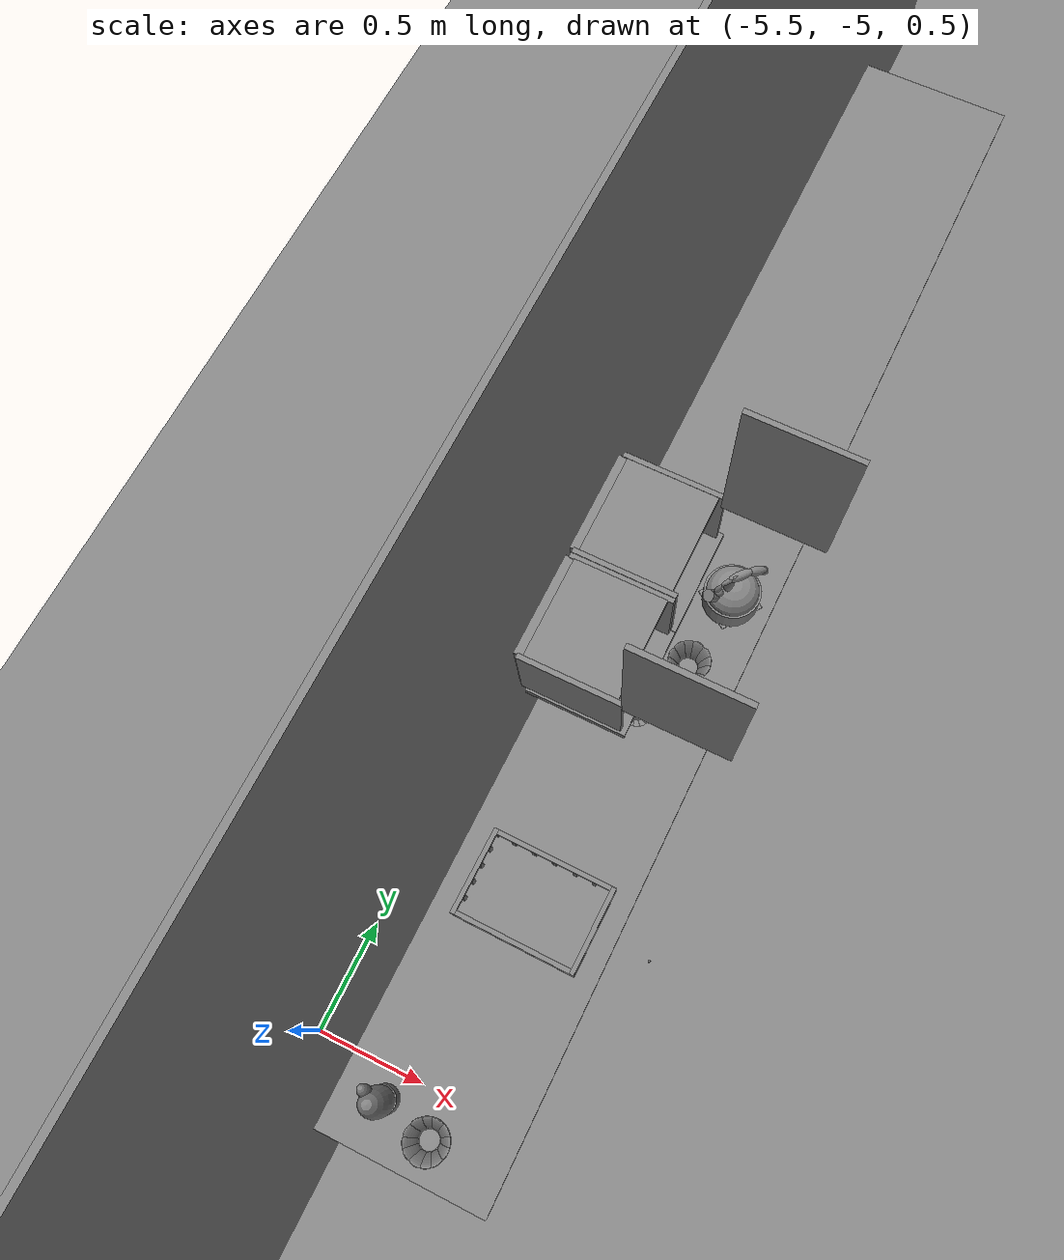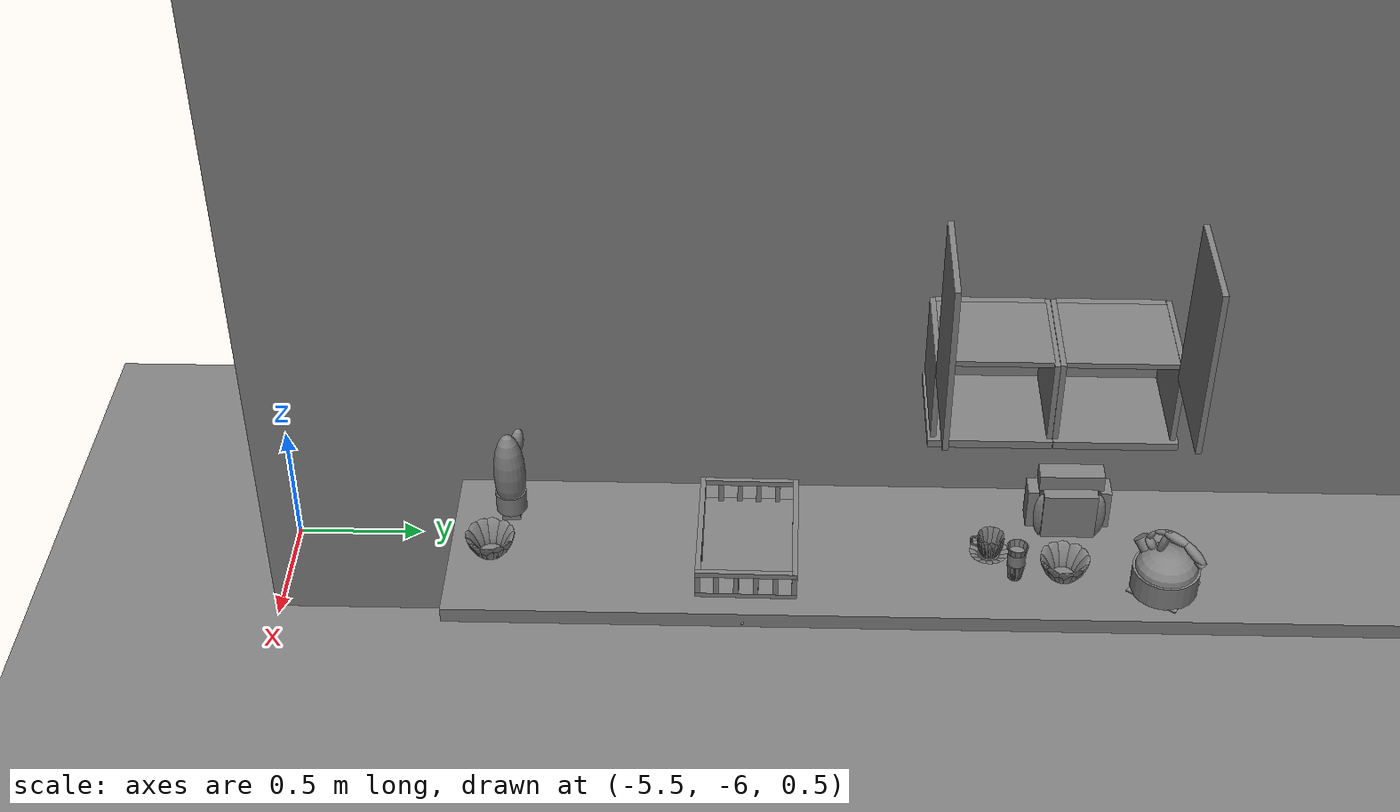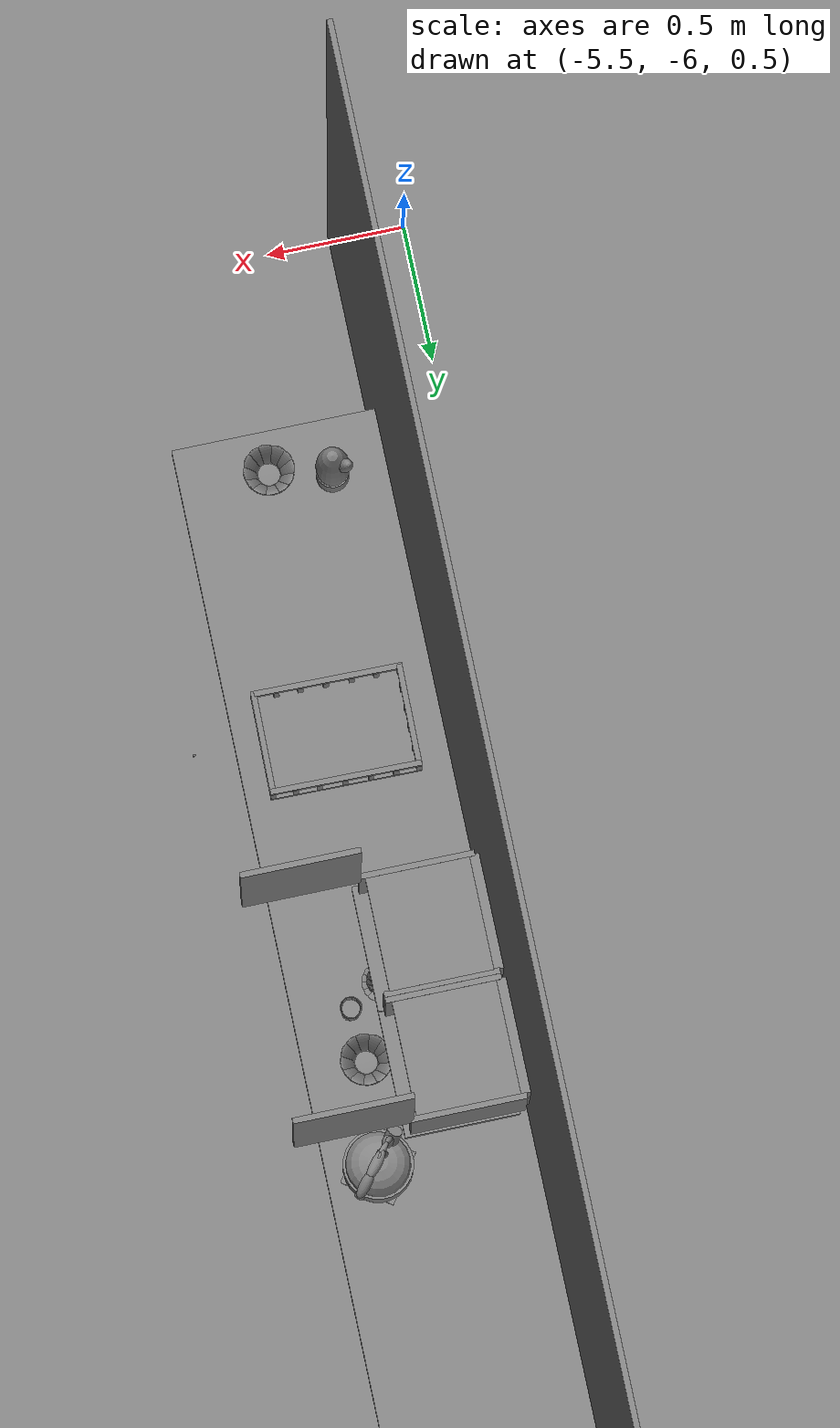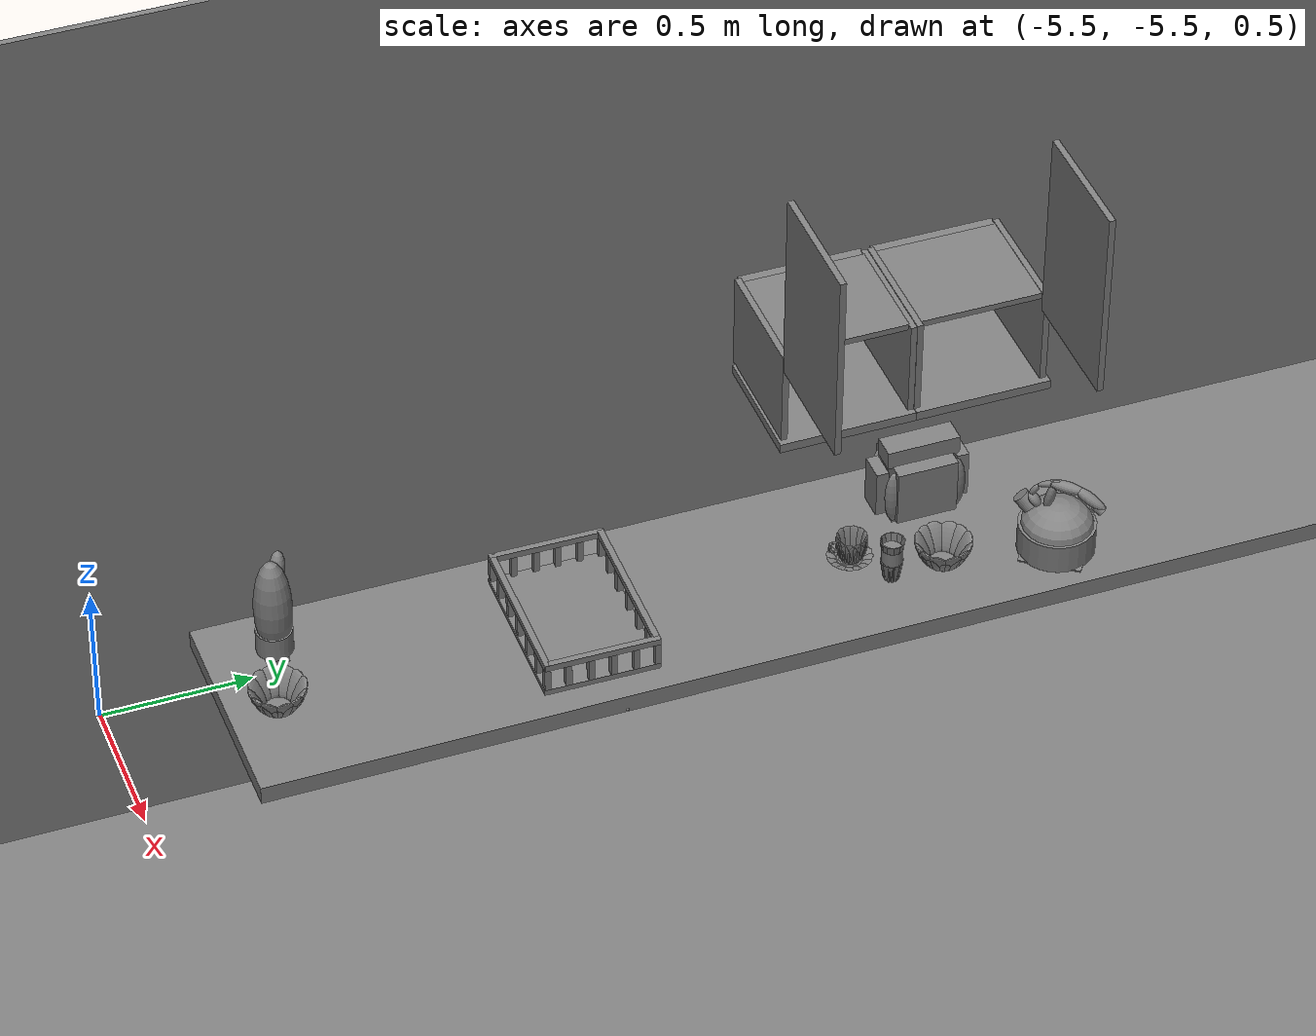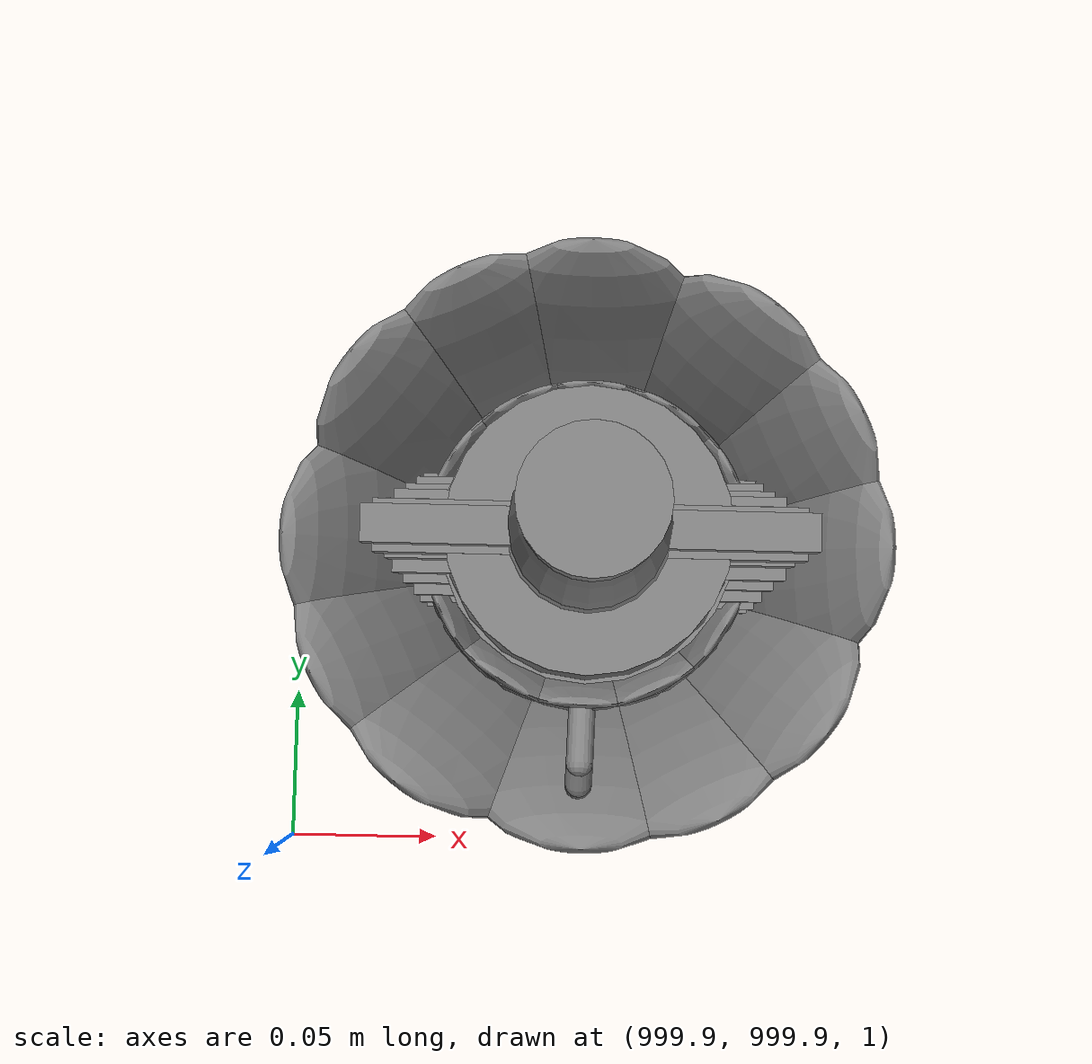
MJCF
<mujoco>
    <option gravity="0.000000000 0.000000000 -9.810000420" timestep="0.0049999999" integrator="implicitfast" density="9.8000002" viscosity="1.8000001e-05" noslip_iterations="10" iterations="100" sdf_iterations="50">
        <flag multiccd="disable"/>
    </option>
    <size memory="1000M"/>
    <compiler coordinate="local"/>
    <worldbody>
        <light cutoff="30" pos="0 1 1" dir="0 -1 -2"/>
        <light cutoff="30" pos="0 -1 1" dir="0 1 -2"/>
        <body pos="0.000000000 0.000000000 0.000000000" euler="0.000000000 0.000000000 0.000000000" name="Static Objcets_Static Objcets">
            <geom contype="1" conaffinity="1" density="1000" type="box" material="" rgba="0.500000000 0.500000000 0.500000000 1.000000000" solimp="0.899999976 0.949999988 0.001000000" friction="1.000000000 0.005000000 0.000100000" solref="0.020000000 1.000000000" margin="0" condim="3" group="0" pos="-5.189302921 -3.293644905 1.760152459" quat="0.707107067 0.707106471 0.000000000 0.000000000" size="0.025000000 0.159999996 0.200000003" name="Static Objcets_geom_492E7B73_A5A4_41EA_A350_B6FF0DF5B441"/>
            <geom contype="1" conaffinity="1" density="1000" type="box" material="" rgba="0.500000000 0.500000000 0.500000000 1.000000000" solimp="0.899999976 0.949999988 0.001000000" friction="1.000000000 0.005000000 0.000100000" solref="0.020000000 1.000000000" margin="0" condim="3" group="0" pos="-4.999745846 -3.497932911 1.764780521" quat="0.707107067 0.707106471 0.000000000 0.000000000" size="0.200000003 0.159999996 0.010000000" name="Static Objcets_geom_FF7E9E78_E85A_4033_9D2A_BC2BA56825DE"/>
            <geom contype="1" conaffinity="1" density="1000" type="box" material="" rgba="0.500000000 0.500000000 0.500000000 1.000000000" solimp="0.899999976 0.949999988 0.001000000" friction="1.000000000 0.005000000 0.000100000" solref="0.020000000 1.000000000" margin="0" condim="3" group="0" pos="-4.979488373 -3.297635794 1.591412544" quat="0.707106829 0.707106709 0.000000000 0.000000000" size="0.200000003 0.015000000 0.219999999" name="Static Objcets_geom_1C92BA66_9C51_402C_AB80_1E43A6437015"/>
            <geom contype="1" conaffinity="1" density="1000" type="box" material="" rgba="0.500000000 0.500000000 0.500000000 1.000000000" solimp="0.899999976 0.949999988 0.001000000" friction="1.000000000 0.005000000 0.000100000" solref="0.020000000 1.000000000" margin="0" condim="3" group="0" pos="-4.999745846 -3.087441683 1.763863802" quat="0.707107067 0.707106471 0.000000000 0.000000000" size="0.200000003 0.159999996 0.010000000" name="Static Objcets_geom_7E6DC43F_D628_4079_BEB0_DAF4D402193D"/>
            <geom contype="1" conaffinity="1" density="1000" type="box" material="" rgba="0.500000000 0.500000000 0.500000000 1.000000000" solimp="0.899999976 0.949999988 0.001000000" friction="1.000000000 0.005000000 0.000100000" solref="0.020000000 1.000000000" margin="0" condim="3" group="0" pos="-5.000125408 -3.294431210 1.913951039" quat="0.707107067 0.707106471 0.000000000 0.000000000" size="0.180000007 0.010000000 0.200000003" name="Static Objcets_geom_F086CBAB_ED8A_4F55_8F3B_BBF5DD0C12E5"/>
            <geom contype="1" conaffinity="1" density="1000" type="box" material="" rgba="0.500000000 0.500000000 0.500000000 1.000000000" solimp="0.899999976 0.949999988 0.001000000" friction="1.000000000 0.005000000 0.000100000" solref="0.020000000 1.000000000" margin="0" condim="3" group="0" pos="-4.873187065 -2.461376429 0.977675021" quat="0.707107067 0.707106471 0.000000000 0.000000000" size="0.370000005 0.029999999 2.799999952" name="Static Objcets_geom_DC64105D_ADD8_49E2_859F_745B1A24E903"/>
            <geom contype="1" conaffinity="1" density="1000" type="box" material="" rgba="0.500000000 0.500000000 0.500000000 1.000000000" solimp="0.899999976 0.949999988 0.001000000" friction="1.000000000 0.005000000 0.000100000" solref="0.020000000 1.000000000" margin="0" condim="3" group="0" pos="-5.244853973 -2.375543594 1.820221663" quat="0.707107008 0.707106531 0.000000000 0.000000000" size="0.010000000 1.500000000 3.700000048" name="Static Objcets_geom_E298699E_FC5E_4BD3_A8CC_0A4813658F14"/>
            <geom contype="1" conaffinity="1" density="1000" type="box" material="" rgba="0.500000000 0.500000000 0.500000000 1.000000000" solimp="0.899999976 0.949999988 0.001000000" friction="1.000000000 0.005000000 0.000100000" solref="0.020000000 1.000000000" margin="0" condim="3" group="0" pos="-0.720102787 0.222944975 -1.102830648" quat="0.000000954 1.000000000 0.000000000 0.000000000" size="8.000000000 8.000000000 0.010000000" name="Static Objcets_geom_0075545C_5D7E_4470_AD5D_A55F8EFA1628"/>
            <geom contype="1" conaffinity="1" density="1000" type="box" material="" rgba="0.500000000 0.500000000 0.500000000 1.000000000" solimp="0.899999976 0.949999988 0.001000000" friction="1.000000000 0.005000000 0.000100000" solref="0.020000000 1.000000000" margin="0" condim="3" group="0" pos="-4.999745846 -2.653569937 1.764779806" quat="0.707107067 0.707106471 0.000000000 0.000000000" size="0.200000003 0.159999996 0.010000000" name="Static Objcets_geom_66D8CC17_4CC1_40DA_9096_0384D0C8DBAB"/>
            <geom contype="1" conaffinity="1" density="1000" type="box" material="" rgba="0.500000000 0.500000000 0.500000000 1.000000000" solimp="0.899999976 0.949999988 0.001000000" friction="1.000000000 0.005000000 0.000100000" solref="0.020000000 1.000000000" margin="0" condim="3" group="0" pos="-5.000125408 -2.861802340 1.913950682" quat="0.707107067 0.707106471 0.000000000 0.000000000" size="0.180000007 0.010000000 0.200000003" name="Static Objcets_geom_A1F0CD48_73E7_4739_A5F6_0AFC8024B1E8"/>
            <geom contype="1" conaffinity="1" density="1000" type="box" material="" rgba="0.500000000 0.500000000 0.500000000 1.000000000" solimp="0.899999976 0.949999988 0.001000000" friction="1.000000000 0.005000000 0.000100000" solref="0.020000000 1.000000000" margin="0" condim="3" group="0" pos="-5.189302921 -2.861564636 1.760152102" quat="0.707107067 0.707106471 0.000000000 0.000000000" size="0.025000000 0.159999996 0.200000003" name="Static Objcets_geom_9BBC6CE6_CDEB_4A98_85BB_0A06EFE11B55"/>
            <geom contype="1" conaffinity="1" density="1000" type="box" material="" rgba="0.500000000 0.500000000 0.500000000 1.000000000" solimp="0.899999976 0.949999988 0.001000000" friction="1.000000000 0.005000000 0.000100000" solref="0.020000000 1.000000000" margin="0" condim="3" group="0" pos="-4.979488373 -2.855390549 1.591412187" quat="0.707106709 0.707106769 0.000000000 0.000000000" size="0.200000003 0.015000000 0.219999999" name="Static Objcets_geom_C8BAA6B5_67FF_4634_B98C_DFAFFFF7B38E"/>
            <geom contype="1" conaffinity="1" density="1000" type="box" material="" rgba="0.500000000 0.500000000 0.500000000 1.000000000" solimp="0.899999976 0.949999988 0.001000000" friction="1.000000000 0.005000000 0.000100000" solref="0.020000000 1.000000000" margin="0" condim="3" group="0" pos="-4.999745846 -3.066934109 1.765979409" quat="0.707107067 0.707106471 0.000000000 0.000000000" size="0.200000003 0.159999996 0.010000000" name="Static Objcets_geom_4AD555F1_34E4_4E4B_B8FB_3973FD9E31D7"/>
        </body>
        <body pos="1000.000000000 1000.000000000 1.000000000" euler="0.000000000 0.000000000 0.000000000" name="openloong_gripper_2f85_fix_base_usda_bottle_red">
            <geom contype="1" conaffinity="1" density="1000" type="ellipsoid" material="" rgba="0.500000000 0.500000000 0.500000000 1.000000000" solimp="0.899999976 0.949999988 0.001000000" friction="1.000000000 0.005000000 0.000100000" solref="0.020000000 1.000000000" margin="0" condim="3" group="0" pos="0.000000000 0.000000000 0.144284487" quat="1.000000000 0.000000000 0.000000000 0.000000000" size="0.021000000 0.021000000 0.079999998" name="openloong_gripper_2f85_fix_base_usda_geom_9F9A2497_19F1_4AF5_843F_571E354D7D24"/>
            <geom contype="1" conaffinity="1" density="1000" type="cylinder" material="" rgba="0.500000000 0.500000000 0.500000000 1.000000000" solimp="0.899999976 0.949999988 0.001000000" friction="1.000000000 0.005000000 0.000100000" solref="0.020000000 1.000000000" margin="0" condim="3" group="0" pos="0.000000000 0.000000000 0.220618963" quat="1.000000000 0.000000000 0.000000000 0.000000000" size="0.016000001 0.010000000 1.000000000" name="openloong_gripper_2f85_fix_base_usda_geom_26A40360_60F6_41A8_9F18_BABB14DB9900"/>
            <geom contype="1" conaffinity="1" density="1000" type="ellipsoid" material="" rgba="0.500000000 0.500000000 0.500000000 1.000000000" solimp="0.899999976 0.949999988 0.001000000" friction="1.000000000 0.005000000 0.000100000" solref="0.020000000 1.000000000" margin="0" condim="3" group="0" pos="0.000000000 0.000000000 0.118945479" quat="1.000000000 0.000000000 0.000000000 0.000000000" size="0.030999999 0.030999999 0.029999999" name="openloong_gripper_2f85_fix_base_usda_geom_EEA3242A_4D60_4446_A1D4_0EFC34CBDBEA"/>
            <geom contype="1" conaffinity="1" density="1000" type="box" material="" rgba="0.500000000 0.500000000 0.500000000 1.000000000" solimp="0.899999976 0.949999988 0.001000000" friction="1.000000000 0.005000000 0.000100000" solref="0.020000000 1.000000000" margin="0" condim="3" group="0" pos="0.000000000 0.000000000 0.002189159" quat="1.000000000 0.000000000 0.000000000 0.000000000" size="0.020000000 0.020000000 0.003000000" name="openloong_gripper_2f85_fix_base_usda_geom_07E5211F_7D98_40DC_9C25_457D079812E9"/>
            <geom contype="1" conaffinity="1" density="1000" type="cylinder" material="" rgba="0.500000000 0.500000000 0.500000000 1.000000000" solimp="0.899999976 0.949999988 0.001000000" friction="1.000000000 0.005000000 0.000100000" solref="0.020000000 1.000000000" margin="0" condim="3" group="0" pos="0.000000000 -0.000366211 0.060884237" quat="1.000000000 0.000000000 0.000000000 0.000000000" size="0.030999999 0.057999998 1.000000000" name="openloong_gripper_2f85_fix_base_usda_geom_98973D47_5AD2_4560_9D79_94F3B79E921B"/>
            <freejoint name="openloong_gripper_2f85_fix_base_usda_bottle_red_joint"/>
            <site size="0.005000000 0.005000000 0.005000000" rgba="0.500000000 0.500000000 0.500000000 1.000000000" pos="0.000000000 0.000000000 0.000000000" quat="0.999961913 0.008726535 0.000000000 0.000000000" group="0" type="sphere" name="openloong_gripper_2f85_fix_base_usda_bottle_redsite"/>
        </body>
        <body pos="-4.138654232 -3.945605040 1.833624721" euler="10.716783524 68.956504822 174.066207886" mocap="true" name="spotlight2_SpotLight"/>
        <body pos="1000.000000000 1000.000000000 1.000000000" euler="0.000000000 0.000000000 0.000000000" name="openloong_gripper_2f85_fix_base_usda_jar_01">
            <geom contype="1" conaffinity="1" density="1000" type="box" material="" rgba="0.500000000 0.500000000 0.500000000 1.000000000" solimp="0.899999976 0.949999988 0.001000000" friction="1.000000000 0.005000000 0.000100000" solref="0.020000000 1.000000000" margin="0" condim="3" group="0" pos="0.000000000 0.000000000 0.006158113" quat="1.000000000 0.000000000 0.000000000 0.000000000" size="0.020000000 0.020000000 0.005000000" name="openloong_gripper_2f85_fix_base_usda_geom_E6A07285_4686_4CF1_9775_3F4692EB5E0D"/>
            <geom contype="1" conaffinity="1" density="1000" type="cylinder" material="" rgba="0.500000000 0.500000000 0.500000000 1.000000000" solimp="0.899999976 0.949999988 0.001000000" friction="1.000000000 0.005000000 0.000100000" solref="0.020000000 1.000000000" margin="0" condim="3" group="0" pos="0.000000000 0.000000000 0.062744498" quat="1.000000000 0.000000000 0.000000000 0.000000000" size="0.041000001 0.052999999 1.000000000" name="openloong_gripper_2f85_fix_base_usda_geom_80C990E2_48E1_401D_9AAD_24E0DA671D5C"/>
            <geom contype="1" conaffinity="1" density="1000" type="ellipsoid" material="" rgba="0.500000000 0.500000000 0.500000000 1.000000000" solimp="0.899999976 0.949999988 0.001000000" friction="1.000000000 0.005000000 0.000100000" solref="0.020000000 1.000000000" margin="0" condim="3" group="0" pos="0.000000000 0.000000000 0.122252703" quat="1.000000000 0.000000000 0.000000000 0.000000000" size="0.035999998 0.035999998 0.010000000" name="openloong_gripper_2f85_fix_base_usda_geom_D1DB0655_1064_431A_91EF_3C42C2FA0C1E"/>
            <geom contype="1" conaffinity="1" density="1000" type="cylinder" material="" rgba="0.500000000 0.500000000 0.500000000 1.000000000" solimp="0.899999976 0.949999988 0.001000000" friction="1.000000000 0.005000000 0.000100000" solref="0.020000000 1.000000000" margin="0" condim="3" group="0" pos="0.000000000 0.000000000 0.015747190" quat="1.000000000 0.000000000 0.000000000 0.000000000" size="0.035000000 0.010000000 1.000000000" name="openloong_gripper_2f85_fix_base_usda_geom_5A96767B_E63D_49CC_AE9C_345F796264DF"/>
            <geom contype="1" conaffinity="1" density="1000" type="ellipsoid" material="" rgba="0.500000000 0.500000000 0.500000000 1.000000000" solimp="0.899999976 0.949999988 0.001000000" friction="1.000000000 0.005000000 0.000100000" solref="0.020000000 1.000000000" margin="0" condim="3" group="0" pos="0.000000000 0.000000000 0.115815401" quat="1.000000000 0.000000000 0.000000000 0.000000000" size="0.039999999 0.039999999 0.010000000" name="openloong_gripper_2f85_fix_base_usda_geom_A56F2467_D5AB_4734_BE18_7D69E998441E"/>
            <geom contype="1" conaffinity="1" density="1000" type="cylinder" material="" rgba="0.500000000 0.500000000 0.500000000 1.000000000" solimp="0.899999976 0.949999988 0.001000000" friction="1.000000000 0.005000000 0.000100000" solref="0.020000000 1.000000000" margin="0" condim="3" group="0" pos="0.000000000 0.000000000 0.133183479" quat="1.000000000 0.000000000 0.000000000 0.000000000" size="0.037999999 0.006500000 1.000000000" name="openloong_gripper_2f85_fix_base_usda_geom_FE2D53D2_EABD_4BD8_855E_DD7C53534589"/>
            <freejoint name="openloong_gripper_2f85_fix_base_usda_jar_01_joint"/>
            <site size="0.005000000 0.005000000 0.005000000" rgba="0.500000000 0.500000000 0.500000000 1.000000000" pos="0.000000000 0.000000000 0.000000000" quat="1.000000000 0.000000000 0.000000000 0.000000000" group="0" type="sphere" name="openloong_gripper_2f85_fix_base_usda_jar_01site"/>
        </body>
        <body pos="1000.000000000 1000.000000000 1.000000000" euler="0.000000000 0.000000000 0.000000000" name="openloong_gripper_2f85_fix_base_usda_bow_yellow_kps">
            <geom contype="1" conaffinity="1" density="1000" type="ellipsoid" material="" rgba="0.500000000 0.500000000 0.500000000 1.000000000" solimp="0.899999976 0.949999988 0.001000000" friction="1.000000000 0.005000000 0.000100000" solref="0.020000000 1.000000000" margin="0" condim="3" group="0" pos="-0.052185059 0.040283203 0.044118762" quat="0.919264615 -0.076883033 -0.225593656 -0.313287765" size="0.010000000 0.039999999 0.052000001" name="openloong_gripper_2f85_fix_base_usda_geom_1E3B0B2B_0A6D_42D8_9FDF_D1E66087778D"/>
            <geom contype="1" conaffinity="1" density="1000" type="ellipsoid" material="" rgba="0.500000000 0.500000000 0.500000000 1.000000000" solimp="0.899999976 0.949999988 0.001000000" friction="1.000000000 0.005000000 0.000100000" solref="0.020000000 1.000000000" margin="0" condim="3" group="0" pos="-0.000061035 0.065979004 0.044118762" quat="0.687598765 -0.168314874 -0.168741167 -0.685860336" size="0.010000000 0.039999999 0.052000001" name="openloong_gripper_2f85_fix_base_usda_geom_CF689F4E_135D_4A38_A2C8_8A055EEDE15B"/>
            <geom contype="1" conaffinity="1" density="1000" type="box" material="" rgba="0.500000000 0.500000000 0.500000000 1.000000000" solimp="0.899999976 0.949999988 0.001000000" friction="1.000000000 0.005000000 0.000100000" solref="0.020000000 1.000000000" margin="0" condim="3" group="0" pos="0.000061035 0.000000000 -0.002001643" quat="1.000000000 0.000000000 0.000000000 0.000000000" size="0.029999999 0.029999999 0.002000000" name="openloong_gripper_2f85_fix_base_usda_geom_4B5B1C47_56AF_491B_A3A5_97B85F331F33"/>
            <geom contype="1" conaffinity="1" density="1000" type="ellipsoid" material="" rgba="0.500000000 0.500000000 0.500000000 1.000000000" solimp="0.899999976 0.949999988 0.001000000" friction="1.000000000 0.005000000 0.000100000" solref="0.020000000 1.000000000" margin="0" condim="3" group="0" pos="0.029418945 -0.059082031 0.044118762" quat="0.825555861 0.125530601 0.202597082 -0.511521280" size="0.010000000 0.039999999 0.052000001" name="openloong_gripper_2f85_fix_base_usda_geom_ADE76A6C_9216_423E_8D90_DB9D835137D1"/>
            <geom contype="1" conaffinity="1" density="1000" type="ellipsoid" material="" rgba="0.500000000 0.500000000 0.500000000 1.000000000" solimp="0.899999976 0.949999988 0.001000000" friction="1.000000000 0.005000000 0.000100000" solref="0.020000000 1.000000000" margin="0" condim="3" group="0" pos="0.000244141 -0.065979004 0.044118762" quat="0.687598765 0.168314651 0.168741375 -0.685860336" size="0.010000000 0.039999999 0.052000001" name="openloong_gripper_2f85_fix_base_usda_geom_924CD726_C8CA_4E4C_8418_82D4159DE537"/>
            <geom contype="1" conaffinity="1" density="1000" type="ellipsoid" material="" rgba="0.500000000 0.500000000 0.500000000 1.000000000" solimp="0.899999976 0.949999988 0.001000000" friction="1.000000000 0.005000000 0.000100000" solref="0.020000000 1.000000000" margin="0" condim="3" group="0" pos="0.000061035 0.000000000 0.000446677" quat="1.000000000 0.000000000 0.000000000 0.000000000" size="0.039999999 0.039999999 0.002000000" name="openloong_gripper_2f85_fix_base_usda_geom_F57EB8E7_3F2D_4665_B543_54AC5948B9C9"/>
            <geom contype="1" conaffinity="1" density="1000" type="ellipsoid" material="" rgba="0.500000000 0.500000000 0.500000000 1.000000000" solimp="0.899999976 0.949999988 0.001000000" friction="1.000000000 0.005000000 0.000100000" solref="0.020000000 1.000000000" margin="0" condim="3" group="0" pos="0.059082031 0.029541016 0.044118762" quat="0.223252773 -0.231952220 -0.054787423 -0.945174456" size="0.010000000 0.039999999 0.052000001" name="openloong_gripper_2f85_fix_base_usda_geom_00C4B524_F6FF_4D45_B629_1AE65C985790"/>
            <geom contype="1" conaffinity="1" density="1000" type="ellipsoid" material="" rgba="0.500000000 0.500000000 0.500000000 1.000000000" solimp="0.899999976 0.949999988 0.001000000" friction="1.000000000 0.005000000 0.000100000" solref="0.020000000 1.000000000" margin="0" condim="3" group="0" pos="0.000061035 0.000000000 0.007335305" quat="1.000000000 0.000000000 0.000000000 0.000000000" size="0.039999999 0.039999999 0.002000000" name="openloong_gripper_2f85_fix_base_usda_geom_21190352_A1F0_40CF_B026_2AEBB7BB2E13"/>
            <geom contype="1" conaffinity="1" density="1000" type="ellipsoid" material="" rgba="0.500000000 0.500000000 0.500000000 1.000000000" solimp="0.899999976 0.949999988 0.001000000" friction="1.000000000 0.005000000 0.000100000" solref="0.020000000 1.000000000" margin="0" condim="3" group="0" pos="-0.029296875 0.059082031 0.044118762" quat="0.825555861 -0.125530809 -0.202596918 -0.511521280" size="0.010000000 0.039999999 0.052000001" name="openloong_gripper_2f85_fix_base_usda_geom_216A8443_BA81_41AE_A000_6AEAF5A05635"/>
            <geom contype="1" conaffinity="1" density="1000" type="ellipsoid" material="" rgba="0.500000000 0.500000000 0.500000000 1.000000000" solimp="0.899999976 0.949999988 0.001000000" friction="1.000000000 0.005000000 0.000100000" solref="0.020000000 1.000000000" margin="0" condim="3" group="0" pos="0.040222168 0.052368164 0.044118762" quat="0.429593176 -0.213750049 -0.105424821 -0.871002972" size="0.010000000 0.039999999 0.052000001" name="openloong_gripper_2f85_fix_base_usda_geom_745711D8_42D2_4D6C_8F14_E3DBFDC3FD34"/>
            <geom contype="1" conaffinity="1" density="1000" type="ellipsoid" material="" rgba="0.500000000 0.500000000 0.500000000 1.000000000" solimp="0.899999976 0.949999988 0.001000000" friction="1.000000000 0.005000000 0.000100000" solref="0.020000000 1.000000000" margin="0" condim="3" group="0" pos="0.066040039 0.000000000 0.044118762" quat="0.971183062 -0.000000156 0.238334835 0.000000030" size="0.010000000 0.039999999 0.052000001" name="openloong_gripper_2f85_fix_base_usda_geom_BE1E609A_9014_4924_AD59_B30B675EC51C"/>
            <geom contype="1" conaffinity="1" density="1000" type="ellipsoid" material="" rgba="0.500000000 0.500000000 0.500000000 1.000000000" solimp="0.899999976 0.949999988 0.001000000" friction="1.000000000 0.005000000 0.000100000" solref="0.020000000 1.000000000" margin="0" condim="3" group="0" pos="0.052307129 -0.040283203 0.044118762" quat="0.919264674 0.076882750 0.225593731 -0.313287705" size="0.010000000 0.039999999 0.052000001" name="openloong_gripper_2f85_fix_base_usda_geom_8BA96F58_101E_44CD_80C6_BA6C12D2C7FB"/>
            <geom contype="1" conaffinity="1" density="1000" type="ellipsoid" material="" rgba="0.500000000 0.500000000 0.500000000 1.000000000" solimp="0.899999976 0.949999988 0.001000000" friction="1.000000000 0.005000000 0.000100000" solref="0.020000000 1.000000000" margin="0" condim="3" group="0" pos="-0.065917969 0.000000000 0.044118762" quat="0.971183062 -0.000000142 -0.238334835 0.000000030" size="0.010000000 0.039999999 0.052000001" name="openloong_gripper_2f85_fix_base_usda_geom_786400F9_BFCC_495A_B9B4_0524F49F9D47"/>
            <geom contype="1" conaffinity="1" density="1000" type="ellipsoid" material="" rgba="0.500000000 0.500000000 0.500000000 1.000000000" solimp="0.899999976 0.949999988 0.001000000" friction="1.000000000 0.005000000 0.000100000" solref="0.020000000 1.000000000" margin="0" condim="3" group="0" pos="-0.058898926 -0.029541016 0.044118762" quat="0.223252758 0.231952101 0.054787733 -0.945174575" size="0.010000000 0.039999999 0.052000001" name="openloong_gripper_2f85_fix_base_usda_geom_53BC14E6_5F97_41F0_9245_B6764F8867BC"/>
            <geom contype="1" conaffinity="1" density="1000" type="ellipsoid" material="" rgba="0.500000000 0.500000000 0.500000000 1.000000000" solimp="0.899999976 0.949999988 0.001000000" friction="1.000000000 0.005000000 0.000100000" solref="0.020000000 1.000000000" margin="0" condim="3" group="0" pos="-0.040100098 -0.052368164 0.044118762" quat="0.429593235 0.213749886 0.105425082 -0.871003032" size="0.010000000 0.039999999 0.052000001" name="openloong_gripper_2f85_fix_base_usda_geom_F5038F8C_924D_4FAF_AB06_F706A02A17C9"/>
            <freejoint name="openloong_gripper_2f85_fix_base_usda_bow_yellow_kps_joint"/>
            <site size="0.005000000 0.005000000 0.005000000" rgba="0.500000000 0.500000000 0.500000000 1.000000000" pos="0.000000000 0.000000000 0.000000000" quat="0.999961913 0.008726534 0.000000000 0.000000000" group="0" type="sphere" name="openloong_gripper_2f85_fix_base_usda_bow_yellow_kps"/>
        </body>
        <body pos="-4.084612370 -4.607702255 1.899169445" euler="-123.298461914 -78.298408508 170.696456909" mocap="true" name="spotlight6_SpotLight"/>
        <body pos="-4.235116482 -4.370840549 1.758718014" euler="-12.556044579 -66.891372681 38.512554169" mocap="true" name="spotlight1_SpotLight"/>
        <body pos="1000.000000000 1000.000000000 1.000000000" euler="0.000000000 0.000000000 0.000000000" name="openloong_gripper_2f85_fix_base_usda_salt">
            <geom contype="1" conaffinity="1" density="1000" type="box" material="" rgba="0.500000000 0.500000000 0.500000000 1.000000000" solimp="0.899999976 0.949999988 0.001000000" friction="1.000000000 0.005000000 0.000100000" solref="0.020000000 1.000000000" margin="0" condim="3" group="0" pos="0.000305176 0.000000000 0.084862232" quat="1.000000000 0.000000000 0.000000000 0.000000000" size="0.048999999 0.018999999 0.005000000" name="openloong_gripper_2f85_fix_base_usda_geom_A74B94E9_BDC1_4AB4_9661_113891E87286"/>
            <geom contype="1" conaffinity="1" density="1000" type="box" material="" rgba="0.500000000 0.500000000 0.500000000 1.000000000" solimp="0.899999976 0.949999988 0.001000000" friction="1.000000000 0.005000000 0.000100000" solref="0.020000000 1.000000000" margin="0" condim="3" group="0" pos="0.000305176 0.000000000 0.104564309" quat="1.000000000 0.000000000 0.000000000 0.000000000" size="0.052000001 0.014000000 0.005000000" name="openloong_gripper_2f85_fix_base_usda_geom_8DC8FCF3_3D92_40D8_9F71_4AD01A43DB1A"/>
            <geom contype="1" conaffinity="1" density="1000" type="box" material="" rgba="0.500000000 0.500000000 0.500000000 1.000000000" solimp="0.899999976 0.949999988 0.001000000" friction="1.000000000 0.005000000 0.000100000" solref="0.020000000 1.000000000" margin="0" condim="3" group="0" pos="0.000305176 0.000000000 0.114487171" quat="1.000000000 0.000000000 0.000000000 0.000000000" size="0.054000001 0.011500000 0.005000000" name="openloong_gripper_2f85_fix_base_usda_geom_11B098EE_C988_41CD_AD93_993129013854"/>
            <geom contype="1" conaffinity="1" density="1000" type="box" material="" rgba="0.500000000 0.500000000 0.500000000 1.000000000" solimp="0.899999976 0.949999988 0.001000000" friction="1.000000000 0.005000000 0.000100000" solref="0.020000000 1.000000000" margin="0" condim="3" group="0" pos="0.000305176 0.000000000 0.075103164" quat="1.000000000 0.000000000 0.000000000 0.000000000" size="0.048000000 0.020000000 0.005000000" name="openloong_gripper_2f85_fix_base_usda_geom_950FE8D4_92C3_4E2A_9517_30E47EDAD0F6"/>
            <geom contype="1" conaffinity="1" density="1000" type="box" material="" rgba="0.500000000 0.500000000 0.500000000 1.000000000" solimp="0.899999976 0.949999988 0.001000000" friction="1.000000000 0.005000000 0.000100000" solref="0.020000000 1.000000000" margin="0" condim="3" group="0" pos="0.000305176 0.000000000 0.134892464" quat="1.000000000 0.000000000 0.000000000 0.000000000" size="0.057000000 0.007000000 0.005000000" name="openloong_gripper_2f85_fix_base_usda_geom_FB31325C_7BDB_4D51_94B1_EF4A3DD89EFB"/>
            <geom contype="1" conaffinity="1" density="1000" type="box" material="" rgba="0.500000000 0.500000000 0.500000000 1.000000000" solimp="0.899999976 0.949999988 0.001000000" friction="1.000000000 0.005000000 0.000100000" solref="0.020000000 1.000000000" margin="0" condim="3" group="0" pos="0.000305176 0.000000000 0.094920278" quat="1.000000000 0.000000000 0.000000000 0.000000000" size="0.050000001 0.017000001 0.005000000" name="openloong_gripper_2f85_fix_base_usda_geom_DE92938D_81EA_41FF_AABE_CA75B587F93F"/>
            <geom contype="1" conaffinity="1" density="1000" type="box" material="" rgba="0.500000000 0.500000000 0.500000000 1.000000000" solimp="0.899999976 0.949999988 0.001000000" friction="1.000000000 0.005000000 0.000100000" solref="0.020000000 1.000000000" margin="0" condim="3" group="0" pos="0.000305176 0.000000000 0.065204859" quat="1.000000000 0.000000000 0.000000000 0.000000000" size="0.045000002 0.021000000 0.005000000" name="openloong_gripper_2f85_fix_base_usda_geom_2630CB02_86BE_4CAD_BED3_9BE13E9F301D"/>
            <geom contype="1" conaffinity="1" density="1000" type="box" material="" rgba="0.500000000 0.500000000 0.500000000 1.000000000" solimp="0.899999976 0.949999988 0.001000000" friction="1.000000000 0.005000000 0.000100000" solref="0.020000000 1.000000000" margin="0" condim="3" group="0" pos="0.000305176 0.000000000 0.144135714" quat="1.000000000 0.000000000 0.000000000 0.000000000" size="0.059000000 0.005000000 0.004000000" name="openloong_gripper_2f85_fix_base_usda_geom_D6EFF77E_81F2_4FAD_8F88_5F9F3BBE8985"/>
            <geom contype="1" conaffinity="1" density="1000" type="box" material="" rgba="0.500000000 0.500000000 0.500000000 1.000000000" solimp="0.899999976 0.949999988 0.001000000" friction="1.000000000 0.005000000 0.000100000" solref="0.020000000 1.000000000" margin="0" condim="3" group="0" pos="0.000000000 0.000000000 0.031593561" quat="1.000000000 0.000000000 0.000000000 0.000000000" size="0.041999999 0.024000000 0.029999999" name="openloong_gripper_2f85_fix_base_usda_geom_AAA57054_FE9B_496E_BDCE_86FD7006C15F"/>
            <geom contype="1" conaffinity="1" density="1000" type="box" material="" rgba="0.500000000 0.500000000 0.500000000 1.000000000" solimp="0.899999976 0.949999988 0.001000000" friction="1.000000000 0.005000000 0.000100000" solref="0.020000000 1.000000000" margin="0" condim="3" group="0" pos="0.000305176 0.000000000 0.124608755" quat="1.000000000 0.000000000 0.000000000 0.000000000" size="0.055000000 0.008000000 0.005000000" name="openloong_gripper_2f85_fix_base_usda_geom_91B3F9F6_9AE4_45EF_80E2_4AD4E1920BB8"/>
            <freejoint name="openloong_gripper_2f85_fix_base_usda_salt_joint"/>
            <site size="0.005000000 0.005000000 0.005000000" rgba="0.500000000 0.500000000 0.500000000 1.000000000" pos="0.000000000 0.000000000 0.000000000" quat="1.000000000 0.000000000 0.000000000 0.000000000" group="0" type="sphere" name="openloong_gripper_2f85_fix_base_usda_saltsite"/>
        </body>
        <body pos="1000.000000000 1000.000000000 1.000000000" euler="0.000000000 0.000000000 0.000000000" name="openloong_gripper_2f85_fix_base_usda_coffeecup_white_kps">
            <geom contype="1" conaffinity="1" density="1000" type="capsule" material="" rgba="0.500000000 0.500000000 0.500000000 1.000000000" solimp="0.899999976 0.949999988 0.001000000" friction="1.000000000 0.005000000 0.000100000" solref="0.020000000 1.000000000" margin="0" condim="3" group="0" pos="-0.000854492 -0.065795898 0.050029993" quat="0.343559504 -0.613204718 0.626912475 0.336047262" size="0.004000000 0.005000000 1.000000000" name="openloong_gripper_2f85_fix_base_usda_geom_13282922_09E4_4E9A_9B07_4389A1B3D11C"/>
            <geom contype="1" conaffinity="1" density="1000" type="ellipsoid" material="" rgba="0.500000000 0.500000000 0.500000000 1.000000000" solimp="0.899999976 0.949999988 0.001000000" friction="1.000000000 0.005000000 0.000100000" solref="0.020000000 1.000000000" margin="0" condim="3" group="0" pos="-0.000793457 -0.038452148 0.048040152" quat="0.711656272 0.066323131 -0.067805752 0.696095467" size="0.005000000 0.029999999 0.048999999" name="openloong_gripper_2f85_fix_base_usda_geom_1A841AE4_970D_47D0_8671_F23A133EFC1C"/>
            <geom contype="1" conaffinity="1" density="1000" type="ellipsoid" material="" rgba="0.500000000 0.500000000 0.500000000 1.000000000" solimp="0.899999976 0.949999988 0.001000000" friction="1.000000000 0.005000000 0.000100000" solref="0.020000000 1.000000000" margin="0" condim="3" group="0" pos="0.037719727 -0.001892090 0.048040152" quat="0.995387912 0.001371633 0.094835162 -0.014391154" size="0.005000000 0.029999999 0.048999999" name="openloong_gripper_2f85_fix_base_usda_geom_807F8B1A_CC38_4C09_94D4_3FB7395F2366"/>
            <geom contype="1" conaffinity="1" density="1000" type="ellipsoid" material="" rgba="0.500000000 0.500000000 0.500000000 1.000000000" solimp="0.899999976 0.949999988 0.001000000" friction="1.000000000 0.005000000 0.000100000" solref="0.020000000 1.000000000" margin="0" condim="3" group="0" pos="0.033996582 0.015502930 0.048040152" quat="0.970659733 -0.021051638 0.092478797 0.220962167" size="0.005000000 0.029999999 0.048999999" name="openloong_gripper_2f85_fix_base_usda_geom_E4968073_9CA9_453C_91C7_3DCDDA8F5BE2"/>
            <geom contype="1" conaffinity="1" density="1000" type="box" material="" rgba="0.500000000 0.500000000 0.500000000 1.000000000" solimp="0.899999976 0.949999988 0.001000000" friction="1.000000000 0.005000000 0.000100000" solref="0.020000000 1.000000000" margin="0" condim="3" group="0" pos="0.000793457 -0.000183105 0.000156164" quat="0.714879215 0.000000000 0.000000000 0.699247897" size="0.020000000 0.020000000 0.002000000" name="openloong_gripper_2f85_fix_base_usda_geom_5F1FEC79_6E2B_4FF0_BD1E_A8265A4AABC7"/>
            <geom contype="1" conaffinity="1" density="1000" type="ellipsoid" material="" rgba="0.500000000 0.500000000 0.500000000 1.000000000" solimp="0.899999976 0.949999988 0.001000000" friction="1.000000000 0.005000000 0.000100000" solref="0.020000000 1.000000000" margin="0" condim="3" group="0" pos="-0.019409180 -0.033081055 0.048040152" quat="0.866879702 0.046630561 -0.082595348 0.489411235" size="0.005000000 0.029999999 0.048999999" name="openloong_gripper_2f85_fix_base_usda_geom_F184DE2C_F81C_4C50_8341_9BE8463185F7"/>
            <geom contype="1" conaffinity="1" density="1000" type="ellipsoid" material="" rgba="0.500000000 0.500000000 0.500000000 1.000000000" solimp="0.899999976 0.949999988 0.001000000" friction="1.000000000 0.005000000 0.000100000" solref="0.020000000 1.000000000" margin="0" condim="3" group="0" pos="-0.016052246 0.033264160 0.048040152" quat="0.840792537 -0.050782297 -0.080109790 -0.532983541" size="0.005000000 0.029999999 0.048999999" name="openloong_gripper_2f85_fix_base_usda_geom_847C4941_3A58_4F90_A211_C8C491BD053C"/>
            <geom contype="1" conaffinity="1" density="1000" type="capsule" material="" rgba="0.500000000 0.500000000 0.500000000 1.000000000" solimp="0.899999976 0.949999988 0.001000000" friction="1.000000000 0.005000000 0.000100000" solref="0.020000000 1.000000000" margin="0" condim="3" group="0" pos="-0.000549316 -0.053527832 0.046825886" quat="0.505496025 -0.494442940 0.505495846 0.494442940" size="0.004000000 0.005000000 1.000000000" name="openloong_gripper_2f85_fix_base_usda_geom_357D97FD_8D13_4740_AB2C_D017A0CE8176"/>
            <geom contype="1" conaffinity="1" density="1000" type="ellipsoid" material="" rgba="0.500000000 0.500000000 0.500000000 1.000000000" solimp="0.899999976 0.949999988 0.001000000" friction="1.000000000 0.005000000 0.000100000" solref="0.020000000 1.000000000" margin="0" condim="3" group="0" pos="-0.032104492 0.018920898 0.048040152" quat="0.958129764 -0.025742561 -0.091288343 -0.270168930" size="0.005000000 0.029999999 0.048999999" name="openloong_gripper_2f85_fix_base_usda_geom_47FDA93E_844E_47CF_9E38_B07E3EBEA6B9"/>
            <geom contype="1" conaffinity="1" density="1000" type="ellipsoid" material="" rgba="0.500000000 0.500000000 0.500000000 1.000000000" solimp="0.899999976 0.949999988 0.001000000" friction="1.000000000 0.005000000 0.000100000" solref="0.020000000 1.000000000" margin="0" condim="3" group="0" pos="-0.037597656 0.000305176 0.048040152" quat="0.995387554 -0.001371440 -0.094839431 -0.014389008" size="0.005000000 0.029999999 0.048999999" name="openloong_gripper_2f85_fix_base_usda_geom_B9DBADBC_6B2C_4C4A_841A_18E842DA47C7"/>
            <geom contype="1" conaffinity="1" density="1000" type="capsule" material="" rgba="0.500000000 0.500000000 0.500000000 1.000000000" solimp="0.899999976 0.949999988 0.001000000" friction="1.000000000 0.005000000 0.000100000" solref="0.020000000 1.000000000" margin="0" condim="3" group="0" pos="-0.000366211 -0.043762207 0.044118762" quat="0.260488123 -0.651174724 0.665731549 0.254792154" size="0.004000000 0.003000000 1.000000000" name="openloong_gripper_2f85_fix_base_usda_geom_207302AA_A2A6_4A30_9E2A_B331A885D4AB"/>
            <geom contype="1" conaffinity="1" density="1000" type="capsule" material="" rgba="0.500000000 0.500000000 0.500000000 1.000000000" solimp="0.899999976 0.949999988 0.001000000" friction="1.000000000 0.005000000 0.000100000" solref="0.020000000 1.000000000" margin="0" condim="3" group="0" pos="-0.000915527 -0.068542480 0.082936406" quat="0.624995589 -0.339446366 0.347034454 0.611329615" size="0.004000000 0.004000000 1.000000000" name="openloong_gripper_2f85_fix_base_usda_geom_6E933CB7_5BE6_48B7_82A7_7EEA7EA9C877"/>
            <geom contype="1" conaffinity="1" density="1000" type="ellipsoid" material="" rgba="0.500000000 0.500000000 0.500000000 1.000000000" solimp="0.899999976 0.949999988 0.001000000" friction="1.000000000 0.005000000 0.000100000" solref="0.020000000 1.000000000" margin="0" condim="3" group="0" pos="0.016113281 -0.034851074 0.048040152" quat="0.840793252 0.050779939 0.080106191 -0.532983422" size="0.005000000 0.029999999 0.048999999" name="openloong_gripper_2f85_fix_base_usda_geom_EBA2C7F8_5830_4452_8E53_0E46299047E4"/>
            <geom contype="1" conaffinity="1" density="1000" type="ellipsoid" material="" rgba="0.500000000 0.500000000 0.500000000 1.000000000" solimp="0.899999976 0.949999988 0.001000000" friction="1.000000000 0.005000000 0.000100000" solref="0.020000000 1.000000000" margin="0" condim="3" group="0" pos="0.000854492 0.036865234 0.048040152" quat="0.711656570 -0.066320375 0.067802906 0.696095705" size="0.005000000 0.029999999 0.048999999" name="openloong_gripper_2f85_fix_base_usda_geom_F41C0B39_936A_4AFE_8601_62C06A91D311"/>
            <geom contype="1" conaffinity="1" density="1000" type="ellipsoid" material="" rgba="0.500000000 0.500000000 0.500000000 1.000000000" solimp="0.899999976 0.949999988 0.001000000" friction="1.000000000 0.005000000 0.000100000" solref="0.020000000 1.000000000" margin="0" condim="3" group="0" pos="-0.033935547 -0.017089844 0.048040152" quat="0.970659137 0.021052625 -0.092483103 0.220962465" size="0.005000000 0.029999999 0.048999999" name="openloong_gripper_2f85_fix_base_usda_geom_8F80A564_2746_4F16_BD8E_F548E79E1F27"/>
            <geom contype="1" conaffinity="1" density="1000" type="ellipsoid" material="" rgba="0.500000000 0.500000000 0.500000000 1.000000000" solimp="0.899999976 0.949999988 0.001000000" friction="1.000000000 0.005000000 0.000100000" solref="0.020000000 1.000000000" margin="0" condim="3" group="0" pos="0.019531250 0.031494141 0.048040152" quat="0.866880119 -0.046628602 0.082591817 0.489411235" size="0.005000000 0.029999999 0.048999999" name="openloong_gripper_2f85_fix_base_usda_geom_48EE9762_718A_4D79_A16A_665878EAACC7"/>
            <geom contype="1" conaffinity="1" density="1000" type="ellipsoid" material="" rgba="0.500000000 0.500000000 0.500000000 1.000000000" solimp="0.899999976 0.949999988 0.001000000" friction="1.000000000 0.005000000 0.000100000" solref="0.020000000 1.000000000" margin="0" condim="3" group="0" pos="0.032165527 -0.020507812 0.048040152" quat="0.958128154 0.025740955 0.091285400 -0.270175666" size="0.005000000 0.029999999 0.048999999" name="openloong_gripper_2f85_fix_base_usda_geom_2FEEFDCA_B212_4CD0_A71D_72457198F268"/>
            <geom contype="1" conaffinity="1" density="1000" type="capsule" material="" rgba="0.500000000 0.500000000 0.500000000 1.000000000" solimp="0.899999976 0.949999988 0.001000000" friction="1.000000000 0.005000000 0.000100000" solref="0.020000000 1.000000000" margin="0" condim="3" group="0" pos="-0.000610352 -0.056823730 0.083572865" quat="0.452654332 -0.541215360 0.553313971 0.442756712" size="0.004000000 0.009000000 1.000000000" name="openloong_gripper_2f85_fix_base_usda_geom_BC226313_41F8_43E4_A38F_F30EB04087B8"/>
            <geom contype="1" conaffinity="1" density="1000" type="ellipsoid" material="" rgba="0.500000000 0.500000000 0.500000000 1.000000000" solimp="0.899999976 0.949999988 0.001000000" friction="1.000000000 0.005000000 0.000100000" solref="0.020000000 1.000000000" margin="0" condim="3" group="0" pos="0.000061035 -0.000183105 0.001848221" quat="0.714879215 0.000000000 0.000000000 0.699247897" size="0.029999999 0.029999999 0.001000000" name="openloong_gripper_2f85_fix_base_usda_geom_219C942A_2660_4E4D_9156_67D9B5B33BF6"/>
            <geom contype="1" conaffinity="1" density="1000" type="capsule" material="" rgba="0.500000000 0.500000000 0.500000000 1.000000000" solimp="0.899999976 0.949999988 0.001000000" friction="1.000000000 0.005000000 0.000100000" solref="0.020000000 1.000000000" margin="0" condim="3" group="0" pos="-0.000976562 -0.071838379 0.066101432" quat="0.031849027 -0.698553741 0.714169443 0.031152546" size="0.004000000 0.012000000 1.000000000" name="openloong_gripper_2f85_fix_base_usda_geom_3F7C3163_9DDF_42B6_BB8A_E4FDBA1FF361"/>
            <freejoint name="openloong_gripper_2f85_fix_base_usda_coffeecup_white_kps_joint"/>
            <site size="0.005000000 0.005000000 0.005000000" rgba="0.500000000 0.500000000 0.500000000 1.000000000" pos="0.000000000 0.000000000 0.000000000" quat="0.999961913 0.008726534 0.000000000 0.000000000" group="0" type="sphere" name="openloong_gripper_2f85_fix_base_usda_coffeecup_white_kps"/>
        </body>
        <body pos="-4.860558510 -4.149443150 1.004824519" euler="0.000000000 0.000000000 -90.691101074" name="openloong_gripper_2f85_fix_base_usda_Basket_Kitchen_01">
            <geom contype="1" conaffinity="1" density="1000" type="box" material="" rgba="0.500000000 0.500000000 0.500000000 1.000000000" solimp="0.899999976 0.949999988 0.001000000" friction="1.000000000 0.005000000 0.000100000" solref="0.020000000 1.000000000" margin="0" condim="3" group="0" pos="-0.175679624 -0.000001907 0.109079957" quat="0.707106948 0.000000000 0.000000000 0.707106292" size="0.268999994 0.010000000 0.010500000" name="openloong_gripper_2f85_fix_base_usda_geom_1784A5A2_95A1_4EDD_8E33_E103D2007FF9"/>
            <geom contype="1" conaffinity="1" density="1000" type="box" material="" rgba="0.500000000 0.500000000 0.500000000 1.000000000" solimp="0.899999976 0.949999988 0.001000000" friction="1.000000000 0.005000000 0.000100000" solref="0.020000000 1.000000000" margin="0" condim="3" group="0" pos="-0.176020086 0.002991676 0.059861541" quat="0.707106948 0.000000000 0.000000000 0.707106292" size="0.009500000 0.009500000 0.039999999" name="openloong_gripper_2f85_fix_base_usda_geom_75795543_9D09_4B72_91D4_6561BCCF3848"/>
            <geom contype="1" conaffinity="1" density="1000" type="box" material="" rgba="0.500000000 0.500000000 0.500000000 1.000000000" solimp="0.899999976 0.949999988 0.001000000" friction="1.000000000 0.005000000 0.000100000" solref="0.020000000 1.000000000" margin="0" condim="3" group="0" pos="0.176000476 0.002991199 0.059860587" quat="0.707106948 0.000000000 0.000000000 0.707106292" size="0.009500000 0.009500000 0.039999999" name="openloong_gripper_2f85_fix_base_usda_geom_3B940DD7_9D0C_4CAC_8970_5E3EC0AF1C80"/>
            <geom contype="1" conaffinity="1" density="1000" type="box" material="" rgba="0.500000000 0.500000000 0.500000000 1.000000000" solimp="0.899999976 0.949999988 0.001000000" friction="1.000000000 0.005000000 0.000100000" solref="0.020000000 1.000000000" margin="0" condim="3" group="0" pos="0.176003337 0.259475470 0.059859991" quat="0.707106948 0.000000000 0.000000000 0.707106292" size="0.009500000 0.009500000 0.039999999" name="openloong_gripper_2f85_fix_base_usda_geom_41F34CD9_D2B4_432A_AE29_EB9683FC2367"/>
            <geom contype="1" conaffinity="1" density="1000" type="box" material="" rgba="0.500000000 0.500000000 0.500000000 1.000000000" solimp="0.899999976 0.949999988 0.001000000" friction="1.000000000 0.005000000 0.000100000" solref="0.020000000 1.000000000" margin="0" condim="3" group="0" pos="-0.176020086 -0.088696003 0.059861422" quat="0.707106948 0.000000000 0.000000000 0.707106292" size="0.009500000 0.009500000 0.039999999" name="openloong_gripper_2f85_fix_base_usda_geom_9B86422F_9A11_4AC8_B54F_2159934376F2"/>
            <geom contype="1" conaffinity="1" density="1000" type="box" material="" rgba="0.500000000 0.500000000 0.500000000 1.000000000" solimp="0.899999976 0.949999988 0.001000000" friction="1.000000000 0.005000000 0.000100000" solref="0.020000000 1.000000000" margin="0" condim="3" group="0" pos="0.000000000 0.259647608 0.109079957" quat="0.707106948 0.000000000 0.000000000 0.707106292" size="0.010000000 0.185000002 0.010500000" name="openloong_gripper_2f85_fix_base_usda_geom_5D91576E_9331_4C51_AD03_D215BC2CCF5E"/>
            <geom contype="1" conaffinity="1" density="1000" type="box" material="" rgba="0.500000000 0.500000000 0.500000000 1.000000000" solimp="0.899999976 0.949999988 0.001000000" friction="1.000000000 0.005000000 0.000100000" solref="0.020000000 1.000000000" margin="0" condim="3" group="0" pos="0.176001906 -0.259545803 0.059860349" quat="0.707106948 0.000000000 0.000000000 0.707106292" size="0.009500000 0.009500000 0.039999999" name="openloong_gripper_2f85_fix_base_usda_geom_143D2E5A_1988_4B3B_93D6_22BBAE562319"/>
            <geom contype="1" conaffinity="1" density="1000" type="box" material="" rgba="0.500000000 0.500000000 0.500000000 1.000000000" solimp="0.899999976 0.949999988 0.001000000" friction="1.000000000 0.005000000 0.000100000" solref="0.020000000 1.000000000" margin="0" condim="3" group="0" pos="0.036305428 -0.259545326 0.059860587" quat="0.707106948 0.000000000 0.000000000 0.707106292" size="0.009500000 0.009500000 0.039999999" name="openloong_gripper_2f85_fix_base_usda_geom_8EB3CA8F_6CAA_432F_9795_3DE773FB9CF6"/>
            <geom contype="1" conaffinity="1" density="1000" type="box" material="" rgba="0.500000000 0.500000000 0.500000000 1.000000000" solimp="0.899999976 0.949999988 0.001000000" friction="1.000000000 0.005000000 0.000100000" solref="0.020000000 1.000000000" margin="0" condim="3" group="0" pos="0.000000119 -0.259647369 0.109079957" quat="0.707106948 0.000000000 0.000000000 0.707106292" size="0.010000000 0.185000002 0.010500000" name="openloong_gripper_2f85_fix_base_usda_geom_207F8A98_1F38_418B_A111_1E5A42DBBC37"/>
            <geom contype="1" conaffinity="1" density="1000" type="box" material="" rgba="0.500000000 0.500000000 0.500000000 1.000000000" solimp="0.899999976 0.949999988 0.001000000" friction="1.000000000 0.005000000 0.000100000" solref="0.020000000 1.000000000" margin="0" condim="3" group="0" pos="-0.034950614 -0.259546280 0.059860826" quat="0.707106948 0.000000000 0.000000000 0.707106292" size="0.009500000 0.009500000 0.039999999" name="openloong_gripper_2f85_fix_base_usda_geom_A711717D_7E13_4132_AAA8_C98C986418C8"/>
            <geom contype="1" conaffinity="1" density="1000" type="box" material="" rgba="0.500000000 0.500000000 0.500000000 1.000000000" solimp="0.899999976 0.949999988 0.001000000" friction="1.000000000 0.005000000 0.000100000" solref="0.020000000 1.000000000" margin="0" condim="3" group="0" pos="0.108178139 0.259475708 0.059860229" quat="0.707106948 0.000000000 0.000000000 0.707106292" size="0.009500000 0.009500000 0.039999999" name="openloong_gripper_2f85_fix_base_usda_geom_67392B75_2F93_42DF_AD5F_3D90F8E2D71F"/>
            <geom contype="1" conaffinity="1" density="1000" type="box" material="" rgba="0.500000000 0.500000000 0.500000000 1.000000000" solimp="0.899999976 0.949999988 0.001000000" friction="1.000000000 0.005000000 0.000100000" solref="0.020000000 1.000000000" margin="0" condim="3" group="0" pos="-0.106845737 0.259474993 0.059860826" quat="0.707106948 0.000000000 0.000000000 0.707106292" size="0.009500000 0.009500000 0.039999999" name="openloong_gripper_2f85_fix_base_usda_geom_572EE8C6_7EEE_4A30_B3EF_4EC32D26D96D"/>
            <geom contype="1" conaffinity="1" density="1000" type="box" material="" rgba="0.500000000 0.500000000 0.500000000 1.000000000" solimp="0.899999976 0.949999988 0.001000000" friction="1.000000000 0.005000000 0.000100000" solref="0.020000000 1.000000000" margin="0" condim="3" group="0" pos="-0.176020563 0.179505825 0.059861779" quat="0.707106948 0.000000000 0.000000000 0.707106292" size="0.009500000 0.009500000 0.039999999" name="openloong_gripper_2f85_fix_base_usda_geom_EEAF7256_5079_463D_931A_4DAAB65E9CEA"/>
            <geom contype="1" conaffinity="1" density="1000" type="box" material="" rgba="0.500000000 0.500000000 0.500000000 1.000000000" solimp="0.899999976 0.949999988 0.001000000" friction="1.000000000 0.005000000 0.000100000" solref="0.020000000 1.000000000" margin="0" condim="3" group="0" pos="-0.034949303 0.259475708 0.059860587" quat="0.707106948 0.000000000 0.000000000 0.707106292" size="0.009500000 0.009500000 0.039999999" name="openloong_gripper_2f85_fix_base_usda_geom_DB999944_6059_4FBD_A232_A309975460C4"/>
            <geom contype="1" conaffinity="1" density="1000" type="box" material="" rgba="0.500000000 0.500000000 0.500000000 1.000000000" solimp="0.899999976 0.949999988 0.001000000" friction="1.000000000 0.005000000 0.000100000" solref="0.020000000 1.000000000" margin="0" condim="3" group="0" pos="0.175792098 -0.000002384 0.109079838" quat="0.707106948 0.000000000 0.000000000 0.707106292" size="0.268999994 0.010000000 0.010500000" name="openloong_gripper_2f85_fix_base_usda_geom_362BA94C_543E_46AD_813A_9E729014BB83"/>
            <geom contype="1" conaffinity="1" density="1000" type="box" material="" rgba="0.500000000 0.500000000 0.500000000 1.000000000" solimp="0.899999976 0.949999988 0.001000000" friction="1.000000000 0.005000000 0.000100000" solref="0.020000000 1.000000000" margin="0" condim="3" group="0" pos="-0.000015259 0.000000000 0.010667920" quat="0.707106948 0.000000000 0.000000000 0.707106292" size="0.268999994 0.186000004 0.010500000" name="openloong_gripper_2f85_fix_base_usda_geom_E411A35E_35AD_4E3A_BE27_850D685C27A8"/>
            <geom contype="1" conaffinity="1" density="1000" type="box" material="" rgba="0.500000000 0.500000000 0.500000000 1.000000000" solimp="0.899999976 0.949999988 0.001000000" friction="1.000000000 0.005000000 0.000100000" solref="0.020000000 1.000000000" margin="0" condim="3" group="0" pos="-0.176020026 0.094224930 0.059861660" quat="0.707106948 0.000000000 0.000000000 0.707106292" size="0.009500000 0.009500000 0.039999999" name="openloong_gripper_2f85_fix_base_usda_geom_883EBCFB_4A6E_438F_B1D8_E64EE95449C7"/>
            <geom contype="1" conaffinity="1" density="1000" type="box" material="" rgba="0.500000000 0.500000000 0.500000000 1.000000000" solimp="0.899999976 0.949999988 0.001000000" friction="1.000000000 0.005000000 0.000100000" solref="0.020000000 1.000000000" margin="0" condim="3" group="0" pos="0.108177185 -0.259545326 0.059860349" quat="0.707106948 0.000000000 0.000000000 0.707106292" size="0.009500000 0.009500000 0.039999999" name="openloong_gripper_2f85_fix_base_usda_geom_01D55423_957D_4794_8C37_2ED09283F6D9"/>
            <geom contype="1" conaffinity="1" density="1000" type="box" material="" rgba="0.500000000 0.500000000 0.500000000 1.000000000" solimp="0.899999976 0.949999988 0.001000000" friction="1.000000000 0.005000000 0.000100000" solref="0.020000000 1.000000000" margin="0" condim="3" group="0" pos="-0.176020026 -0.177031994 0.059861183" quat="0.707106948 0.000000000 0.000000000 0.707106292" size="0.009500000 0.009500000 0.039999999" name="openloong_gripper_2f85_fix_base_usda_geom_FCB3E951_41C0_4960_A5B0_3CE2508D54DB"/>
            <geom contype="1" conaffinity="1" density="1000" type="box" material="" rgba="0.500000000 0.500000000 0.500000000 1.000000000" solimp="0.899999976 0.949999988 0.001000000" friction="1.000000000 0.005000000 0.000100000" solref="0.020000000 1.000000000" margin="0" condim="3" group="0" pos="-0.176020086 -0.259545803 0.059861183" quat="0.707106948 0.000000000 0.000000000 0.707106292" size="0.009500000 0.009500000 0.039999999" name="openloong_gripper_2f85_fix_base_usda_geom_29AF1FC6_79DC_4FCF_8D7F_23543579D643"/>
            <geom contype="1" conaffinity="1" density="1000" type="box" material="" rgba="0.500000000 0.500000000 0.500000000 1.000000000" solimp="0.899999976 0.949999988 0.001000000" friction="1.000000000 0.005000000 0.000100000" solref="0.020000000 1.000000000" margin="0" condim="3" group="0" pos="-0.106846333 -0.259545803 0.059861064" quat="0.707106948 0.000000000 0.000000000 0.707106292" size="0.009500000 0.009500000 0.039999999" name="openloong_gripper_2f85_fix_base_usda_geom_02C51133_6D44_4E8F_A905_46DDF0A2CD1D"/>
            <geom contype="1" conaffinity="1" density="1000" type="box" material="" rgba="0.500000000 0.500000000 0.500000000 1.000000000" solimp="0.899999976 0.949999988 0.001000000" friction="1.000000000 0.005000000 0.000100000" solref="0.020000000 1.000000000" margin="0" condim="3" group="0" pos="0.176000595 0.094224453 0.059860826" quat="0.707106948 0.000000000 0.000000000 0.707106292" size="0.009500000 0.009500000 0.039999999" name="openloong_gripper_2f85_fix_base_usda_geom_A4C46ADA_5DE4_4687_9421_BFB3A9A3CE00"/>
            <geom contype="1" conaffinity="1" density="1000" type="box" material="" rgba="0.500000000 0.500000000 0.500000000 1.000000000" solimp="0.899999976 0.949999988 0.001000000" friction="1.000000000 0.005000000 0.000100000" solref="0.020000000 1.000000000" margin="0" condim="3" group="0" pos="0.176001072 -0.088696480 0.059860587" quat="0.707106948 0.000000000 0.000000000 0.707106292" size="0.009500000 0.009500000 0.039999999" name="openloong_gripper_2f85_fix_base_usda_geom_6A14B470_470A_44B3_9A21_944AF0D2B955"/>
            <geom contype="1" conaffinity="1" density="1000" type="box" material="" rgba="0.500000000 0.500000000 0.500000000 1.000000000" solimp="0.899999976 0.949999988 0.001000000" friction="1.000000000 0.005000000 0.000100000" solref="0.020000000 1.000000000" margin="0" condim="3" group="0" pos="0.036306858 0.259475946 0.059860349" quat="0.707106948 0.000000000 0.000000000 0.707106292" size="0.009500000 0.009500000 0.039999999" name="openloong_gripper_2f85_fix_base_usda_geom_56090189_93D8_4A14_BA00_0CA595FF19F8"/>
            <geom contype="1" conaffinity="1" density="1000" type="box" material="" rgba="0.500000000 0.500000000 0.500000000 1.000000000" solimp="0.899999976 0.949999988 0.001000000" friction="1.000000000 0.005000000 0.000100000" solref="0.020000000 1.000000000" margin="0" condim="3" group="0" pos="0.176001430 -0.177032471 0.059860349" quat="0.707106948 0.000000000 0.000000000 0.707106292" size="0.009500000 0.009500000 0.039999999" name="openloong_gripper_2f85_fix_base_usda_geom_DF8B6AB4_8EF8_4355_BC9D_D50EEA09D32E"/>
            <geom contype="1" conaffinity="1" density="1000" type="box" material="" rgba="0.500000000 0.500000000 0.500000000 1.000000000" solimp="0.899999976 0.949999988 0.001000000" friction="1.000000000 0.005000000 0.000100000" solref="0.020000000 1.000000000" margin="0" condim="3" group="0" pos="0.175999999 0.179504871 0.059860945" quat="0.707106948 0.000000000 0.000000000 0.707106292" size="0.009500000 0.009500000 0.039999999" name="openloong_gripper_2f85_fix_base_usda_geom_1F72A583_2833_4995_8C03_122BA61B07F7"/>
            <geom contype="1" conaffinity="1" density="1000" type="box" material="" rgba="0.500000000 0.500000000 0.500000000 1.000000000" solimp="0.899999976 0.949999988 0.001000000" friction="1.000000000 0.005000000 0.000100000" solref="0.020000000 1.000000000" margin="0" condim="3" group="0" pos="-0.176020026 0.259474516 0.059860945" quat="0.707106948 0.000000000 0.000000000 0.707106292" size="0.009500000 0.009500000 0.039999999" name="openloong_gripper_2f85_fix_base_usda_geom_F4AACEB8_B172_4C6E_A340_F3F17D33BE35"/>
            <freejoint name="openloong_gripper_2f85_fix_base_usda_Basket_Kitchen_01_joint"/>
        </body>
        <body pos="-4.705342293 -3.169416904 1.103703976" euler="0.000000000 0.000000000 0.000000000" name="Interactive Objcets_cup_02">
            <geom contype="1" conaffinity="1" density="1000" type="box" material="" rgba="0.500000000 0.500000000 0.500000000 1.000000000" solimp="0.899999976 0.949999988 0.001000000" friction="1.000000000 0.005000000 0.000100000" solref="0.020000000 1.000000000" margin="0" condim="3" group="0" pos="0.022285938 0.016949892 -0.037281752" quat="0.893179297 -0.070051625 0.034732576 -0.442851186" size="0.010000000 0.001000000 0.035000000" name="Interactive Objcets_geom_9763D66F_65C6_4411_858E_FFA1B5A407AC"/>
            <geom contype="1" conaffinity="1" density="1000" type="box" material="" rgba="0.500000000 0.500000000 0.500000000 1.000000000" solimp="0.899999976 0.949999988 0.001000000" friction="1.000000000 0.005000000 0.000100000" solref="0.020000000 1.000000000" margin="0" condim="3" group="0" pos="0.034549713 0.000000000 0.062637210" quat="0.704941988 -0.055288255 0.055288251 -0.704942048" size="0.010000000 0.001000000 0.015000000" name="Interactive Objcets_geom_D36AED7C_70FE_4522_BB11_4A8F22E918CF"/>
            <geom contype="1" conaffinity="1" density="1000" type="box" material="" rgba="0.500000000 0.500000000 0.500000000 1.000000000" solimp="0.899999976 0.949999988 0.001000000" friction="1.000000000 0.005000000 0.000100000" solref="0.020000000 1.000000000" margin="0" condim="3" group="0" pos="0.029378891 -0.018181801 0.062637210" quat="0.870895982 0.068302706 0.038053915 0.485208035" size="0.010000000 0.001000000 0.015000000" name="Interactive Objcets_geom_25EBE4AF_A642_4B05_9D00_0E45A43D7E6F"/>
            <geom contype="1" conaffinity="1" density="1000" type="box" material="" rgba="0.500000000 0.500000000 0.500000000 1.000000000" solimp="0.899999976 0.949999988 0.001000000" friction="1.000000000 0.005000000 0.000100000" solref="0.020000000 1.000000000" margin="0" condim="3" group="0" pos="0.000000000 -0.034549713 0.062637210" quat="0.996938646 0.078187965 0.000000000 0.000000000" size="0.010000000 0.001000000 0.015000000" name="Interactive Objcets_geom_06431F14_A9CE_4491_8623_2965651C3A74"/>
            <geom contype="1" conaffinity="1" density="1000" type="cylinder" material="" rgba="0.500000000 0.500000000 0.500000000 1.000000000" solimp="0.899999976 0.949999988 0.001000000" friction="1.000000000 0.005000000 0.000100000" solref="0.020000000 1.000000000" margin="0" condim="3" group="0" pos="0.000000000 0.000000000 0.022491097" quat="1.000000000 0.000000030 0.000000000 0.000000000" size="0.033000000 0.025000000 1.000000000" name="Interactive Objcets_geom_4CF7D047_34BD_42AC_9601_0DFFAE4A7356"/>
            <geom contype="1" conaffinity="1" density="1000" type="box" material="" rgba="0.500000000 0.500000000 0.500000000 1.000000000" solimp="0.899999976 0.949999988 0.001000000" friction="1.000000000 0.005000000 0.000100000" solref="0.020000000 1.000000000" margin="0" condim="3" group="0" pos="0.000000000 0.034549713 0.062637210" quat="0.996938646 -0.078187965 0.000000000 0.000000000" size="0.010000000 0.001000000 0.015000000" name="Interactive Objcets_geom_41834986_D130_4C2F_A0A6_FA28CB562DCE"/>
            <geom contype="1" conaffinity="1" density="1000" type="box" material="" rgba="0.500000000 0.500000000 0.500000000 1.000000000" solimp="0.899999976 0.949999988 0.001000000" friction="1.000000000 0.005000000 0.000100000" solref="0.020000000 1.000000000" margin="0" condim="3" group="0" pos="0.011943817 0.025323629 -0.037281752" quat="0.972834349 -0.076298930 0.017089661 -0.217898533" size="0.010000000 0.001000000 0.035000000" name="Interactive Objcets_geom_E315BF4F_0548_4417_BFE2_8B66704A2F92"/>
            <geom contype="1" conaffinity="1" density="1000" type="box" material="" rgba="0.500000000 0.500000000 0.500000000 1.000000000" solimp="0.899999976 0.949999988 0.001000000" friction="1.000000000 0.005000000 0.000100000" solref="0.020000000 1.000000000" margin="0" condim="3" group="0" pos="0.025214195 -0.011892319 -0.037281752" quat="0.841975451 0.066034243 0.041866414 0.533820212" size="0.010000000 0.001000000 0.035000000" name="Interactive Objcets_geom_1C899A64_041C_4098_A769_D5D0F2ADC5C6"/>
            <geom contype="1" conaffinity="1" density="1000" type="box" material="" rgba="0.500000000 0.500000000 0.500000000 1.000000000" solimp="0.899999976 0.949999988 0.001000000" friction="1.000000000 0.005000000 0.000100000" solref="0.020000000 1.000000000" margin="0" condim="3" group="0" pos="-0.027999878 0.000000000 -0.037281752" quat="0.704941988 0.055288255 -0.055288251 -0.704942048" size="0.010000000 0.001000000 0.035000000" name="Interactive Objcets_geom_20751990_EA62_4AAF_AA6D_BAFD90F44334"/>
            <geom contype="1" conaffinity="1" density="1000" type="box" material="" rgba="0.500000000 0.500000000 0.500000000 1.000000000" solimp="0.899999976 0.949999988 0.001000000" friction="1.000000000 0.005000000 0.000100000" solref="0.020000000 1.000000000" margin="0" condim="3" group="0" pos="0.017436981 -0.029826880 0.062637210" quat="0.962265730 0.075468659 0.020441191 0.260636479" size="0.010000000 0.001000000 0.015000000" name="Interactive Objcets_geom_C56B8F04_168E_47ED_B2C0_D76E5E167FDA"/>
            <geom contype="1" conaffinity="1" density="1000" type="box" material="" rgba="0.500000000 0.500000000 0.500000000 1.000000000" solimp="0.899999976 0.949999988 0.001000000" friction="1.000000000 0.005000000 0.000100000" solref="0.020000000 1.000000000" margin="0" condim="3" group="0" pos="0.029827118 0.017437220 0.062637210" quat="0.864722252 -0.067819774 0.038910985 -0.496126890" size="0.010000000 0.001000000 0.015000000" name="Interactive Objcets_geom_A349925B_ED57_41D8_B8E3_EB22360BFA59"/>
            <geom contype="1" conaffinity="1" density="1000" type="box" material="" rgba="0.500000000 0.500000000 0.500000000 1.000000000" solimp="0.899999976 0.949999988 0.001000000" friction="1.000000000 0.005000000 0.000100000" solref="0.020000000 1.000000000" margin="0" condim="3" group="0" pos="0.000000000 0.027877331 -0.037281752" quat="0.996938646 -0.078187965 0.000000000 0.000000000" size="0.010000000 0.001000000 0.035000000" name="Interactive Objcets_geom_08C98E07_9F60_485A_8C4E_5D3540EB5009"/>
            <geom contype="1" conaffinity="1" density="1000" type="box" material="" rgba="0.500000000 0.500000000 0.500000000 1.000000000" solimp="0.899999976 0.949999988 0.001000000" friction="1.000000000 0.005000000 0.000100000" solref="0.020000000 1.000000000" margin="0" condim="3" group="0" pos="-0.025214195 0.011891127 -0.037281752" quat="0.841975451 -0.066034243 -0.041866414 0.533820212" size="0.010000000 0.001000000 0.035000000" name="Interactive Objcets_geom_FA5CF49C_0CC1_413D_A33F_72A518633661"/>
            <geom contype="1" conaffinity="1" density="1000" type="box" material="" rgba="0.500000000 0.500000000 0.500000000 1.000000000" solimp="0.899999976 0.949999988 0.001000000" friction="1.000000000 0.005000000 0.000100000" solref="0.020000000 1.000000000" margin="0" condim="3" group="0" pos="-0.022286415 -0.016949654 -0.037281752" quat="0.893179297 0.070051625 -0.034732576 -0.442851186" size="0.010000000 0.001000000 0.035000000" name="Interactive Objcets_geom_1955D1B2_6A19_42AF_A0F2_9AE6EC35FBFF"/>
            <geom contype="1" conaffinity="1" density="1000" type="box" material="" rgba="0.500000000 0.500000000 0.500000000 1.000000000" solimp="0.899999976 0.949999988 0.001000000" friction="1.000000000 0.005000000 0.000100000" solref="0.020000000 1.000000000" margin="0" condim="3" group="0" pos="-0.016875744 0.022189617 -0.037281752" quat="0.944716334 -0.074092269 -0.024973858 0.318430305" size="0.010000000 0.001000000 0.035000000" name="Interactive Objcets_geom_E2643EEE_471B_43D5_BE50_46078780D580"/>
            <geom contype="1" conaffinity="1" density="1000" type="box" material="" rgba="0.500000000 0.500000000 0.500000000 1.000000000" solimp="0.899999976 0.949999988 0.001000000" friction="1.000000000 0.005000000 0.000100000" solref="0.020000000 1.000000000" margin="0" condim="3" group="0" pos="0.018182278 0.029379368 0.062637210" quat="0.958910167 -0.075206861 0.021389510 -0.272722572" size="0.010000000 0.001000000 0.015000000" name="Interactive Objcets_geom_C76DDCEE_BFF4_4947_B9E5_9A4E34B33832"/>
            <geom contype="1" conaffinity="1" density="1000" type="box" material="" rgba="0.500000000 0.500000000 0.500000000 1.000000000" solimp="0.899999976 0.949999988 0.001000000" friction="1.000000000 0.005000000 0.000100000" solref="0.020000000 1.000000000" margin="0" condim="3" group="0" pos="0.000000000 0.000000000 -0.075536966" quat="1.000000000 0.000000000 0.000000000 0.000000000" size="0.015000000 0.015000000 0.002000000" name="Interactive Objcets_geom_D010525F_EA53_466A_879A_D64BEF560191"/>
            <geom contype="1" conaffinity="1" density="1000" type="box" material="" rgba="0.500000000 0.500000000 0.500000000 1.000000000" solimp="0.899999976 0.949999988 0.001000000" friction="1.000000000 0.005000000 0.000100000" solref="0.020000000 1.000000000" margin="0" condim="3" group="0" pos="-0.018181324 -0.029377937 0.062637210" quat="0.958910167 0.075206861 -0.021389510 -0.272722572" size="0.010000000 0.001000000 0.015000000" name="Interactive Objcets_geom_F3A81567_0E4F_48B0_800A_CD381577CDC5"/>
            <geom contype="1" conaffinity="1" density="1000" type="box" material="" rgba="0.500000000 0.500000000 0.500000000 1.000000000" solimp="0.899999976 0.949999988 0.001000000" friction="1.000000000 0.005000000 0.000100000" solref="0.020000000 1.000000000" margin="0" condim="3" group="0" pos="0.027999878 0.000000000 -0.037281752" quat="0.704941988 -0.055288255 0.055288251 -0.704942048" size="0.010000000 0.001000000 0.035000000" name="Interactive Objcets_geom_21905732_3D78_4E13_8327_0803DBBBB375"/>
            <geom contype="1" conaffinity="1" density="1000" type="box" material="" rgba="0.500000000 0.500000000 0.500000000 1.000000000" solimp="0.899999976 0.949999988 0.001000000" friction="1.000000000 0.005000000 0.000100000" solref="0.020000000 1.000000000" margin="0" condim="3" group="0" pos="0.016875744 -0.022189379 -0.037281752" quat="0.944716334 0.074092269 0.024973858 0.318430305" size="0.010000000 0.001000000 0.035000000" name="Interactive Objcets_geom_B8453AB4_E295_480A_96B8_BD5B8B0137EF"/>
            <geom contype="1" conaffinity="1" density="1000" type="box" material="" rgba="0.500000000 0.500000000 0.500000000 1.000000000" solimp="0.899999976 0.949999988 0.001000000" friction="1.000000000 0.005000000 0.000100000" solref="0.020000000 1.000000000" margin="0" condim="3" group="0" pos="-0.029377937 0.018182278 0.062637210" quat="0.870895982 -0.068302706 -0.038053915 0.485208035" size="0.010000000 0.001000000 0.015000000" name="Interactive Objcets_geom_75DC8A03_5A8B_4920_B674_5E303FF64AAE"/>
            <geom contype="1" conaffinity="1" density="1000" type="box" material="" rgba="0.500000000 0.500000000 0.500000000 1.000000000" solimp="0.899999976 0.949999988 0.001000000" friction="1.000000000 0.005000000 0.000100000" solref="0.020000000 1.000000000" margin="0" condim="3" group="0" pos="-0.017436504 0.029826880 0.062637210" quat="0.962265730 -0.075468659 -0.020441191 0.260636479" size="0.010000000 0.001000000 0.015000000" name="Interactive Objcets_geom_44515A06_EE4E_4D36_8CA7_9A2E0D7FA83F"/>
            <geom contype="1" conaffinity="1" density="1000" type="box" material="" rgba="0.500000000 0.500000000 0.500000000 1.000000000" solimp="0.899999976 0.949999988 0.001000000" friction="1.000000000 0.005000000 0.000100000" solref="0.020000000 1.000000000" margin="0" condim="3" group="0" pos="-0.034549713 0.000000000 0.062637210" quat="0.704941988 0.055288255 -0.055288251 -0.704942048" size="0.010000000 0.001000000 0.015000000" name="Interactive Objcets_geom_5D382643_4542_413F_9D9E_F16F1A92BD31"/>
            <geom contype="1" conaffinity="1" density="1000" type="box" material="" rgba="0.500000000 0.500000000 0.500000000 1.000000000" solimp="0.899999976 0.949999988 0.001000000" friction="1.000000000 0.005000000 0.000100000" solref="0.020000000 1.000000000" margin="0" condim="3" group="0" pos="-0.029826641 -0.017436504 0.062637210" quat="0.864722252 0.067819774 -0.038910985 -0.496126890" size="0.010000000 0.001000000 0.015000000" name="Interactive Objcets_geom_CA8CF966_E922_4A12_880B_6C6A9D472D94"/>
            <geom contype="1" conaffinity="1" density="1000" type="box" material="" rgba="0.500000000 0.500000000 0.500000000 1.000000000" solimp="0.899999976 0.949999988 0.001000000" friction="1.000000000 0.005000000 0.000100000" solref="0.020000000 1.000000000" margin="0" condim="3" group="0" pos="0.000000000 -0.027877331 -0.037281752" quat="0.996938646 0.078187965 0.000000000 0.000000000" size="0.010000000 0.001000000 0.035000000" name="Interactive Objcets_geom_4C857864_AAE0_41DA_A183_91C619470936"/>
            <freejoint name="Interactive Objcets_cup_02"/>
        </body>
        <body pos="-5.046103477 -5.051773071 1.001502514" euler="0.000000000 0.000000000 0.000000000" name="Interactive Objcets_huapen">
            <geom contype="1" conaffinity="1" density="1000" type="ellipsoid" material="" rgba="0.500000000 0.500000000 0.500000000 1.000000000" solimp="0.899999976 0.949999988 0.001000000" friction="1.000000000 0.005000000 0.000100000" solref="0.020000000 1.000000000" margin="0" condim="3" group="0" pos="0.008062840 0.004346371 0.205056787" quat="1.000000000 0.000000000 0.000000000 0.000000000" size="0.059999999 0.059999999 0.180000007" name="Interactive Objcets_huapen_hua_7D2E7362_E200_4822_AB34_3122BCAC0A02"/>
            <geom contype="1" conaffinity="1" density="1000" type="ellipsoid" material="" rgba="0.500000000 0.500000000 0.500000000 1.000000000" solimp="0.899999976 0.949999988 0.001000000" friction="1.000000000 0.005000000 0.000100000" solref="0.020000000 1.000000000" margin="0" condim="3" group="0" pos="-0.029900074 0.033599377 0.321917295" quat="0.992658079 -0.083605267 -0.087364964 0.002748166" size="0.025000000 0.025000000 0.059999999" name="Interactive Objcets_huapen_hua_3AA16360_6C0F_4F28_A1E8_BB00736F0402"/>
            <geom contype="1" conaffinity="1" density="1000" type="box" material="" rgba="0.500000000 0.500000000 0.500000000 1.000000000" solimp="0.899999976 0.949999988 0.001000000" friction="1.000000000 0.005000000 0.000100000" solref="0.020000000 1.000000000" margin="0" condim="3" group="0" pos="0.008062840 0.003952503 0.020566106" quat="1.000000000 0.000000000 0.000000000 0.000000000" size="0.035000000 0.035000000 0.020000000" name="Interactive Objcets_huapen_hua_95528F2A_CA07_4D26_BCE5_D8E7925D5D66"/>
            <geom contype="1" conaffinity="1" density="1000" type="cylinder" material="" rgba="0.500000000 0.500000000 0.500000000 1.000000000" solimp="0.899999976 0.949999988 0.001000000" friction="1.000000000 0.005000000 0.000100000" solref="0.020000000 1.000000000" margin="0" condim="3" group="0" pos="0.008062840 0.003952026 0.080107450" quat="1.000000000 0.000000000 0.000000000 0.000000000" size="0.057999998 0.039999999 1.000000000" name="Interactive Objcets_huapen_hua_5B95E466_3590_4E58_9B08_617273E76770"/>
            <freejoint name="Interactive Objcets_huapen"/>
        </body>
        <body pos="-4.721817970 -2.990536690 1.027358174" euler="0.000000000 0.000000000 89.999946594" name="Interactive Objcets_bow_02">
            <geom contype="1" conaffinity="1" density="1000" type="ellipsoid" material="" rgba="0.500000000 0.500000000 0.500000000 1.000000000" solimp="0.899999976 0.949999988 0.001000000" friction="1.000000000 0.005000000 0.000100000" solref="0.020000000 1.000000000" margin="0" condim="3" group="0" pos="0.052321676 -0.040297508 0.044118762" quat="0.919264674 0.076882742 0.225593731 -0.313287675" size="0.010000000 0.039999999 0.052000001" name="Interactive Objcets_geom_604779B9_08B9_4E89_B70D_D328C40F8F63"/>
            <geom contype="1" conaffinity="1" density="1000" type="ellipsoid" material="" rgba="0.500000000 0.500000000 0.500000000 1.000000000" solimp="0.899999976 0.949999988 0.001000000" friction="1.000000000 0.005000000 0.000100000" solref="0.020000000 1.000000000" margin="0" condim="3" group="0" pos="0.040234569 0.052338600 0.044118762" quat="0.429593176 -0.213750035 -0.105424814 -0.871002913" size="0.010000000 0.039999999 0.052000001" name="Interactive Objcets_geom_C3E81A13_852B_45F8_B2D3_16D6528815B8"/>
            <geom contype="1" conaffinity="1" density="1000" type="ellipsoid" material="" rgba="0.500000000 0.500000000 0.500000000 1.000000000" solimp="0.899999976 0.949999988 0.001000000" friction="1.000000000 0.005000000 0.000100000" solref="0.020000000 1.000000000" margin="0" condim="3" group="0" pos="0.029448029 -0.059084892 0.044118762" quat="0.825555801 0.125530601 0.202597082 -0.511521280" size="0.010000000 0.039999999 0.052000001" name="Interactive Objcets_geom_98E85F08_8F33_4D85_8993_DA2376FB2238"/>
            <geom contype="1" conaffinity="1" density="1000" type="ellipsoid" material="" rgba="0.500000000 0.500000000 0.500000000 1.000000000" solimp="0.899999976 0.949999988 0.001000000" friction="1.000000000 0.005000000 0.000100000" solref="0.020000000 1.000000000" margin="0" condim="3" group="0" pos="-0.058925860 -0.029528141 0.044118762" quat="0.223252773 0.231952101 0.054787740 -0.945174515" size="0.010000000 0.039999999 0.052000001" name="Interactive Objcets_geom_F0C298A4_A2B2_4691_86BF_E3F9BCCFB95C"/>
            <geom contype="1" conaffinity="1" density="1000" type="ellipsoid" material="" rgba="0.500000000 0.500000000 0.500000000 1.000000000" solimp="0.899999976 0.949999988 0.001000000" friction="1.000000000 0.005000000 0.000100000" solref="0.020000000 1.000000000" margin="0" condim="3" group="0" pos="-0.040080305 -0.052354336 0.044118762" quat="0.429593205 0.213749886 0.105425082 -0.871003032" size="0.010000000 0.039999999 0.052000001" name="Interactive Objcets_geom_7D6B69F7_027E_4F24_B7FB_707207D13F47"/>
            <geom contype="1" conaffinity="1" density="1000" type="ellipsoid" material="" rgba="0.500000000 0.500000000 0.500000000 1.000000000" solimp="0.899999976 0.949999988 0.001000000" friction="1.000000000 0.005000000 0.000100000" solref="0.020000000 1.000000000" margin="0" condim="3" group="0" pos="0.000082973 0.000000000 0.005656481" quat="1.000000000 0.000000000 0.000000000 0.000000000" size="0.039999999 0.039999999 0.002000000" name="Interactive Objcets_geom_CA8EF01F_5B69_403E_8B3D_7CE0416BD385"/>
            <geom contype="1" conaffinity="1" density="1000" type="ellipsoid" material="" rgba="0.500000000 0.500000000 0.500000000 1.000000000" solimp="0.899999976 0.949999988 0.001000000" friction="1.000000000 0.005000000 0.000100000" solref="0.020000000 1.000000000" margin="0" condim="3" group="0" pos="-0.065898418 -0.000007629 0.044118762" quat="0.971183062 -0.000000142 -0.238334835 0.000000030" size="0.010000000 0.039999999 0.052000001" name="Interactive Objcets_geom_FE9DDF6A_4F7C_4FAB_B05F_C6A9BBFEDAAC"/>
            <geom contype="1" conaffinity="1" density="1000" type="ellipsoid" material="" rgba="0.500000000 0.500000000 0.500000000 1.000000000" solimp="0.899999976 0.949999988 0.001000000" friction="1.000000000 0.005000000 0.000100000" solref="0.020000000 1.000000000" margin="0" condim="3" group="0" pos="-0.000090118 0.065967560 0.044118762" quat="0.687598705 -0.168314859 -0.168741152 -0.685860336" size="0.010000000 0.039999999 0.052000001" name="Interactive Objcets_geom_9CD3527A_BAE6_4375_BEDA_8C2F07CBA5D5"/>
            <geom contype="1" conaffinity="1" density="1000" type="ellipsoid" material="" rgba="0.500000000 0.500000000 0.500000000 1.000000000" solimp="0.899999976 0.949999988 0.001000000" friction="1.000000000 0.005000000 0.000100000" solref="0.020000000 1.000000000" margin="0" condim="3" group="0" pos="-0.052167647 0.040282249 0.044118762" quat="0.919264615 -0.076883025 -0.225593641 -0.313287735" size="0.010000000 0.039999999 0.052000001" name="Interactive Objcets_geom_36A08C17_A611_4610_A730_292429B04225"/>
            <geom contype="1" conaffinity="1" density="1000" type="ellipsoid" material="" rgba="0.500000000 0.500000000 0.500000000 1.000000000" solimp="0.899999976 0.949999988 0.001000000" friction="1.000000000 0.005000000 0.000100000" solref="0.020000000 1.000000000" margin="0" condim="3" group="0" pos="0.059080135 0.029512405 0.044118762" quat="0.223252743 -0.231952220 -0.054787420 -0.945174456" size="0.010000000 0.039999999 0.052000001" name="Interactive Objcets_geom_7F934752_E2DA_494D_B644_0A109F4E6CB3"/>
            <geom contype="1" conaffinity="1" density="1000" type="ellipsoid" material="" rgba="0.500000000 0.500000000 0.500000000 1.000000000" solimp="0.899999976 0.949999988 0.001000000" friction="1.000000000 0.005000000 0.000100000" solref="0.020000000 1.000000000" margin="0" condim="3" group="0" pos="0.000243668 -0.065982819 0.044118762" quat="0.687598705 0.168314636 0.168741375 -0.685860336" size="0.010000000 0.039999999 0.052000001" name="Interactive Objcets_geom_9E94CF5C_BE9F_46D3_8620_709553EF2B55"/>
            <geom contype="1" conaffinity="1" density="1000" type="ellipsoid" material="" rgba="0.500000000 0.500000000 0.500000000 1.000000000" solimp="0.899999976 0.949999988 0.001000000" friction="1.000000000 0.005000000 0.000100000" solref="0.020000000 1.000000000" margin="0" condim="3" group="0" pos="0.066052437 -0.000007629 0.044118762" quat="0.971183062 -0.000000156 0.238334835 0.000000030" size="0.010000000 0.039999999 0.052000001" name="Interactive Objcets_geom_5E805D82_9C8D_43DC_85A4_957B6021F396"/>
            <geom contype="1" conaffinity="1" density="1000" type="ellipsoid" material="" rgba="0.500000000 0.500000000 0.500000000 1.000000000" solimp="0.899999976 0.949999988 0.001000000" friction="1.000000000 0.005000000 0.000100000" solref="0.020000000 1.000000000" margin="0" condim="3" group="0" pos="0.000082973 0.000000000 0.000446677" quat="1.000000000 0.000000000 0.000000000 0.000000000" size="0.039999999 0.039999999 0.002000000" name="Interactive Objcets_geom_332F8643_A046_4950_9177_33344392FAAF"/>
            <geom contype="1" conaffinity="1" density="1000" type="ellipsoid" material="" rgba="0.500000000 0.500000000 0.500000000 1.000000000" solimp="0.899999976 0.949999988 0.001000000" friction="1.000000000 0.005000000 0.000100000" solref="0.020000000 1.000000000" margin="0" condim="3" group="0" pos="-0.029293532 0.059069633 0.044118762" quat="0.825555801 -0.125530809 -0.202596903 -0.511521280" size="0.010000000 0.039999999 0.052000001" name="Interactive Objcets_geom_FA3A3E73_62D7_4BEB_A241_62F61959F742"/>
            <freejoint name="Interactive Objcets_bow_02"/>
        </body>
        <body pos="-4.835184574 -3.254794121 1.033557892" euler="0.000000000 0.000000000 0.000000000" name="Interactive Objcets_cupplate_01">
            <geom contype="1" conaffinity="1" density="1000" type="ellipsoid" material="" rgba="0.500000000 0.500000000 0.500000000 1.000000000" solimp="0.899999976 0.949999988 0.001000000" friction="1.000000000 0.005000000 0.000100000" solref="0.020000000 1.000000000" margin="0" condim="3" group="0" pos="0.022432804 0.052464008 0.000154614" quat="0.455865860 -0.467545629 -0.308059722 -0.691871881" size="0.002000000 0.020000000 0.017000001" name="Interactive Objcets_geom_AC5E24A2_6908_4946_BC4C_C367FD42955C"/>
            <geom contype="1" conaffinity="1" density="1000" type="ellipsoid" material="" rgba="0.500000000 0.500000000 0.500000000 1.000000000" solimp="0.899999976 0.949999988 0.001000000" friction="1.000000000 0.005000000 0.000100000" solref="0.020000000 1.000000000" margin="0" condim="3" group="0" pos="-0.052522659 0.022613287 0.000154614" quat="0.811438143 -0.113215551 -0.548344791 -0.167535841" size="0.002000000 0.020000000 0.017000001" name="Interactive Objcets_geom_0ED2EDD5_9418_4332_9100_114486281DD1"/>
            <geom contype="1" conaffinity="1" density="1000" type="ellipsoid" material="" rgba="0.500000000 0.500000000 0.500000000 1.000000000" solimp="0.899999976 0.949999988 0.001000000" friction="1.000000000 0.005000000 0.000100000" solref="0.020000000 1.000000000" margin="0" condim="3" group="0" pos="0.052457333 0.022318602 0.000154614" quat="0.165263638 -0.548659503 -0.111679509 -0.811904132" size="0.002000000 0.020000000 0.017000001" name="Interactive Objcets_geom_54DB7974_D0DD_4E4D_9180_E3992B337E85"/>
            <geom contype="1" conaffinity="1" density="1000" type="ellipsoid" material="" rgba="0.500000000 0.500000000 0.500000000 1.000000000" solimp="0.899999976 0.949999988 0.001000000" friction="1.000000000 0.005000000 0.000100000" solref="0.020000000 1.000000000" margin="0" condim="3" group="0" pos="0.057000160 0.000000477 0.000000000" quat="0.828553081 0.000000000 0.559910476 0.000000000" size="0.002000000 0.020000000 0.017000001" name="Interactive Objcets_geom_369AD729_6D38_4C16_A19E_1B8772909AAA"/>
            <geom contype="1" conaffinity="1" density="1000" type="ellipsoid" material="" rgba="0.500000000 0.500000000 0.500000000 1.000000000" solimp="0.899999976 0.949999988 0.001000000" friction="1.000000000 0.005000000 0.000100000" solref="0.020000000 1.000000000" margin="0" condim="3" group="0" pos="-0.000003815 -0.057095528 0.000000000" quat="0.586347640 0.395597160 0.396235406 -0.585402966" size="0.002000000 0.020000000 0.017000001" name="Interactive Objcets_geom_5ECFF088_C898_4411_B51F_6829BF57B0BB"/>
            <geom contype="1" conaffinity="1" density="1000" type="ellipsoid" material="" rgba="0.500000000 0.500000000 0.500000000 1.000000000" solimp="0.899999976 0.949999988 0.001000000" friction="1.000000000 0.005000000 0.000100000" solref="0.020000000 1.000000000" margin="0" condim="3" group="0" pos="-0.041719437 -0.039082766 0.000000000" quat="0.304989874 0.520597219 0.206102297 -0.770377457" size="0.002000000 0.020000000 0.017000001" name="Interactive Objcets_geom_DFA81EC7_1111_4148_9C92_825E4E105CBA"/>
            <geom contype="1" conaffinity="1" density="1000" type="ellipsoid" material="" rgba="0.500000000 0.500000000 0.500000000 1.000000000" solimp="0.899999976 0.949999988 0.001000000" friction="1.000000000 0.005000000 0.000100000" solref="0.020000000 1.000000000" margin="0" condim="3" group="0" pos="0.041527748 0.039082766 0.000154614" quat="0.304989874 -0.520597219 -0.206102297 -0.770377457" size="0.002000000 0.020000000 0.017000001" name="Interactive Objcets_geom_48539A04_5A51_4BE2_8BBA_C2F5440C202A"/>
            <geom contype="1" conaffinity="1" density="1000" type="ellipsoid" material="" rgba="0.500000000 0.500000000 0.500000000 1.000000000" solimp="0.899999976 0.949999988 0.001000000" friction="1.000000000 0.005000000 0.000100000" solref="0.020000000 1.000000000" margin="0" condim="3" group="0" pos="-0.057191849 0.000000477 0.000154614" quat="0.828553081 0.000000000 -0.559910476 0.000000000" size="0.002000000 0.020000000 0.017000001" name="Interactive Objcets_geom_3C8D1C11_8DB9_4F22_B48E_33C9B46BA61E"/>
            <geom contype="1" conaffinity="1" density="1000" type="ellipsoid" material="" rgba="0.500000000 0.500000000 0.500000000 1.000000000" solimp="0.899999976 0.949999988 0.001000000" friction="1.000000000 0.005000000 0.000100000" solref="0.020000000 1.000000000" margin="0" condim="3" group="0" pos="0.000000000 0.000000000 -0.007192612" quat="1.000000000 0.000000000 0.000000000 0.000000000" size="0.039999999 0.039999999 0.001000000" name="Interactive Objcets_geom_D4521306_C563_448F_949B_5ED23FC2FB25"/>
            <geom contype="1" conaffinity="1" density="1000" type="ellipsoid" material="" rgba="0.500000000 0.500000000 0.500000000 1.000000000" solimp="0.899999976 0.949999988 0.001000000" friction="1.000000000 0.005000000 0.000100000" solref="0.020000000 1.000000000" margin="0" condim="3" group="0" pos="0.022139072 -0.052588940 0.000000119" quat="0.690592766 0.309367865 0.466681093 -0.457801163" size="0.002000000 0.020000000 0.017000001" name="Interactive Objcets_geom_B090C6E7_8464_44B2_B787_3F1B9E8D7A4D"/>
            <geom contype="1" conaffinity="1" density="1000" type="ellipsoid" material="" rgba="0.500000000 0.500000000 0.500000000 1.000000000" solimp="0.899999976 0.949999988 0.001000000" friction="1.000000000 0.005000000 0.000100000" solref="0.020000000 1.000000000" margin="0" condim="3" group="0" pos="-0.052649021 -0.022319317 0.000000119" quat="0.165263638 0.548659503 0.111679509 -0.811904132" size="0.002000000 0.020000000 0.017000001" name="Interactive Objcets_geom_9C4DF90B_9085_4BD0_BB7E_07EC9EFFEDFE"/>
            <geom contype="1" conaffinity="1" density="1000" type="ellipsoid" material="" rgba="0.500000000 0.500000000 0.500000000 1.000000000" solimp="0.899999976 0.949999988 0.001000000" friction="1.000000000 0.005000000 0.000100000" solref="0.020000000 1.000000000" margin="0" condim="3" group="0" pos="0.052331448 -0.022612572 0.000000000" quat="0.811438143 0.113215551 0.548344791 -0.167535841" size="0.002000000 0.020000000 0.017000001" name="Interactive Objcets_geom_B6E1CF63_CA5E_45AC_A8FE_BAD4621E385D"/>
            <geom contype="1" conaffinity="1" density="1000" type="ellipsoid" material="" rgba="0.500000000 0.500000000 0.500000000 1.000000000" solimp="0.899999976 0.949999988 0.001000000" friction="1.000000000 0.005000000 0.000100000" solref="0.020000000 1.000000000" margin="0" condim="3" group="0" pos="-0.000187874 0.057096481 0.000154614" quat="0.586347640 -0.395597160 -0.396235406 -0.585402966" size="0.002000000 0.020000000 0.017000001" name="Interactive Objcets_geom_77DFEC38_0454_4588_8810_0328A3B5EFEE"/>
            <geom contype="1" conaffinity="1" density="1000" type="ellipsoid" material="" rgba="0.500000000 0.500000000 0.500000000 1.000000000" solimp="0.899999976 0.949999988 0.001000000" friction="1.000000000 0.005000000 0.000100000" solref="0.020000000 1.000000000" margin="0" condim="3" group="0" pos="-0.039110661 0.041686535 0.000154614" quat="0.760133922 -0.222795680 -0.513674736 -0.329691947" size="0.002000000 0.020000000 0.017000001" name="Interactive Objcets_geom_4EA99100_2FD5_4E76_8B15_3725ADD11BB9"/>
            <geom contype="1" conaffinity="1" density="1000" type="ellipsoid" material="" rgba="0.500000000 0.500000000 0.500000000 1.000000000" solimp="0.899999976 0.949999988 0.001000000" friction="1.000000000 0.005000000 0.000100000" solref="0.020000000 1.000000000" margin="0" condim="3" group="0" pos="-0.022624493 -0.052463770 0.000000000" quat="0.455865860 0.467545629 0.308059722 -0.691871881" size="0.002000000 0.020000000 0.017000001" name="Interactive Objcets_geom_E07550EA_9BD6_4BDD_BC6C_F8876D562379"/>
            <geom contype="1" conaffinity="1" density="1000" type="ellipsoid" material="" rgba="0.500000000 0.500000000 0.500000000 1.000000000" solimp="0.899999976 0.949999988 0.001000000" friction="1.000000000 0.005000000 0.000100000" solref="0.020000000 1.000000000" margin="0" condim="3" group="0" pos="0.000000000 0.000000000 -0.006308794" quat="1.000000000 0.000000000 0.000000000 0.000000000" size="0.035000000 0.035000000 0.001000000" name="Interactive Objcets_geom_A5349286_90AE_4D9F_839E_BB56BF7F7631"/>
            <geom contype="1" conaffinity="1" density="1000" type="ellipsoid" material="" rgba="0.500000000 0.500000000 0.500000000 1.000000000" solimp="0.899999976 0.949999988 0.001000000" friction="1.000000000 0.005000000 0.000100000" solref="0.020000000 1.000000000" margin="0" condim="3" group="0" pos="-0.022329807 0.052588463 0.000154614" quat="0.690592766 -0.309367865 -0.466681093 -0.457801163" size="0.002000000 0.020000000 0.017000001" name="Interactive Objcets_geom_0832223F_FADF_4F98_A05E_822050078014"/>
            <geom contype="1" conaffinity="1" density="1000" type="ellipsoid" material="" rgba="0.500000000 0.500000000 0.500000000 1.000000000" solimp="0.899999976 0.949999988 0.001000000" friction="1.000000000 0.005000000 0.000100000" solref="0.020000000 1.000000000" margin="0" condim="3" group="0" pos="0.038919926 -0.041685820 0.000000000" quat="0.760133922 0.222795680 0.513674736 -0.329691947" size="0.002000000 0.020000000 0.017000001" name="Interactive Objcets_geom_09F9FF50_9909_42E7_AA4B_308E00CE30E8"/>
            <freejoint name="Interactive Objcets_cupplate_01"/>
        </body>
        <body pos="-4.685121059 -2.618872881 1.139834642" euler="-89.999885559 -75.046211243 -179.999633789" name="Interactive Objcets_shuihu">
            <geom contype="1" conaffinity="1" density="1000" type="ellipsoid" material="" rgba="0.500000000 0.500000000 0.500000000 1.000000000" solimp="0.899999976 0.949999988 0.001000000" friction="1.000000000 0.005000000 0.000100000" solref="0.020000000 1.000000000" margin="0" condim="3" group="0" pos="0.076839805 0.041928887 0.028444767" quat="0.777403057 0.260122687 0.543099582 -0.181723833" size="0.020000000 0.029999999 0.015000000" name="Interactive Objcets_geom_2FF2FEF8_EF78_4645_ACFE_02E9228655C3"/>
            <geom contype="1" conaffinity="1" density="1000" type="cylinder" material="" rgba="0.500000000 0.500000000 0.500000000 1.000000000" solimp="0.899999976 0.949999988 0.001000000" friction="1.000000000 0.005000000 0.000100000" solref="0.020000000 1.000000000" margin="0" condim="3" group="0" pos="0.006719470 -0.083229184 -0.000185013" quat="0.579664290 -0.579662681 0.404957741 0.404956520" size="0.123000003 0.050000001 1.000000000" name="Interactive Objcets_geom_77ADC88D_21BE_40A5_AD53_AEA6C7D95D7D"/>
            <geom contype="1" conaffinity="1" density="1000" type="cylinder" material="" rgba="0.500000000 0.500000000 0.500000000 1.000000000" solimp="0.899999976 0.949999988 0.001000000" friction="1.000000000 0.005000000 0.000100000" solref="0.020000000 1.000000000" margin="0" condim="3" group="0" pos="0.097564876 0.019223809 0.042538166" quat="0.757945418 -0.330064029 0.507527351 0.242883876" size="0.027000001 0.032499999 1.000000000" name="Interactive Objcets_geom_ACC29AA1_461F_491D_98C6_334347F2C843"/>
            <geom contype="1" conaffinity="1" density="1000" type="ellipsoid" material="" rgba="0.500000000 0.500000000 0.500000000 1.000000000" solimp="0.899999976 0.949999988 0.001000000" friction="1.000000000 0.005000000 0.000100000" solref="0.020000000 1.000000000" margin="0" condim="3" group="0" pos="0.006307602 -0.038442492 -0.000561237" quat="0.579664290 -0.579662681 0.404957741 0.404956520" size="0.115000002 0.115000002 0.079999998" name="Interactive Objcets_geom_09DD724B_5DBD_42EA_9358_5C93508E683E"/>
            <geom contype="1" conaffinity="1" density="1000" type="ellipsoid" material="" rgba="0.500000000 0.500000000 0.500000000 1.000000000" solimp="0.899999976 0.949999988 0.001000000" friction="1.000000000 0.005000000 0.000100000" solref="0.020000000 1.000000000" margin="0" condim="3" group="0" pos="0.079775751 0.074323297 0.032407284" quat="0.807211578 -0.212389767 0.536951303 0.122406662" size="0.011000000 0.029999999 0.010000000" name="Interactive Objcets_geom_EA29F07F_4959_48A6_B3E2_E009FCF2C9D3"/>
            <geom contype="1" conaffinity="1" density="1000" type="cylinder" material="" rgba="0.500000000 0.500000000 0.500000000 1.000000000" solimp="0.899999976 0.949999988 0.001000000" friction="1.000000000 0.005000000 0.000100000" solref="0.020000000 1.000000000" margin="0" condim="3" group="0" pos="-0.109747589 0.061178923 -0.054180622" quat="0.791120291 -0.252390862 0.522301614 0.193980843" size="0.017000001 0.015000000 1.000000000" name="Interactive Objcets_geom_2F9B060D_0998_49FE_9430_879BFC892F50"/>
            <geom contype="1" conaffinity="1" density="1000" type="box" material="" rgba="0.500000000 0.500000000 0.500000000 1.000000000" solimp="0.899999976 0.949999988 0.001000000" friction="1.000000000 0.005000000 0.000100000" solref="0.020000000 1.000000000" margin="0" condim="3" group="0" pos="0.006720424 -0.132364750 -0.000183582" quat="0.579664230 -0.579662681 0.404957652 0.404956520" size="0.100000001 0.100000001 0.005000000" name="Interactive Objcets_geom_0D68FC2D_B720_48F7_A09A_AFC7C95AC719"/>
            <geom contype="1" conaffinity="1" density="1000" type="ellipsoid" material="" rgba="0.500000000 0.500000000 0.500000000 1.000000000" solimp="0.899999976 0.949999988 0.001000000" friction="1.000000000 0.005000000 0.000100000" solref="0.020000000 1.000000000" margin="0" condim="3" group="0" pos="-0.012925148 0.115441918 -0.008463383" quat="0.573223114 -0.617213011 0.363985062 0.397464871" size="0.020000000 0.059999999 0.017999999" name="Interactive Objcets_geom_ED462E72_CEDE_416C_BDCA_9210B08D771B"/>
            <geom contype="1" conaffinity="1" density="1000" type="ellipsoid" material="" rgba="0.500000000 0.500000000 0.500000000 1.000000000" solimp="0.899999976 0.949999988 0.001000000" friction="1.000000000 0.005000000 0.000100000" solref="0.020000000 1.000000000" margin="0" condim="3" group="0" pos="0.036164403 0.116219044 0.012343884" quat="0.691036344 -0.468154669 0.465933800 0.293608427" size="0.011000000 0.039999999 0.010000000" name="Interactive Objcets_geom_3BF6A929_F481_4F75_8D74_DB1769F8596F"/>
            <geom contype="1" conaffinity="1" density="1000" type="ellipsoid" material="" rgba="0.500000000 0.500000000 0.500000000 1.000000000" solimp="0.899999976 0.949999988 0.001000000" friction="1.000000000 0.005000000 0.000100000" solref="0.020000000 1.000000000" margin="0" condim="3" group="0" pos="-0.081469536 0.090929627 -0.040654182" quat="0.423473954 -0.728255510 0.250199795 0.477193654" size="0.020000000 0.059999999 0.017999999" name="Interactive Objcets_geom_8F43419C_8909_4708_8CED_916FCDCD5FAF"/>
            <geom contype="1" conaffinity="1" density="1000" type="ellipsoid" material="" rgba="0.500000000 0.500000000 0.500000000 1.000000000" solimp="0.899999976 0.949999988 0.001000000" friction="1.000000000 0.005000000 0.000100000" solref="0.020000000 1.000000000" margin="0" condim="3" group="0" pos="0.031587839 0.066336274 0.011863232" quat="0.813834965 -0.098448642 0.568551302 0.068776846" size="0.020000000 0.059999999 0.015000000" name="Interactive Objcets_geom_AA2A0BE9_9175_4A29_9F6F_70ACEEF91B0A"/>
            <freejoint name="Interactive Objcets_shuihu"/>
        </body>
        <body pos="-4.821335316 -5.105734825 1.007418752" euler="0.000000000 0.000000000 89.999946594" name="Interactive Objcets_bow_04">
            <geom contype="1" conaffinity="1" density="1000" type="ellipsoid" material="" rgba="0.500000000 0.500000000 0.500000000 1.000000000" solimp="0.899999976 0.949999988 0.001000000" friction="1.000000000 0.005000000 0.000100000" solref="0.020000000 1.000000000" margin="0" condim="3" group="0" pos="0.052321672 -0.040297985 0.044118762" quat="0.919264674 0.076882720 0.225593746 -0.313287675" size="0.010000000 0.039999999 0.052000001" name="Interactive Objcets_geom_FB96BE87_F792_4E6F_96D3_D338CA51AE01"/>
            <geom contype="1" conaffinity="1" density="1000" type="ellipsoid" material="" rgba="0.500000000 0.500000000 0.500000000 1.000000000" solimp="0.899999976 0.949999988 0.001000000" friction="1.000000000 0.005000000 0.000100000" solref="0.020000000 1.000000000" margin="0" condim="3" group="0" pos="0.059080124 0.029511929 0.044118762" quat="0.223252952 -0.231952190 -0.054787360 -0.945174456" size="0.010000000 0.039999999 0.052000001" name="Interactive Objcets_geom_4797B079_28D0_44CB_9A01_8EEABFC6181E"/>
            <geom contype="1" conaffinity="1" density="1000" type="ellipsoid" material="" rgba="0.500000000 0.500000000 0.500000000 1.000000000" solimp="0.899999976 0.949999988 0.001000000" friction="1.000000000 0.005000000 0.000100000" solref="0.020000000 1.000000000" margin="0" condim="3" group="0" pos="0.000082970 0.000000000 0.003118873" quat="1.000000000 0.000000000 0.000000000 0.000000000" size="0.039999999 0.039999999 0.002000000" name="Interactive Objcets_geom_00772CC9_E31C_420F_90D6_FCCE9ABFAD83"/>
            <geom contype="1" conaffinity="1" density="1000" type="ellipsoid" material="" rgba="0.500000000 0.500000000 0.500000000 1.000000000" solimp="0.899999976 0.949999988 0.001000000" friction="1.000000000 0.005000000 0.000100000" solref="0.020000000 1.000000000" margin="0" condim="3" group="0" pos="-0.040080309 -0.052354813 0.044118762" quat="0.429593146 0.213749856 0.105425127 -0.871003032" size="0.010000000 0.039999999 0.052000001" name="Interactive Objcets_geom_BD8DF6FA_9F96_493B_88F9_76154C1873CF"/>
            <geom contype="1" conaffinity="1" density="1000" type="ellipsoid" material="" rgba="0.500000000 0.500000000 0.500000000 1.000000000" solimp="0.899999976 0.949999988 0.001000000" friction="1.000000000 0.005000000 0.000100000" solref="0.020000000 1.000000000" margin="0" condim="3" group="0" pos="0.000243664 -0.065983295 0.044118762" quat="0.687598884 0.168314576 0.168741226 -0.685860336" size="0.010000000 0.039999999 0.052000001" name="Interactive Objcets_geom_B6A9F7EB_041C_43F6_9E8D_90462E6C319A"/>
            <geom contype="1" conaffinity="1" density="1000" type="ellipsoid" material="" rgba="0.500000000 0.500000000 0.500000000 1.000000000" solimp="0.899999976 0.949999988 0.001000000" friction="1.000000000 0.005000000 0.000100000" solref="0.020000000 1.000000000" margin="0" condim="3" group="0" pos="-0.065898657 -0.000007629 0.044118762" quat="0.971183062 -0.000000142 -0.238334835 0.000000030" size="0.010000000 0.039999999 0.052000001" name="Interactive Objcets_geom_97BD9C43_AA2A_44FD_AD5A_8C1CF4C87039"/>
            <geom contype="1" conaffinity="1" density="1000" type="ellipsoid" material="" rgba="0.500000000 0.500000000 0.500000000 1.000000000" solimp="0.899999976 0.949999988 0.001000000" friction="1.000000000 0.005000000 0.000100000" solref="0.020000000 1.000000000" margin="0" condim="3" group="0" pos="-0.052167892 0.040281773 0.044118762" quat="0.919264615 -0.076883025 -0.225593626 -0.313287735" size="0.010000000 0.039999999 0.052000001" name="Interactive Objcets_geom_FD0C7F05_BC1B_4639_8BF0_B03E1D6BE570"/>
            <geom contype="1" conaffinity="1" density="1000" type="ellipsoid" material="" rgba="0.500000000 0.500000000 0.500000000 1.000000000" solimp="0.899999976 0.949999988 0.001000000" friction="1.000000000 0.005000000 0.000100000" solref="0.020000000 1.000000000" margin="0" condim="3" group="0" pos="-0.029293537 0.059069157 0.044118762" quat="0.825556040 -0.125530839 -0.202596709 -0.511521041" size="0.010000000 0.039999999 0.052000001" name="Interactive Objcets_geom_0F5AE0EB_5B1A_442E_AD33_ABF3346227ED"/>
            <geom contype="1" conaffinity="1" density="1000" type="ellipsoid" material="" rgba="0.500000000 0.500000000 0.500000000 1.000000000" solimp="0.899999976 0.949999988 0.001000000" friction="1.000000000 0.005000000 0.000100000" solref="0.020000000 1.000000000" margin="0" condim="3" group="0" pos="0.000082970 0.000000000 0.000446677" quat="1.000000000 0.000000000 0.000000000 0.000000000" size="0.039999999 0.039999999 0.002000000" name="Interactive Objcets_geom_2F4FE187_D9DF_406B_888D_49AFA98E439A"/>
            <geom contype="1" conaffinity="1" density="1000" type="ellipsoid" material="" rgba="0.500000000 0.500000000 0.500000000 1.000000000" solimp="0.899999976 0.949999988 0.001000000" friction="1.000000000 0.005000000 0.000100000" solref="0.020000000 1.000000000" margin="0" condim="3" group="0" pos="0.029448032 -0.059085369 0.044118762" quat="0.825555801 0.125530601 0.202597082 -0.511521280" size="0.010000000 0.039999999 0.052000001" name="Interactive Objcets_geom_1032A66A_142B_4C87_9250_7F694E4A5881"/>
            <geom contype="1" conaffinity="1" density="1000" type="ellipsoid" material="" rgba="0.500000000 0.500000000 0.500000000 1.000000000" solimp="0.899999976 0.949999988 0.001000000" friction="1.000000000 0.005000000 0.000100000" solref="0.020000000 1.000000000" margin="0" condim="3" group="0" pos="0.066051960 -0.000007629 0.044118762" quat="0.971183062 -0.000000156 0.238334835 0.000000030" size="0.010000000 0.039999999 0.052000001" name="Interactive Objcets_geom_3EC89452_4F9A_4F07_956F_88FF8C796973"/>
            <geom contype="1" conaffinity="1" density="1000" type="ellipsoid" material="" rgba="0.500000000 0.500000000 0.500000000 1.000000000" solimp="0.899999976 0.949999988 0.001000000" friction="1.000000000 0.005000000 0.000100000" solref="0.020000000 1.000000000" margin="0" condim="3" group="0" pos="-0.058925867 -0.029528618 0.044118762" quat="0.223252863 0.231952116 0.054787725 -0.945174456" size="0.010000000 0.039999999 0.052000001" name="Interactive Objcets_geom_8EE6ECB5_7974_4538_9A2C_A053641CA22A"/>
            <geom contype="1" conaffinity="1" density="1000" type="ellipsoid" material="" rgba="0.500000000 0.500000000 0.500000000 1.000000000" solimp="0.899999976 0.949999988 0.001000000" friction="1.000000000 0.005000000 0.000100000" solref="0.020000000 1.000000000" margin="0" condim="3" group="0" pos="0.040234327 0.052339077 0.044118762" quat="0.429593533 -0.213750005 -0.105424747 -0.871002972" size="0.010000000 0.039999999 0.052000001" name="Interactive Objcets_geom_469258F5_4CBB_4C5E_994A_810A325A108B"/>
            <geom contype="1" conaffinity="1" density="1000" type="ellipsoid" material="" rgba="0.500000000 0.500000000 0.500000000 1.000000000" solimp="0.899999976 0.949999988 0.001000000" friction="1.000000000 0.005000000 0.000100000" solref="0.020000000 1.000000000" margin="0" condim="3" group="0" pos="-0.000090122 0.065967083 0.044118762" quat="0.687598825 -0.168314755 -0.168741047 -0.685860395" size="0.010000000 0.039999999 0.052000001" name="Interactive Objcets_geom_4B895AE1_A5A3_4FF5_A541_6FC02FAEEAD2"/>
            <freejoint name="Interactive Objcets_bow_04"/>
        </body>
        <body pos="-5.020127296 -2.953741550 1.135127425" euler="89.999946594 0.000000000 0.000000000" name="Interactive Objcets_Bread">
            <geom contype="1" conaffinity="1" density="1000" type="box" material="" rgba="0.500000000 0.500000000 0.500000000 1.000000000" solimp="0.899999976 0.949999988 0.001000000" friction="1.000000000 0.005000000 0.000100000" solref="0.020000000 1.000000000" margin="0" condim="3" group="0" pos="-0.008702755 -0.017670274 -0.135069147" quat="0.707107067 -0.707106471 0.000000021 -0.000000021" size="0.045000002 0.020000000 0.079999998" name="Interactive Objcets_geom_0BB08232_2669_4ED5_82C4_AE19FCD31294"/>
            <geom contype="1" conaffinity="1" density="1000" type="box" material="" rgba="0.500000000 0.500000000 0.500000000 1.000000000" solimp="0.899999976 0.949999988 0.001000000" friction="1.000000000 0.005000000 0.000100000" solref="0.020000000 1.000000000" margin="0" condim="3" group="0" pos="0.033925056 -0.123201847 0.086778767" quat="0.707107067 -0.707106471 0.000000021 -0.000000021" size="0.020000000 0.020000000 0.005000000" name="Interactive Objcets_geom_046F4163_2DA2_43DD_9D72_9F7B1FE55BA9"/>
            <geom contype="1" conaffinity="1" density="1000" type="box" material="" rgba="0.500000000 0.500000000 0.500000000 1.000000000" solimp="0.899999976 0.949999988 0.001000000" friction="1.000000000 0.005000000 0.000100000" solref="0.020000000 1.000000000" margin="0" condim="3" group="0" pos="-0.008702755 -0.016588926 0.000174277" quat="0.707107067 -0.707106471 0.000000021 -0.000000021" size="0.090000004 0.100000001 0.094999999" name="Interactive Objcets_geom_D625B56B_2C7C_45B8_9331_ED62113D9B46"/>
            <geom contype="1" conaffinity="1" density="1000" type="ellipsoid" material="" rgba="0.500000000 0.500000000 0.500000000 1.000000000" solimp="0.899999976 0.949999988 0.001000000" friction="1.000000000 0.005000000 0.000100000" solref="0.020000000 1.000000000" margin="0" condim="3" group="0" pos="-0.067312241 -0.026057482 -0.101716787" quat="0.707107067 -0.707106471 0.000000021 -0.000000021" size="0.020000000 0.029999999 0.094999999" name="Interactive Objcets_geom_08D7FAE5_D003_467E_8069_2420F6970184"/>
            <geom contype="1" conaffinity="1" density="1000" type="ellipsoid" material="" rgba="0.500000000 0.500000000 0.500000000 1.000000000" solimp="0.899999976 0.949999988 0.001000000" friction="1.000000000 0.005000000 0.000100000" solref="0.020000000 1.000000000" margin="0" condim="3" group="0" pos="0.052222252 -0.026057363 0.101459242" quat="0.707107067 -0.707106471 0.000000021 -0.000000021" size="0.020000000 0.029999999 0.094999999" name="Interactive Objcets_geom_11633AE1_748F_40E4_A0B0_554AED7C4698"/>
            <geom contype="1" conaffinity="1" density="1000" type="box" material="" rgba="0.500000000 0.500000000 0.500000000 1.000000000" solimp="0.899999976 0.949999988 0.001000000" friction="1.000000000 0.005000000 0.000100000" solref="0.020000000 1.000000000" margin="0" condim="3" group="0" pos="-0.050020695 -0.123201847 0.086778767" quat="0.707107067 -0.707106471 0.000000021 -0.000000021" size="0.020000000 0.020000000 0.005000000" name="Interactive Objcets_geom_F088A60D_8A40_4462_9B79_BCF4A129AACE"/>
            <geom contype="1" conaffinity="1" density="1000" type="box" material="" rgba="0.500000000 0.500000000 0.500000000 1.000000000" solimp="0.899999976 0.949999988 0.001000000" friction="1.000000000 0.005000000 0.000100000" solref="0.020000000 1.000000000" margin="0" condim="3" group="0" pos="0.033925056 -0.123201728 -0.092369899" quat="0.707107067 -0.707106471 0.000000021 -0.000000021" size="0.020000000 0.020000000 0.005000000" name="Interactive Objcets_geom_04A3DF90_C3AA_4E2D_8DF6_4689AC3DECC5"/>
            <geom contype="1" conaffinity="1" density="1000" type="ellipsoid" material="" rgba="0.500000000 0.500000000 0.500000000 1.000000000" solimp="0.899999976 0.949999988 0.001000000" friction="1.000000000 0.005000000 0.000100000" solref="0.020000000 1.000000000" margin="0" condim="3" group="0" pos="-0.069190502 -0.026057363 0.101458766" quat="0.707107067 -0.707106471 0.000000021 -0.000000021" size="0.020000000 0.029999999 0.094999999" name="Interactive Objcets_geom_BA615CCF_2187_43C1_9167_33410F04423F"/>
            <geom contype="1" conaffinity="1" density="1000" type="box" material="" rgba="0.500000000 0.500000000 0.500000000 1.000000000" solimp="0.899999976 0.949999988 0.001000000" friction="1.000000000 0.005000000 0.000100000" solref="0.020000000 1.000000000" margin="0" condim="3" group="0" pos="-0.008702755 -0.017670155 0.134585604" quat="0.707107067 -0.707106471 0.000000021 -0.000000021" size="0.045000002 0.020000000 0.079999998" name="Interactive Objcets_geom_EB600CBF_E156_4CBC_B670_378A58D37FC9"/>
            <geom contype="1" conaffinity="1" density="1000" type="box" material="" rgba="0.500000000 0.500000000 0.500000000 1.000000000" solimp="0.899999976 0.949999988 0.001000000" friction="1.000000000 0.005000000 0.000100000" solref="0.020000000 1.000000000" margin="0" condim="3" group="0" pos="-0.050020695 -0.123201728 -0.092370376" quat="0.707107067 -0.707106471 0.000000021 -0.000000021" size="0.020000000 0.020000000 0.005000000" name="Interactive Objcets_geom_3C61BA95_0007_4723_B575_F918DAE85271"/>
            <geom contype="1" conaffinity="1" density="1000" type="box" material="" rgba="0.500000000 0.500000000 0.500000000 1.000000000" solimp="0.899999976 0.949999988 0.001000000" friction="1.000000000 0.005000000 0.000100000" solref="0.020000000 1.000000000" margin="0" condim="3" group="0" pos="-0.008702755 0.104617000 -0.003706597" quat="0.707107067 -0.707106471 0.000000021 -0.000000021" size="0.039999999 0.119999997 0.030999999" name="Interactive Objcets_geom_0CA93A9C_07E7_49E9_997B_FBACA8BFAC79"/>
            <geom contype="1" conaffinity="1" density="1000" type="ellipsoid" material="" rgba="0.500000000 0.500000000 0.500000000 1.000000000" solimp="0.899999976 0.949999988 0.001000000" friction="1.000000000 0.005000000 0.000100000" solref="0.020000000 1.000000000" margin="0" condim="3" group="0" pos="0.052222252 -0.026057243 -0.106481344" quat="0.707107067 -0.707106471 0.000000021 -0.000000021" size="0.020000000 0.029999999 0.094999999" name="Interactive Objcets_geom_62661956_9D0E_4BF8_AF2C_87F7DFEC3625"/>
            <freejoint name="Interactive Objcets_Bread"/>
        </body>
        <body pos="-4.827295780 -3.287638187 1.074643731" euler="0.000000000 0.000000000 89.999992371" name="Interactive Objcets_coffeecup_01">
            <geom contype="1" conaffinity="1" density="1000" type="ellipsoid" material="" rgba="0.500000000 0.500000000 0.500000000 1.000000000" solimp="0.899999976 0.949999988 0.001000000" friction="1.000000000 0.005000000 0.000100000" solref="0.020000000 1.000000000" margin="0" condim="3" group="0" pos="0.035336256 0.000558376 -0.043215394" quat="0.999999881 0.000000000 0.000000000 0.000000000" size="0.029999999 0.029999999 0.001000000" name="Interactive Objcets_geom_0EA2919D_AE26_4743_B49D_F3E918EB3F6D"/>
            <geom contype="1" conaffinity="1" density="1000" type="ellipsoid" material="" rgba="0.500000000 0.500000000 0.500000000 1.000000000" solimp="0.899999976 0.949999988 0.001000000" friction="1.000000000 0.005000000 0.000100000" solref="0.020000000 1.000000000" margin="0" condim="3" group="0" pos="0.067416430 -0.018191338 0.002976775" quat="0.961934388 0.024418317 0.091648072 -0.256293803" size="0.005000000 0.029999999 0.048999999" name="Interactive Objcets_geom_C50BBE68_51E6_4BEB_92F8_57816B36C558"/>
            <geom contype="1" conaffinity="1" density="1000" type="ellipsoid" material="" rgba="0.500000000 0.500000000 0.500000000 1.000000000" solimp="0.899999976 0.949999988 0.001000000" friction="1.000000000 0.005000000 0.000100000" solref="0.020000000 1.000000000" margin="0" condim="3" group="0" pos="0.034471050 -0.037125111 0.002976775" quat="0.701517045 0.067293778 0.066836871 -0.706313014" size="0.005000000 0.029999999 0.048999999" name="Interactive Objcets_geom_FD74BC8E_DB3B_4F45_BC1D_8860C0635318"/>
            <geom contype="1" conaffinity="1" density="1000" type="ellipsoid" material="" rgba="0.500000000 0.500000000 0.500000000 1.000000000" solimp="0.899999976 0.949999988 0.001000000" friction="1.000000000 0.005000000 0.000100000" solref="0.020000000 1.000000000" margin="0" condim="3" group="0" pos="0.035336256 0.000558376 -0.045152068" quat="0.999999881 0.000000000 0.000000000 0.000000000" size="0.029999999 0.029999999 0.001000000" name="Interactive Objcets_geom_9EA0B1F4_C5D7_44D1_ABA8_63B4C5D562E3"/>
            <geom contype="1" conaffinity="1" density="1000" type="ellipsoid" material="" rgba="0.500000000 0.500000000 0.500000000 1.000000000" solimp="0.899999976 0.949999988 0.001000000" friction="1.000000000 0.005000000 0.000100000" solref="0.020000000 1.000000000" margin="0" condim="3" group="0" pos="0.001010895 -0.016271591 0.002976775" quat="0.228377163 0.092315644 0.021758538 -0.968941689" size="0.005000000 0.029999999 0.048999999" name="Interactive Objcets_geom_21631F65_46BE_44F7_BB48_E9B718990571"/>
            <geom contype="1" conaffinity="1" density="1000" type="capsule" material="" rgba="0.500000000 0.500000000 0.500000000 1.000000000" solimp="0.899999976 0.949999988 0.001000000" friction="1.000000000 0.005000000 0.000100000" solref="0.020000000 1.000000000" margin="0" condim="3" group="0" pos="-0.021276474 0.000000000 0.038509369" quat="0.633189917 0.000000000 0.773996413 0.000000000" size="0.004000000 0.009000000 1.000000000" name="Interactive Objcets_geom_6D4E7627_0069_45FE_838D_04428D6CC801"/>
            <geom contype="1" conaffinity="1" density="1000" type="capsule" material="" rgba="0.500000000 0.500000000 0.500000000 1.000000000" solimp="0.899999976 0.949999988 0.001000000" friction="1.000000000 0.005000000 0.000100000" solref="0.020000000 1.000000000" margin="0" condim="3" group="0" pos="-0.018014431 0.000000000 0.001762271" quat="0.707106769 -0.000000004 0.707106709 -0.000000088" size="0.004000000 0.005000000 1.000000000" name="Interactive Objcets_geom_9DDBC361_5391_4C01_A0BF_C393B0DC2E74"/>
            <geom contype="1" conaffinity="1" density="1000" type="ellipsoid" material="" rgba="0.500000000 0.500000000 0.500000000 1.000000000" solimp="0.899999976 0.949999988 0.001000000" friction="1.000000000 0.005000000 0.000100000" solref="0.020000000 1.000000000" margin="0" condim="3" group="0" pos="0.068445444 0.017385960 0.002976775" quat="0.228377223 -0.092319682 -0.021759447 -0.968941331" size="0.005000000 0.029999999 0.048999999" name="Interactive Objcets_geom_0C41B5A7_A3B6_4057_93A3_9E09DC2A6F5F"/>
            <geom contype="1" conaffinity="1" density="1000" type="ellipsoid" material="" rgba="0.500000000 0.500000000 0.500000000 1.000000000" solimp="0.899999976 0.949999988 0.001000000" friction="1.000000000 0.005000000 0.000100000" solref="0.020000000 1.000000000" margin="0" condim="3" group="0" pos="0.002039194 0.019308567 0.002976775" quat="0.961933970 -0.024419386 -0.091652036 -0.256293654" size="0.005000000 0.029999999 0.048999999" name="Interactive Objcets_geom_DF0D59DE_BC6C_4888_A78E_0EFFB29E33A7"/>
            <geom contype="1" conaffinity="1" density="1000" type="ellipsoid" material="" rgba="0.500000000 0.500000000 0.500000000 1.000000000" solimp="0.899999976 0.949999988 0.001000000" friction="1.000000000 0.005000000 0.000100000" solref="0.020000000 1.000000000" margin="0" condim="3" group="0" pos="0.034984604 0.038240910 0.002976775" quat="0.701516926 -0.067296736 -0.066839755 -0.706312656" size="0.005000000 0.029999999 0.048999999" name="Interactive Objcets_geom_F98C01B0_86A3_4DE6_B0AC_C19DAFDA53E4"/>
            <geom contype="1" conaffinity="1" density="1000" type="ellipsoid" material="" rgba="0.500000000 0.500000000 0.500000000 1.000000000" solimp="0.899999976 0.949999988 0.001000000" friction="1.000000000 0.005000000 0.000100000" solref="0.020000000 1.000000000" margin="0" condim="3" group="0" pos="0.017669693 0.034160614 0.002976775" quat="0.848410904 -0.049618516 -0.080835648 -0.520770907" size="0.005000000 0.029999999 0.048999999" name="Interactive Objcets_geom_1A5E6980_43A4_41D3_BB67_8F9C0C3592D9"/>
            <geom contype="1" conaffinity="1" density="1000" type="ellipsoid" material="" rgba="0.500000000 0.500000000 0.500000000 1.000000000" solimp="0.899999976 0.949999988 0.001000000" friction="1.000000000 0.005000000 0.000100000" solref="0.020000000 1.000000000" margin="0" condim="3" group="0" pos="-0.002956629 0.000558376 0.002976775" quat="0.995491505 0.000000004 -0.094849378 -0.000000089" size="0.005000000 0.029999999 0.048999999" name="Interactive Objcets_geom_4F64C6F5_BA4F_42D5_B217_37F991AFAF19"/>
            <geom contype="1" conaffinity="1" density="1000" type="ellipsoid" material="" rgba="0.500000000 0.500000000 0.500000000 1.000000000" solimp="0.899999976 0.949999988 0.001000000" friction="1.000000000 0.005000000 0.000100000" solref="0.020000000 1.000000000" margin="0" condim="3" group="0" pos="0.051787138 -0.033043861 0.002976775" quat="0.848411202 0.049616337 0.080832161 -0.520771146" size="0.005000000 0.029999999 0.048999999" name="Interactive Objcets_geom_B0893F2C_B429_4BA2_A0FA_DF9831F94C5E"/>
            <geom contype="1" conaffinity="1" density="1000" type="capsule" material="" rgba="0.500000000 0.500000000 0.500000000 1.000000000" solimp="0.899999976 0.949999988 0.001000000" friction="1.000000000 0.005000000 0.000100000" solref="0.020000000 1.000000000" margin="0" condim="3" group="0" pos="-0.030251026 0.000000000 0.004966617" quat="0.480583906 -0.000000000 0.876948774 -0.000000126" size="0.004000000 0.005000000 1.000000000" name="Interactive Objcets_geom_724AC90D_1CB4_4B51_81B6_90F028E7A6A1"/>
            <geom contype="1" conaffinity="1" density="1000" type="capsule" material="" rgba="0.500000000 0.500000000 0.500000000 1.000000000" solimp="0.899999976 0.949999988 0.001000000" friction="1.000000000 0.005000000 0.000100000" solref="0.020000000 1.000000000" margin="0" condim="3" group="0" pos="-0.036300898 0.000000000 0.021037936" quat="0.044551343 -0.000000000 0.999007046 -0.000000126" size="0.004000000 0.012000000 1.000000000" name="Interactive Objcets_geom_8DE2F26E_0542_4C79_89CB_601A43052425"/>
            <geom contype="1" conaffinity="1" density="1000" type="capsule" material="" rgba="0.500000000 0.500000000 0.500000000 1.000000000" solimp="0.899999976 0.949999988 0.001000000" friction="1.000000000 0.005000000 0.000100000" solref="0.020000000 1.000000000" margin="0" condim="3" group="0" pos="-0.008219719 0.000000000 -0.000944734" quat="0.364379913 0.000000063 0.931250274 -0.000000063" size="0.004000000 0.003000000 1.000000000" name="Interactive Objcets_geom_17F5D703_2074_4196_9DB2_7C8977125179"/>
            <geom contype="1" conaffinity="1" density="1000" type="capsule" material="" rgba="0.500000000 0.500000000 0.500000000 1.000000000" solimp="0.899999976 0.949999988 0.001000000" friction="1.000000000 0.005000000 0.000100000" solref="0.020000000 1.000000000" margin="0" condim="3" group="0" pos="-0.033022881 0.000000000 0.037873149" quat="0.874267220 0.000000042 0.485444903 -0.000000084" size="0.004000000 0.004000000 1.000000000" name="Interactive Objcets_geom_337B7823_8D14_4135_A96B_A0F9CA1B5E3B"/>
            <geom contype="1" conaffinity="1" density="1000" type="ellipsoid" material="" rgba="0.500000000 0.500000000 0.500000000 1.000000000" solimp="0.899999976 0.949999988 0.001000000" friction="1.000000000 0.005000000 0.000100000" solref="0.020000000 1.000000000" margin="0" condim="3" group="0" pos="0.015755907 -0.032001972 0.002976775" quat="0.496025920 0.082232773 0.047258731 -0.863112032" size="0.005000000 0.029999999 0.048999999" name="Interactive Objcets_geom_B77BF7C4_8A4E_4550_AA84_F8D74E56F956"/>
            <geom contype="1" conaffinity="1" density="1000" type="ellipsoid" material="" rgba="0.500000000 0.500000000 0.500000000 1.000000000" solimp="0.899999976 0.949999988 0.001000000" friction="1.000000000 0.005000000 0.000100000" solref="0.020000000 1.000000000" margin="0" condim="3" group="0" pos="0.072411790 0.000558376 0.002976775" quat="0.995491922 -0.000000019 0.094845265 -0.000000089" size="0.005000000 0.029999999 0.048999999" name="Interactive Objcets_geom_DE621F09_97FE_49A4_8D66_B31F835D42AE"/>
            <geom contype="1" conaffinity="1" density="1000" type="ellipsoid" material="" rgba="0.500000000 0.500000000 0.500000000 1.000000000" solimp="0.899999976 0.949999988 0.001000000" friction="1.000000000 0.005000000 0.000100000" solref="0.020000000 1.000000000" margin="0" condim="3" group="0" pos="0.053700209 0.033117294 0.002976775" quat="0.496025741 -0.082236379 -0.047260769 -0.863111615" size="0.005000000 0.029999999 0.048999999" name="Interactive Objcets_geom_A8F0FE96_5AEF_4718_909E_6118552D4769"/>
            <freejoint name="Interactive Objcets_coffeecup_01"/>
        </body>
        <body pos="-4.805274963 -2.665403366 1.876015186" euler="89.999877930 89.999969482 0.000000000" name="Interactive Objcets_guimen_02">
            <geom contype="1" conaffinity="1" density="1000" type="box" material="" rgba="0.500000000 0.500000000 0.500000000 1.000000000" solimp="0.899999976 0.949999988 0.001000000" friction="1.000000000 0.005000000 0.000100000" solref="0.020000000 1.000000000" margin="0" condim="3" group="0" pos="0.006727815 0.314709663 0.203009367" quat="0.999999940 0.000000000 0.000000000 0.000000000" size="0.010000000 0.317999989 0.204999998" name="Interactive Objcets_geom_C9D6C144_BE67_4646_81ED_5D0AFCB87635"/>
            <joint armature="0" stiffness="0" damping="1" axis="0.000000 1.000000 0.000000" type="hinge" name="Interactive Objcets_guimen_02"/>
        </body>
        <body pos="-4.802892208 -3.488179445 1.876015186" euler="89.999992371 -89.999946594 0.000000000" name="Interactive Objcets_guimen_01">
            <geom contype="1" conaffinity="1" density="1000" type="box" material="" rgba="0.500000000 0.500000000 0.500000000 1.000000000" solimp="0.899999976 0.949999988 0.001000000" friction="1.000000000 0.005000000 0.000100000" solref="0.020000000 1.000000000" margin="0" condim="3" group="0" pos="0.006727934 0.314709902 -0.203009605" quat="1.000000000 0.000000119 -0.000000119 0.000000000" size="0.010000000 0.317999989 0.204999998" name="Interactive Objcets_geom_8086DFA9_1364_4664_989C_9D63F137D29C"/>
            <joint armature="0" stiffness="0" damping="1" axis="0.000000 1.000000 0.000000" type="hinge" name="Interactive Objcets_guimen_01"/>
        </body>
        <body pos="-4.356668472 -4.161190033 -0.097664952" euler="0.000000000 0.000000000 180.000000000" mocap="true" name="openloong_gripper_2f85_fix_base_usda_leftHandMocap"/>
        <body pos="-4.356668472 -4.161190033 -0.097664952" euler="0.000000000 0.000000000 180.000000000" mocap="true" name="openloong_gripper_2f85_fix_base_usda_rightHandMocap"/>
        <body pos="-4.356668472 -4.161190033 1.102335095" euler="0.000000000 0.000000000 180.000000000" name="openloong_gripper_2f85_fix_base_usda_base_link">
            <geom contype="1" conaffinity="1" density="1000" type="mesh" material="" rgba="0.783999979 0.783999979 0.783999979 1.000000000" solimp="0.899999976 0.949999988 0.001000000" friction="1.000000000 0.005000000 0.000100000" solref="0.020000000 1.000000000" margin="0" condim="3" group="3" mesh="base_link" pos="0.000000000 0.000000000 0.000000000" quat="1.000000000 0.000000000 0.000000000 0.000000000" size="1.000000000 1.000000000 1.000000000" name="openloong_gripper_2f85_fix_base_usda__geom_7_86058A5E_3668_40A4_B5C4_A702171AF074"/>
            <site size="0.005000000 0.005000000 0.005000000" rgba="0.500000000 0.500000000 0.500000000 1.000000000" pos="0.000000000 0.000000000 0.000000000" quat="1.000000000 0.000000000 0.000000000 0.000000000" group="0" type="sphere" name="openloong_gripper_2f85_fix_base_usda_imu"/>
            <inertial mass="22.447001" pos="-0.005664100 -0.001336700 0.238289997" diaginertia="0.374352545 0.277180195 0.220617250" quat="0.999247074 0.035235517 -0.015086859 0.006023135"/>
            <body pos="0.000000000 0.000000000 0.300000072" euler="0.000000000 0.000000000 0.000000000" name="openloong_gripper_2f85_fix_base_usda_dummy_body">
                <geom contype="1" conaffinity="1" density="1000" type="sphere" material="" rgba="0.783999979 0.783999979 0.783999979 1.000000000" solimp="0.899999976 0.949999988 0.001000000" friction="1.000000000 0.005000000 0.000100000" solref="0.020000000 1.000000000" margin="0" condim="3" group="3" pos="0.000000000 0.000000000 0.000000000" quat="1.000000000 0.000000000 0.000000000 0.000000000" size="0.010000000 0.000000000 0.000000000" name="openloong_gripper_2f85_fix_base_usda__geom_8_5AAB537A_4F2D_48F3_9F2F_055143F97BFA"/>
                <joint armature="0.0099999998" stiffness="0" damping="0.1" axis="0.000000 0.000000 1.000000" type="hinge" name="openloong_gripper_2f85_fix_base_usda_dummy_joint"/>
                <site size="0.010000000 0.005000000 0.005000000" rgba="0.500000000 0.500000000 0.500000000 1.000000000" pos="0.000000000 0.000000000 0.000000000" quat="1.000000000 0.000000000 0.000000000 0.000000000" group="3" type="sphere" name="openloong_gripper_2f85_fix_base_usda_dummy_site"/>
            </body>
            <body pos="0.009000063 0.000000000 0.406399965" euler="0.000000000 0.000000000 0.000000000" name="openloong_gripper_2f85_fix_base_usda_Link_head_yaw">
                <geom contype="1" conaffinity="1" density="1000" type="mesh" material="" rgba="0.783999979 0.783999979 0.783999979 1.000000000" solimp="0.899999976 0.949999988 0.001000000" friction="1.000000000 0.005000000 0.000100000" solref="0.020000000 1.000000000" margin="0" condim="3" group="3" mesh="Link_head_yaw" pos="0.000000000 0.000000000 0.000000000" quat="1.000000000 0.000000000 0.000000000 0.000000000" size="1.000000000 1.000000000 1.000000000" name="openloong_gripper_2f85_fix_base_usda__geom_10_56AE059C_BFCA_47F3_B9D1_AE4986080963"/>
                <inertial mass="0.84249002" pos="0.000000000 -0.002081400 0.044801001" diaginertia="0.000700588 0.000629000 0.000553812" quat="0.706933022 -0.015675601 0.015677100 0.706933022"/>
                <body pos="0.000000000 -0.034600019 0.048499942" euler="0.000000000 0.000000000 0.000000000" name="openloong_gripper_2f85_fix_base_usda_Link_head_pitch">
                    <geom contype="1" conaffinity="1" density="1000" type="mesh" material="" rgba="0.783999979 0.783999979 0.783999979 1.000000000" solimp="0.899999976 0.949999988 0.001000000" friction="1.000000000 0.005000000 0.000100000" solref="0.020000000 1.000000000" margin="0" condim="3" group="3" mesh="Link_head_pitch" pos="0.000000000 0.000000000 0.000000000" quat="1.000000000 0.000000000 0.000000000 0.000000000" size="1.000000000 1.000000000 1.000000000" name="openloong_gripper_2f85_fix_base_usda__geom_12_B1692707_E14F_4576_9197_F5C83BC0586A"/>
                    <inertial mass="1.3943" pos="0.020569000 0.033004001 0.125000000" diaginertia="0.006381400 0.006289940 0.004481460" quat="0.973390222 0.008406822 0.228157058 0.019624906"/>
                    <body pos="0.000000000 0.029999971 0.000000000" euler="0.000000000 0.000000000 0.000000000" name="openloong_gripper_2f85_fix_base_usda_neck_center_body">
                        <site size="0.010000000 0.005000000 0.005000000" rgba="0.500000000 0.500000000 0.500000000 1.000000000" pos="0.000000000 0.000000000 0.000000000" quat="1.000000000 0.000000000 0.000000000 0.000000000" group="3" type="sphere" name="openloong_gripper_2f85_fix_base_usda_neck_center_site"/>
                        <body pos="0.019999981 0.000000000 0.149999976" euler="-0.000002229 39.998176575 -90.000205994" name="openloong_gripper_2f85_fix_base_usda_camera_head">
                            <site size="0.010000000 0.005000000 0.005000000" rgba="0.500000000 0.500000000 0.500000000 1.000000000" pos="0.000000000 0.000000000 0.000000000" quat="1.000000000 0.000000000 0.000000000 0.000000000" group="3" type="sphere" name="openloong_gripper_2f85_fix_base_usda_camera_head_site"/>
                        </body>
                    </body>
                </body>
            </body>
            <body pos="0.003999949 -0.161599994 0.392199993" euler="0.000000000 0.000000000 0.000000000" name="openloong_gripper_2f85_fix_base_usda_Link_arm_r_01">
                <geom contype="1" conaffinity="1" density="1000" type="mesh" material="" rgba="0.783999979 0.783999979 0.783999979 1.000000000" solimp="0.899999976 0.949999988 0.001000000" friction="1.000000000 0.005000000 0.000100000" solref="0.020000000 1.000000000" margin="0" condim="3" group="3" mesh="Link_arm_r_01" pos="0.000000000 0.000000000 0.000000000" quat="1.000000000 0.000000000 0.000000000 0.000000000" size="1.000000000 1.000000000 1.000000000" name="openloong_gripper_2f85_fix_base_usda__geom_14_322D7AFA_8631_45DE_9545_4636AC90408F"/>
                <joint armature="0.0099999998" stiffness="0" damping="1" axis="0.000000 -1.000000 0.000000" limited="true" range="-170.000015259 170.000015259" type="hinge" name="openloong_gripper_2f85_fix_base_usda_J_arm_r_01"/>
                <inertial mass="0.75641" pos="0.004494600 -0.038293999 -0.000001874" diaginertia="0.000842990 0.000803050 0.000587120" quat="-0.000163502 0.707098067 0.000812463 0.707115054"/>
                <body pos="-0.042000055 -0.041000009 0.000000000" euler="0.000000000 0.000000000 0.000000000" name="openloong_gripper_2f85_fix_base_usda_Link_arm_r_02">
                    <geom contype="1" conaffinity="1" density="1000" type="mesh" material="" rgba="0.783999979 0.783999979 0.783999979 1.000000000" solimp="0.899999976 0.949999988 0.001000000" friction="1.000000000 0.005000000 0.000100000" solref="0.020000000 1.000000000" margin="0" condim="3" group="3" mesh="Link_arm_r_02" pos="0.000000000 0.000000000 0.000000000" quat="1.000000000 0.000000000 0.000000000 0.000000000" size="1.000000000 1.000000000 1.000000000" name="openloong_gripper_2f85_fix_base_usda__geom_16_0DC5EFBD_E83A_434D_984B_5CE8CFD4FAE2"/>
                    <joint armature="0.0099999998" stiffness="0" damping="1" axis="-1.000000 0.000000 0.000000" limited="true" range="-105.000244141 105.000244141" type="hinge" name="openloong_gripper_2f85_fix_base_usda_J_arm_r_02"/>
                    <inertial mass="0.98500001" pos="0.041999999 -0.067430697 0.000000000" diaginertia="0.002262690 0.001730990 0.001154020" quat="0.500000000 0.500000000 -0.500000000 0.500000000"/>
                    <body pos="0.042000055 -0.122600019 0.000000000" euler="0.000000000 0.000000000 0.000000000" name="openloong_gripper_2f85_fix_base_usda_Link_arm_r_03">
                        <geom contype="1" conaffinity="1" density="1000" type="mesh" material="" rgba="0.783999979 0.783999979 0.783999979 1.000000000" solimp="0.899999976 0.949999988 0.001000000" friction="1.000000000 0.005000000 0.000100000" solref="0.020000000 1.000000000" margin="0" condim="3" group="3" mesh="Link_arm_r_03" pos="0.000000000 0.000000000 0.000000000" quat="1.000000000 0.000000000 0.000000000 0.000000000" size="1.000000000 1.000000000 1.000000000" name="openloong_gripper_2f85_fix_base_usda__geom_18_255EA80D_10F0_463B_B0EC_7780C15A8178"/>
                        <joint armature="0.0099999998" stiffness="0" damping="1" axis="0.000000 -1.000000 0.000000" limited="true" range="-170.000015259 170.000015259" type="hinge" name="openloong_gripper_2f85_fix_base_usda_J_arm_r_03"/>
                        <inertial mass="0.95899999" pos="-0.001413580 -0.164663002 0.020757901" diaginertia="0.002101340 0.002064590 0.000754802" quat="0.560480952 0.454391927 -0.443732947 0.531497955"/>
                        <body pos="0.035300016 -0.177399993 0.024000049" euler="0.000000000 0.000000000 0.000000000" name="openloong_gripper_2f85_fix_base_usda_Link_arm_r_04">
                            <geom contype="1" conaffinity="1" density="1000" type="mesh" material="" rgba="0.783999979 0.783999979 0.783999979 1.000000000" solimp="0.899999976 0.949999988 0.001000000" friction="1.000000000 0.005000000 0.000100000" solref="0.020000000 1.000000000" margin="0" condim="3" group="3" mesh="Link_arm_r_04" pos="0.000000000 0.000000000 0.000000000" quat="1.000000000 0.000000000 0.000000000 0.000000000" size="1.000000000 1.000000000 1.000000000" name="openloong_gripper_2f85_fix_base_usda__geom_20_711A831F_9312_41F5_931E_A3F672A20C6F"/>
                            <joint armature="0.0099999998" stiffness="0" damping="1" axis="-1.000000 0.000000 0.000000" limited="true" range="0.000000000 170.000015259" type="hinge" name="openloong_gripper_2f85_fix_base_usda_J_arm_r_04"/>
                            <inertial mass="0.60000002" pos="-0.038727000 -0.060766999 -0.021003000" diaginertia="0.001092610 0.000712422 0.000645102" quat="0.327701002 0.632602990 -0.467366993 0.523443997"/>
                            <body pos="-0.035300016 -0.103500009 -0.024000049" euler="0.000000000 0.000000000 0.000000000" name="openloong_gripper_2f85_fix_base_usda_Link_arm_r_05">
                                <geom contype="1" conaffinity="1" density="1000" type="mesh" material="" rgba="0.783999979 0.783999979 0.783999979 1.000000000" solimp="0.899999976 0.949999988 0.001000000" friction="1.000000000 0.005000000 0.000100000" solref="0.020000000 1.000000000" margin="0" condim="3" group="3" mesh="Link_arm_r_05" pos="0.000000000 0.000000000 0.000000000" quat="1.000000000 0.000000000 0.000000000 0.000000000" size="1.000000000 1.000000000 1.000000000" name="openloong_gripper_2f85_fix_base_usda__geom_22_E3CC77E5_02A4_4162_AD32_01867AFD4404"/>
                                <joint armature="0.0099999998" stiffness="0" damping="1" axis="0.000000 -1.000000 0.000000" limited="true" range="-170.000015259 170.000015259" type="hinge" name="openloong_gripper_2f85_fix_base_usda_J_arm_r_05"/>
                                <inertial mass="0.68976003" pos="0.000032712 -0.068658002 -0.000111780" diaginertia="0.002522510 0.002411100 0.000448695" quat="0.707660973 0.706543028 -0.002603360 0.002470550"/>
                                <body pos="-0.026499987 -0.196500003 0.000000000" euler="0.000000000 0.000000000 0.000000000" name="openloong_gripper_2f85_fix_base_usda_Link_arm_r_06">
                                    <geom contype="1" conaffinity="1" density="1000" type="mesh" material="" rgba="0.783999979 0.783999979 0.783999979 1.000000000" solimp="0.899999976 0.949999988 0.001000000" friction="1.000000000 0.005000000 0.000100000" solref="0.020000000 1.000000000" margin="0" condim="3" group="3" mesh="Link_arm_r_06" pos="0.000000000 0.000000000 0.000000000" quat="1.000000000 0.000000000 0.000000000 0.000000000" size="1.000000000 1.000000000 1.000000000" name="openloong_gripper_2f85_fix_base_usda__geom_24_D8053207_AAE2_45C8_89D3_529417B9C8C5"/>
                                    <joint armature="0.0099999998" stiffness="0" damping="1" axis="1.000000 0.000000 0.000000" limited="true" range="-105.000244141 105.000244141" type="hinge" name="openloong_gripper_2f85_fix_base_usda_J_arm_r_06"/>
                                    <inertial mass="0.28" pos="0.026078001 -0.000000896 0.001663700" diaginertia="0.000156930 0.000145601 0.000104979" quat="0.707080841 0.001851080 0.001883810 0.707127810"/>
                                    <body pos="0.026499987 0.000000000 0.031800032" euler="0.000000000 0.000000000 0.000000000" name="openloong_gripper_2f85_fix_base_usda_Link_arm_r_07">
                                        <geom contype="1" conaffinity="1" density="1000" type="mesh" material="" rgba="0.783999979 0.783999979 0.783999979 1.000000000" solimp="0.899999976 0.949999988 0.001000000" friction="1.000000000 0.005000000 0.000100000" solref="0.020000000 1.000000000" margin="0" condim="3" group="3" mesh="Link_arm_r_07" pos="0.000000000 0.000000000 0.000000000" quat="1.000000000 0.000000000 0.000000000 0.000000000" size="1.000000000 1.000000000 1.000000000" name="openloong_gripper_2f85_fix_base_usda__geom_26_56EEFB2D_EF48_491F_B1EE_2249F932986A"/>
                                        <joint armature="0.0099999998" stiffness="0" damping="1" axis="0.000000 0.000000 1.000000" limited="true" range="-60.000133514 60.000133514" type="hinge" name="openloong_gripper_2f85_fix_base_usda_J_arm_r_07"/>
                                        <inertial mass="0.61353999" pos="-0.007859000 -0.158170000 -0.027736001" diaginertia="0.003037610 0.002570910 0.000729379" quat="0.427542925 0.443532884 -0.553093910 0.560867906"/>
                                        <body pos="0.000000000 0.000000000 -0.149999976" euler="150.000350952 0.000000000 0.000000000" name="openloong_gripper_2f85_fix_base_usda_camera_wrist_r">
                                            <site size="0.010000000 0.005000000 0.005000000" rgba="0.500000000 0.500000000 0.500000000 1.000000000" pos="0.000000000 0.000000000 0.000000000" quat="1.000000000 0.000000000 0.000000000 0.000000000" group="3" type="sphere" name="openloong_gripper_2f85_fix_base_usda_camera_wrist_r_site"/>
                                        </body>
                                        <body pos="0.000000000 -0.219999999 -0.032999992" euler="0.000000000 0.000000000 179.999969482" name="openloong_gripper_2f85_fix_base_usda_ee_center_body_r">
                                            <site size="0.010000000 0.005000000 0.005000000" rgba="0.500000000 0.500000000 0.500000000 1.000000000" pos="0.000000000 0.000000000 0.000000000" quat="1.000000000 0.000000000 0.000000000 0.000000000" group="3" type="sphere" name="openloong_gripper_2f85_fix_base_usda_ee_center_site_r"/>
                                        </body>
                                        <body pos="0.000000000 -0.065999985 -0.031000018" euler="89.999984741 0.000000000 180.000000000" name="openloong_gripper_2f85_fix_base_usda_zbr_base_link">
                                            <geom contype="1" conaffinity="1" density="1000" type="mesh" material="" rgba="0.783999979 0.783999979 0.783999979 1.000000000" solimp="0.899999976 0.949999988 0.001000000" friction="1.000000000 0.005000000 0.000100000" solref="0.020000000 1.000000000" margin="0" condim="3" group="3" mesh="base" pos="0.000000238 0.000000000 0.000000000" quat="1.000000000 0.000000000 0.000000000 0.000000000" size="1.000000238 1.000000238 1.000000238" name="openloong_gripper_2f85_fix_base_usda__geom_30_7A0339D9_2B26_4D3A_8693_483B2606F3BB"/>
                                            <inertial mass="0.77744102" pos="0.000000000 -0.000027039 0.035467502" diaginertia="0.000260285 0.000225381 0.000152708" quat="0.999998808 -0.001528488 0.000000000 0.000000000"/>
                                            <body pos="-0.030600794 0.004750014 0.065704525" euler="-89.999977112 0.000000000 0.000000000" name="openloong_gripper_2f85_fix_base_usda_r_left_driver">
                                                <geom contype="1" conaffinity="1" density="1000" type="mesh" material="" rgba="0.783999979 0.783999979 0.783999979 1.000000000" solimp="0.899999976 0.949999988 0.001000000" friction="1.000000000 0.005000000 0.000100000" solref="0.020000000 1.000000000" margin="0" condim="3" group="3" mesh="driver" pos="0.030601032 0.054904506 -0.004699946" quat="0.707106709 0.707106590 0.000000000 0.000000000" size="1.000000238 1.000000238 1.000000238" name="openloong_gripper_2f85_fix_base_usda__geom_32_67FE91BC_F07C_4CE2_80F9_B743F1375347"/>
                                                <joint armature="0.0049999999" stiffness="0" damping="0.1" axis="0.000000 0.000000 1.000000" limited="true" range="0.000000000 51.566200256" type="hinge" name="openloong_gripper_2f85_fix_base_usda_r_left_driver_joint"/>
                                                <inertial mass="0.0089956298" pos="0.000000000 0.017754700 0.001073140" diaginertia="0.000001724 0.000001609 0.000000322" quat="0.681301236 0.732003212 0.000000000 0.000000000"/>
                                                <body pos="-0.031425007 0.004532234 -0.010199907" euler="0.000000000 0.000000000 180.000000000" name="openloong_gripper_2f85_fix_base_usda_r_left_coupler">
                                                    <geom contype="1" conaffinity="1" density="1000" type="mesh" material="" rgba="0.783999979 0.783999979 0.783999979 1.000000000" solimp="0.899999976 0.949999988 0.001000000" friction="1.000000000 0.005000000 0.000100000" solref="0.020000000 1.000000000" margin="0" condim="3" group="3" mesh="coupler" pos="-0.062026039 -0.050372269 0.005499841" quat="0.707106709 -0.707106590 0.000000000 0.000000000" size="1.000000238 1.000000238 1.000000238" name="openloong_gripper_2f85_fix_base_usda__geom_34_4501CEF0_1DE4_40B9_8F3A_F483FEFE7BD3"/>
                                                    <inertial mass="0.0140974" pos="0.000000000 0.003012090 0.023217499" diaginertia="0.000004162 0.000003522 0.000000888" quat="0.705635548 -0.045590367 0.045590367 0.705635548"/>
                                                </body>
                                            </body>
                                            <body pos="-0.012699845 -0.011999848 0.072220027" euler="-89.999977112 0.000000000 0.000000000" name="openloong_gripper_2f85_fix_base_usda_r_left_spring_link">
                                                <geom contype="1" conaffinity="1" density="1000" type="mesh" material="" rgba="0.783999979 0.783999979 0.783999979 1.000000000" solimp="0.899999976 0.949999988 0.001000000" friction="1.000000000 0.005000000 0.000100000" solref="0.020000000 1.000000000" margin="0" condim="3" group="3" mesh="spring_link" pos="0.012700084 0.061420009 0.012049797" quat="0.707106709 0.707106590 0.000000000 0.000000000" size="1.000000238 1.000000238 1.000000238" name="openloong_gripper_2f85_fix_base_usda__geom_36_B098F8B9_739A_451E_8976_96D1AF355814"/>
                                                <joint armature="0.001" stiffness="0.050000001" damping="0.00125" axis="0.000000 0.000000 1.000000" limited="true" range="-17.000000000 51.566200256" type="hinge" name="openloong_gripper_2f85_fix_base_usda_r_left_spring_link_joint"/>
                                                <inertial mass="0.0221642" pos="-0.000000009 0.018162400 0.021265799" diaginertia="0.000008969 0.000006717 0.000002639" quat="0.663403213 -0.244737089 0.244737089 0.663403213"/>
                                                <body pos="-0.038208015 -0.042500284 0.002949954" euler="180.000000000 0.000000000 -0.002179886" name="openloong_gripper_2f85_fix_base_usda_r_left_follower">
                                                    <geom contype="1" conaffinity="1" density="1000" type="mesh" material="" rgba="0.783999979 0.783999979 0.783999979 1.000000000" solimp="0.899999976 0.949999988 0.001000000" friction="1.000000000 0.005000000 0.000100000" solref="0.020000000 1.000000000" margin="0" condim="3" group="3" mesh="tongue" pos="0.050908100 -0.103919990 -0.009099843" quat="0.707106709 -0.707106590 0.000000000 -0.000000000" size="1.000000238 1.000000238 1.000000238" name="openloong_gripper_2f85_fix_base_usda__geom_40_B640194C_78A0_43B4_B7FE_3E687E28C418"/>
                                                    <geom contype="1" conaffinity="1" density="1000" type="mesh" material="" rgba="0.783999979 0.783999979 0.783999979 1.000000000" solimp="0.899999976 0.949999988 0.001000000" friction="1.000000000 0.005000000 0.000100000" solref="0.020000000 1.000000000" margin="0" condim="3" group="3" mesh="follower" pos="0.050908100 -0.103919990 -0.009099843" quat="0.707106709 -0.707106590 0.000000000 -0.000000000" size="1.000000238 1.000000238 1.000000238" name="openloong_gripper_2f85_fix_base_usda__geom_39_822C94B1_419D_4260_B58D_61B0697B2E84"/>
                                                    <joint armature="0.001" stiffness="0" damping="0.1" axis="0.000000 0.000000 1.000000" limited="true" range="-49.999961853 51.566200256" type="hinge" name="openloong_gripper_2f85_fix_base_usda_r_left_follower"/>
                                                    <inertial mass="0.0125222" pos="0.000000000 -0.011046000 0.012478600" diaginertia="0.000002674 0.000002456 0.000000602" quat="0.986436546 0.164143041 0.000000000 0.000000000"/>
                                                    <body pos="-0.037789591 -0.103915967 -0.009099843" euler="-89.999961853 0.000000000 -0.000000000" name="openloong_gripper_2f85_fix_base_usda_r_left_pad">
                                                        <geom contype="1" conaffinity="1" density="1000" type="box" material="" rgba="0.550000012 0.550000012 0.550000012 1.000000000" solimp="0.949999988 0.990000010 0.001000000" friction="0.699999988 0.005000000 0.000100000" solref="0.020000000 1.000000000" margin="0" condim="3" group="3" mass="1e-06" pos="0.043258440 0.000000000 0.120000005" quat="0.999999821 0.000000000 0.000000000 0.000000000" size="0.002000001 0.011000003 0.009375002" name="openloong_gripper_2f85_fix_base_usda_r_left_pad1_410A8505_FAC0_4C01_89F8_E099C8C7C90E"/>
                                                        <geom contype="1" conaffinity="1" density="1000" type="box" material="" rgba="0.449999988 0.449999988 0.449999988 1.000000000" solimp="0.949999988 0.990000010 0.001000000" friction="0.600000024 0.005000000 0.000100000" solref="0.020000000 1.000000000" margin="0" condim="3" group="3" mass="1e-06" pos="0.043258201 0.000000000 0.138750002" quat="0.999999821 0.000000000 0.000000000 0.000000000" size="0.002000001 0.011000003 0.009375002" name="openloong_gripper_2f85_fix_base_usda_r_left_pad2_BB281098_D23E_4E15_807C_F766025BDEA2"/>
                                                    </body>
                                                </body>
                                            </body>
                                            <body pos="0.030601032 -0.004749895 0.065704525" euler="89.999984741 0.000000000 180.000000000" name="openloong_gripper_2f85_fix_base_usda_r_right_driver">
                                                <geom contype="1" conaffinity="1" density="1000" type="mesh" material="" rgba="0.783999979 0.783999979 0.783999979 1.000000000" solimp="0.899999976 0.949999988 0.001000000" friction="1.000000000 0.005000000 0.000100000" solref="0.020000000 1.000000000" margin="0" condim="3" group="3" mesh="driver" pos="0.030601032 0.054904506 -0.004699946" quat="0.707106829 0.707106709 0.000000000 0.000000000" size="1.000000238 1.000000238 1.000000238" name="openloong_gripper_2f85_fix_base_usda__geom_42_BA466019_F1A4_413C_A0F2_C5F871F90FA8"/>
                                                <joint armature="0.0049999999" stiffness="0" damping="0.1" axis="0.000000 0.000000 1.000000" limited="true" range="0.000000000 51.566200256" type="hinge" name="openloong_gripper_2f85_fix_base_usda_r_right_driver_joint"/>
                                                <inertial mass="0.0089956298" pos="0.000000000 0.017754700 0.001073140" diaginertia="0.000001724 0.000001609 0.000000322" quat="0.681301236 0.732003212 0.000000000 0.000000000"/>
                                                <body pos="-0.031425007 0.004532234 -0.010200026" euler="0.000000000 0.000000000 180.000000000" name="openloong_gripper_2f85_fix_base_usda_r_right_coupler">
                                                    <geom contype="1" conaffinity="1" density="1000" type="mesh" material="" rgba="0.783999979 0.783999979 0.783999979 1.000000000" solimp="0.899999976 0.949999988 0.001000000" friction="1.000000000 0.005000000 0.000100000" solref="0.020000000 1.000000000" margin="0" condim="3" group="3" mesh="coupler" pos="-0.062026039 -0.050372299 0.005499960" quat="0.707106829 -0.707106709 0.000000000 0.000000000" size="1.000000238 1.000000238 1.000000238" name="openloong_gripper_2f85_fix_base_usda__geom_44_E71B19B6_F1AD_448F_895D_E8EE65BF6D24"/>
                                                    <inertial mass="0.0140974" pos="0.000000000 0.003012090 0.023217499" diaginertia="0.000004162 0.000003522 0.000000888" quat="0.705635548 -0.045590367 0.045590367 0.705635548"/>
                                                </body>
                                            </body>
                                            <body pos="0.012700084 0.012000087 0.072220027" euler="89.999984741 0.000000000 180.000000000" name="openloong_gripper_2f85_fix_base_usda_r_right_spring_link">
                                                <geom contype="1" conaffinity="1" density="1000" type="mesh" material="" rgba="0.783999979 0.783999979 0.783999979 1.000000000" solimp="0.899999976 0.949999988 0.001000000" friction="1.000000000 0.005000000 0.000100000" solref="0.020000000 1.000000000" margin="0" condim="3" group="3" mesh="spring_link" pos="0.012700084 0.061420009 0.012050035" quat="0.707106829 0.707106709 0.000000000 0.000000000" size="1.000000238 1.000000238 1.000000238" name="openloong_gripper_2f85_fix_base_usda__geom_46_EF240C43_A3A2_4267_8BF9_87D2168C7EA4"/>
                                                <joint armature="0.001" stiffness="0.050000001" damping="0.00125" axis="0.000000 0.000000 1.000000" limited="true" range="-17.000000000 51.566200256" type="hinge" name="openloong_gripper_2f85_fix_base_usda_r_right_spring_link_joint"/>
                                                <inertial mass="0.0221642" pos="-0.000000009 0.018162400 0.021265799" diaginertia="0.000008969 0.000006717 0.000002639" quat="0.663403213 -0.244737089 0.244737089 0.663403213"/>
                                                <body pos="-0.038208015 -0.042500298 0.002949954" euler="180.000000000 0.000000000 0.000000000" name="openloong_gripper_2f85_fix_base_usda_r_right_follower">
                                                    <geom contype="1" conaffinity="1" density="1000" type="mesh" material="" rgba="0.783999979 0.783999979 0.783999979 1.000000000" solimp="0.899999976 0.949999988 0.001000000" friction="1.000000000 0.005000000 0.000100000" solref="0.020000000 1.000000000" margin="0" condim="3" group="3" mesh="follower" pos="0.050907861 -0.103920005 -0.009099962" quat="0.707106829 -0.707106709 0.000000000 0.000000000" size="1.000000238 1.000000238 1.000000238" name="openloong_gripper_2f85_fix_base_usda__geom_50_CDFD9CCE_1DF1_4C0E_BF5E_12BDCCF846D6"/>
                                                    <geom contype="1" conaffinity="1" density="1000" type="mesh" material="" rgba="0.783999979 0.783999979 0.783999979 1.000000000" solimp="0.899999976 0.949999988 0.001000000" friction="1.000000000 0.005000000 0.000100000" solref="0.020000000 1.000000000" margin="0" condim="3" group="3" mesh="tongue" pos="0.050907861 -0.103920005 -0.009099962" quat="0.707106829 -0.707106709 0.000000000 0.000000000" size="1.000000238 1.000000238 1.000000238" name="openloong_gripper_2f85_fix_base_usda__geom_49_672C6E1D_2751_4B1F_A66A_A0B4330405B6"/>
                                                    <joint armature="0.001" stiffness="0" damping="0.1" axis="0.000000 0.000000 1.000000" limited="true" range="-49.999961853 51.566200256" type="hinge" name="openloong_gripper_2f85_fix_base_usda_r_right_follower_joint"/>
                                                    <inertial mass="0.0125222" pos="0.000000000 -0.011046000 0.012478600" diaginertia="0.000002674 0.000002456 0.000000602" quat="0.986436546 0.164143041 0.000000000 0.000000000"/>
                                                    <body pos="-0.037789829 -0.103916012 -0.009099962" euler="-89.999984741 0.000000000 0.000000000" name="openloong_gripper_2f85_fix_base_usda_r_right_pad">
                                                        <geom contype="1" conaffinity="1" density="1000" type="box" material="" rgba="0.550000012 0.550000012 0.550000012 1.000000000" solimp="0.949999988 0.990000010 0.001000000" friction="0.699999988 0.005000000 0.000100000" solref="0.020000000 1.000000000" margin="0" condim="3" group="3" mass="1e-06" pos="0.043257963 0.000000000 0.119999975" quat="1.000000000 0.000000000 0.000000000 0.000000000" size="0.002000001 0.011000003 0.009375002" name="openloong_gripper_2f85_fix_base_usda_r_right_pad1_102CD9E3_1767_4ADD_BC4A_848BB2459A5D"/>
                                                        <geom contype="1" conaffinity="1" density="1000" type="box" material="" rgba="0.449999988 0.449999988 0.449999988 1.000000000" solimp="0.949999988 0.990000010 0.001000000" friction="0.600000024 0.005000000 0.000100000" solref="0.020000000 1.000000000" margin="0" condim="3" group="3" mass="1e-06" pos="0.043257963 0.000000000 0.138750046" quat="1.000000000 0.000000000 0.000000000 0.000000000" size="0.002000001 0.011000003 0.009375002" name="openloong_gripper_2f85_fix_base_usda_r_right_pad2_B8F9A2D5_2F59_4F7E_86EE_7D6F89D31BD0"/>
                                                    </body>
                                                </body>
                                            </body>
                                        </body>
                                    </body>
                                </body>
                            </body>
                        </body>
                    </body>
                </body>
            </body>
            <body pos="0.003999949 0.161599994 0.392199993" euler="0.000000000 0.000000000 0.000000000" name="openloong_gripper_2f85_fix_base_usda_Link_arm_l_01">
                <geom contype="1" conaffinity="1" density="1000" type="mesh" material="" rgba="0.783999979 0.783999979 0.783999979 1.000000000" solimp="0.899999976 0.949999988 0.001000000" friction="1.000000000 0.005000000 0.000100000" solref="0.020000000 1.000000000" margin="0" condim="3" group="3" mesh="Link_arm_l_01" pos="0.000000000 0.000000000 0.000000000" quat="1.000000000 0.000000000 0.000000000 0.000000000" size="1.000000000 1.000000000 1.000000000" name="openloong_gripper_2f85_fix_base_usda__geom_52_7CA51F99_34E8_4474_9EFF_056C535AAC37"/>
                <joint armature="0.0099999998" stiffness="0" damping="1" axis="0.000000 1.000000 0.000000" limited="true" range="-170.000015259 170.000015259" type="hinge" name="openloong_gripper_2f85_fix_base_usda_J_arm_l_01"/>
                <inertial mass="0.75640601" pos="-0.004494650 0.038294200 -0.000001874" diaginertia="0.000842986 0.000803053 0.000587115" quat="-0.000812496 0.707115054 0.000163424 0.707098067"/>
                <body pos="0.042000055 0.041000009 0.000000000" euler="0.000000000 0.000000000 0.000000000" name="openloong_gripper_2f85_fix_base_usda_Link_arm_l_02">
                    <geom contype="1" conaffinity="1" density="1000" type="mesh" material="" rgba="0.783999979 0.783999979 0.783999979 1.000000000" solimp="0.899999976 0.949999988 0.001000000" friction="1.000000000 0.005000000 0.000100000" solref="0.020000000 1.000000000" margin="0" condim="3" group="3" mesh="Link_arm_l_02" pos="0.000000000 0.000000000 0.000000000" quat="1.000000000 0.000000000 0.000000000 0.000000000" size="1.000000000 1.000000000 1.000000000" name="openloong_gripper_2f85_fix_base_usda__geom_54_B89C73FC_5221_434B_870C_FD39289DD4DA"/>
                    <joint armature="0.0099999998" stiffness="0" damping="1" axis="-1.000000 0.000000 0.000000" limited="true" range="-105.000244141 105.000244141" type="hinge" name="openloong_gripper_2f85_fix_base_usda_J_arm_l_02"/>
                    <inertial mass="0.98500001" pos="-0.041999999 0.067430697 0.000000000" diaginertia="0.002262690 0.001730990 0.001154020" quat="0.500000000 0.500000000 -0.500000000 0.500000000"/>
                    <body pos="-0.042000055 0.122599959 0.000000000" euler="0.000000000 0.000000000 0.000000000" name="openloong_gripper_2f85_fix_base_usda_Link_arm_l_03">
                        <geom contype="1" conaffinity="1" density="1000" type="mesh" material="" rgba="0.783999979 0.783999979 0.783999979 1.000000000" solimp="0.899999976 0.949999988 0.001000000" friction="1.000000000 0.005000000 0.000100000" solref="0.020000000 1.000000000" margin="0" condim="3" group="3" mesh="Link_arm_l_03" pos="0.000000000 0.000000000 0.000000000" quat="1.000000000 0.000000000 0.000000000 0.000000000" size="1.000000000 1.000000000 1.000000000" name="openloong_gripper_2f85_fix_base_usda__geom_56_D57EAD02_D8EF_4DB6_BAAD_C881649D39CD"/>
                        <joint armature="0.0099999998" stiffness="0" damping="1" axis="0.000000 1.000000 0.000000" limited="true" range="-170.000015259 170.000015259" type="hinge" name="openloong_gripper_2f85_fix_base_usda_J_arm_l_03"/>
                        <inertial mass="0.95899999" pos="0.001413580 0.164663002 0.020757901" diaginertia="0.002101340 0.002064590 0.000754802" quat="0.443732947 0.531497955 -0.560480952 0.454391927"/>
                        <body pos="-0.035300016 0.177399993 0.024000049" euler="0.000000000 0.000000000 0.000000000" name="openloong_gripper_2f85_fix_base_usda_Link_arm_l_04">
                            <geom contype="1" conaffinity="1" density="1000" type="mesh" material="" rgba="0.783999979 0.783999979 0.783999979 1.000000000" solimp="0.899999976 0.949999988 0.001000000" friction="1.000000000 0.005000000 0.000100000" solref="0.020000000 1.000000000" margin="0" condim="3" group="3" mesh="Link_arm_l_04" pos="0.000000000 0.000000000 0.000000000" quat="1.000000000 0.000000000 0.000000000 0.000000000" size="1.000000000 1.000000000 1.000000000" name="openloong_gripper_2f85_fix_base_usda__geom_58_F338914B_FB93_4CE5_83D4_BC2E0E635009"/>
                            <joint armature="0.0099999998" stiffness="0" damping="1" axis="1.000000 0.000000 0.000000" limited="true" range="0.000000000 170.000015259" type="hinge" name="openloong_gripper_2f85_fix_base_usda_J_arm_l_04"/>
                            <inertial mass="0.60000002" pos="0.038727000 0.060767200 -0.021003200" diaginertia="0.001092570 0.000712419 0.000645098" quat="0.467370987 0.523440003 -0.327692002 0.632607996"/>
                            <body pos="0.035300016 0.103500009 -0.024000049" euler="0.000000000 0.000000000 0.000000000" name="openloong_gripper_2f85_fix_base_usda_Link_arm_l_05">
                                <geom contype="1" conaffinity="1" density="1000" type="mesh" material="" rgba="0.783999979 0.783999979 0.783999979 1.000000000" solimp="0.899999976 0.949999988 0.001000000" friction="1.000000000 0.005000000 0.000100000" solref="0.020000000 1.000000000" margin="0" condim="3" group="3" mesh="Link_arm_l_05" pos="0.000000000 0.000000000 0.000000000" quat="1.000000000 0.000000000 0.000000000 0.000000000" size="1.000000000 1.000000000 1.000000000" name="openloong_gripper_2f85_fix_base_usda__geom_60_69D2F176_9ACC_4BA6_916D_29117D73FCC8"/>
                                <joint armature="0.0099999998" stiffness="0" damping="1" axis="0.000000 1.000000 0.000000" limited="true" range="-170.000015259 170.000015259" type="hinge" name="openloong_gripper_2f85_fix_base_usda_J_arm_l_05"/>
                                <inertial mass="0.68976003" pos="-0.000032712 0.068658002 -0.000111780" diaginertia="0.002522510 0.002411100 0.000448695" quat="0.706543028 0.707660973 0.002470550 -0.002603360"/>
                                <body pos="0.026499987 0.196499944 0.000000000" euler="0.000000000 0.000000000 0.000000000" name="openloong_gripper_2f85_fix_base_usda_Link_arm_l_06">
                                    <geom contype="1" conaffinity="1" density="1000" type="mesh" material="" rgba="0.783999979 0.783999979 0.783999979 1.000000000" solimp="0.899999976 0.949999988 0.001000000" friction="1.000000000 0.005000000 0.000100000" solref="0.020000000 1.000000000" margin="0" condim="3" group="3" mesh="Link_arm_l_06" pos="0.000000000 0.000000000 0.000000000" quat="1.000000000 0.000000000 0.000000000 0.000000000" size="1.000000000 1.000000000 1.000000000" name="openloong_gripper_2f85_fix_base_usda__geom_62_A0F101BC_749E_4204_A46C_C3B814D9870B"/>
                                    <joint armature="0.0099999998" stiffness="0" damping="1" axis="-1.000000 0.000000 0.000000" limited="true" range="-105.000244141 105.000244141" type="hinge" name="openloong_gripper_2f85_fix_base_usda_J_arm_l_06"/>
                                    <inertial mass="0.28" pos="-0.026077701 0.000000896 0.001663730" diaginertia="0.000156927 0.000145598 0.000104981" quat="0.707080841 -0.001851280 -0.001884020 0.707127810"/>
                                    <body pos="-0.026499987 0.000000000 0.031800032" euler="0.000000000 0.000000000 0.000000000" name="openloong_gripper_2f85_fix_base_usda_Link_arm_l_07">
                                        <geom contype="1" conaffinity="1" density="1000" type="mesh" material="" rgba="0.783999979 0.783999979 0.783999979 1.000000000" solimp="0.899999976 0.949999988 0.001000000" friction="1.000000000 0.005000000 0.000100000" solref="0.020000000 1.000000000" margin="0" condim="3" group="3" mesh="Link_arm_l_07" pos="0.000000000 0.000000000 0.000000000" quat="1.000000000 0.000000000 0.000000000 0.000000000" size="1.000000000 1.000000000 1.000000000" name="openloong_gripper_2f85_fix_base_usda__geom_64_42712C9B_90D5_4484_B76C_0CFADDF0B97E"/>
                                        <joint armature="0.0099999998" stiffness="0" damping="1" axis="0.000000 0.000000 1.000000" limited="true" range="-60.000133514 60.000133514" type="hinge" name="openloong_gripper_2f85_fix_base_usda_J_arm_l_07"/>
                                        <inertial mass="0.61353999" pos="-0.007787200 0.157049999 -0.027733000" diaginertia="0.003037200 0.002570420 0.000729374" quat="0.443562120 0.427539080 -0.560871124 0.553070128"/>
                                        <body pos="0.000000000 0.000000000 -0.149999976" euler="-150.000350952 -0.000000000 -179.999572754" name="openloong_gripper_2f85_fix_base_usda_camera_wrist_l">
                                            <site size="0.010000000 0.005000000 0.005000000" rgba="0.500000000 0.500000000 0.500000000 1.000000000" pos="0.000000000 0.000000000 0.000000000" quat="1.000000000 0.000000000 0.000000000 0.000000000" group="3" type="sphere" name="openloong_gripper_2f85_fix_base_usda_camera_wrist_l_site"/>
                                        </body>
                                        <body pos="0.000000000 0.220000029 -0.032999992" euler="0.000000000 0.000000000 0.000000000" name="openloong_gripper_2f85_fix_base_usda_ee_center_body">
                                            <site size="0.010000000 0.005000000 0.005000000" rgba="0.500000000 0.500000000 0.500000000 1.000000000" pos="0.000000000 0.000000000 0.000000000" quat="1.000000000 0.000000000 0.000000000 0.000000000" group="3" type="sphere" name="openloong_gripper_2f85_fix_base_usda_ee_center_site"/>
                                        </body>
                                        <body pos="0.000000000 0.065999985 -0.031000018" euler="-90.000007629 0.000000000 0.000000000" name="openloong_gripper_2f85_fix_base_usda_zbll_base_link">
                                            <geom contype="1" conaffinity="1" density="1000" type="mesh" material="" rgba="0.783999979 0.783999979 0.783999979 1.000000000" solimp="0.899999976 0.949999988 0.001000000" friction="1.000000000 0.005000000 0.000100000" solref="0.020000000 1.000000000" margin="0" condim="3" group="3" mesh="base" pos="0.000000000 0.000000000 0.000000000" quat="1.000000000 0.000000000 0.000000000 0.000000000" size="1.000000000 1.000000000 1.000000000" name="openloong_gripper_2f85_fix_base_usda__geom_68_C12DD402_38E7_4E3E_B7B0_AB1EB0CAD1BA"/>
                                            <inertial mass="0.77744102" pos="0.000000000 -0.000027039 0.035467502" diaginertia="0.000260285 0.000225381 0.000152708" quat="0.999998808 -0.001528488 0.000000000 0.000000000"/>
                                            <body pos="-0.030601025 0.004750252 0.065704346" euler="-89.999992371 0.000000000 0.000000000" name="openloong_gripper_2f85_fix_base_usda_l_left_driver">
                                                <geom contype="1" conaffinity="1" density="1000" type="mesh" material="" rgba="0.783999979 0.783999979 0.783999979 1.000000000" solimp="0.899999976 0.949999988 0.001000000" friction="1.000000000 0.005000000 0.000100000" solref="0.020000000 1.000000000" margin="0" condim="3" group="3" mesh="driver" pos="0.030601025 0.054904461 -0.004699945" quat="0.707106829 0.707106709 0.000000000 0.000000000" size="1.000000000 1.000000000 1.000000000" name="openloong_gripper_2f85_fix_base_usda__geom_70_D60A48B5_0444_413A_BA91_663C8A8560D5"/>
                                                <joint armature="0.0049999999" stiffness="0" damping="0.1" axis="0.000000 0.000000 1.000000" limited="true" range="0.000000000 51.566200256" type="hinge" name="openloong_gripper_2f85_fix_base_usda_l_left_driver_joint"/>
                                                <inertial mass="0.0089956298" pos="0.000000000 0.017754700 0.001073140" diaginertia="0.000001724 0.000001609 0.000000322" quat="0.681301236 0.732003212 0.000000000 0.000000000"/>
                                                <body pos="-0.031424999 0.004532337 -0.010200024" euler="0.000000000 0.000000000 180.000000000" name="openloong_gripper_2f85_fix_base_usda_l_left_coupler">
                                                    <geom contype="1" conaffinity="1" density="1000" type="mesh" material="" rgba="0.783999979 0.783999979 0.783999979 1.000000000" solimp="0.899999976 0.949999988 0.001000000" friction="1.000000000 0.005000000 0.000100000" solref="0.020000000 1.000000000" margin="0" condim="3" group="3" mesh="coupler" pos="-0.062026024 -0.050372362 0.005499959" quat="0.707106829 -0.707106709 0.000000000 0.000000000" size="1.000000000 1.000000000 1.000000000" name="openloong_gripper_2f85_fix_base_usda__geom_72_18D7D9D1_9078_415D_AF32_FE19ACEAA068"/>
                                                    <inertial mass="0.0140974" pos="0.000000000 0.003012090 0.023217499" diaginertia="0.000004162 0.000003522 0.000000888" quat="0.705635548 -0.045590367 0.045590367 0.705635548"/>
                                                </body>
                                            </body>
                                            <body pos="-0.012700081 -0.011999846 0.072219849" euler="-89.999992371 0.000000000 0.000000000" name="openloong_gripper_2f85_fix_base_usda_l_left_spring_link">
                                                <geom contype="1" conaffinity="1" density="1000" type="mesh" material="" rgba="0.783999979 0.783999979 0.783999979 1.000000000" solimp="0.899999976 0.949999988 0.001000000" friction="1.000000000 0.005000000 0.000100000" solref="0.020000000 1.000000000" margin="0" condim="3" group="3" mesh="spring_link" pos="0.012700081 0.061419964 0.012050033" quat="0.707106829 0.707106709 0.000000000 0.000000000" size="1.000000000 1.000000000 1.000000000" name="openloong_gripper_2f85_fix_base_usda__geom_74_6EF7D8B3_6075_4966_BAD6_ABA67AE238C2"/>
                                                <joint armature="0.001" stiffness="0.050000001" damping="0.00125" axis="0.000000 0.000000 1.000000" limited="true" range="-17.000000000 51.566200256" type="hinge" name="openloong_gripper_2f85_fix_base_usda_l_left_spring_link_joint"/>
                                                <inertial mass="0.0221642" pos="-0.000000009 0.018162400 0.021265799" diaginertia="0.000008969 0.000006717 0.000002639" quat="0.663403213 -0.244737089 0.244737089 0.663403213"/>
                                                <body pos="-0.038208008 -0.042500257 0.002949953" euler="180.000000000 0.000000000 -0.002179887" name="openloong_gripper_2f85_fix_base_usda_l_left_follower">
                                                    <geom contype="1" conaffinity="1" density="1000" type="mesh" material="" rgba="0.783999979 0.783999979 0.783999979 1.000000000" solimp="0.899999976 0.949999988 0.001000000" friction="1.000000000 0.005000000 0.000100000" solref="0.020000000 1.000000000" margin="0" condim="3" group="3" mesh="follower" pos="0.050907850 -0.103919983 -0.009099960" quat="0.707106829 -0.707106709 0.000000000 -0.000000000" size="1.000000000 1.000000000 1.000000000" name="openloong_gripper_2f85_fix_base_usda__geom_77_E0CBDF23_A4EC_4384_89B5_EC2EEBFF8B40"/>
                                                    <geom contype="1" conaffinity="1" density="1000" type="mesh" material="" rgba="0.783999979 0.783999979 0.783999979 1.000000000" solimp="0.899999976 0.949999988 0.001000000" friction="1.000000000 0.005000000 0.000100000" solref="0.020000000 1.000000000" margin="0" condim="3" group="3" mesh="tongue" pos="0.050907850 -0.103919983 -0.009099960" quat="0.707106829 -0.707106709 0.000000000 -0.000000000" size="1.000000000 1.000000000 1.000000000" name="openloong_gripper_2f85_fix_base_usda__geom_78_DBC71A77_A121_4DB9_BE33_8FFA871B5F33"/>
                                                    <joint armature="0.001" stiffness="0" damping="0.1" axis="0.000000 0.000000 1.000000" limited="true" range="-49.999961853 51.566200256" type="hinge" name="openloong_gripper_2f85_fix_base_usda_l_left_follower"/>
                                                    <inertial mass="0.0125222" pos="0.000000000 -0.011046000 0.012478600" diaginertia="0.000002674 0.000002456 0.000000602" quat="0.986436546 0.164143041 0.000000000 0.000000000"/>
                                                    <body pos="-0.037789822 -0.103915930 -0.009099960" euler="-89.999984741 0.000000000 -0.000000000" name="openloong_gripper_2f85_fix_base_usda_l_left_pad">
                                                        <geom contype="1" conaffinity="1" density="1000" type="box" material="" rgba="0.449999988 0.449999988 0.449999988 1.000000000" solimp="0.949999988 0.990000010 0.001000000" friction="0.600000024 0.005000000 0.000100000" solref="0.020000000 1.000000000" margin="0" condim="3" group="3" mass="1e-06" pos="0.043257713 0.000000000 0.138749838" quat="1.000000000 0.000000000 0.000000000 0.000000000" size="0.002000000 0.011000000 0.009375000" name="openloong_gripper_2f85_fix_base_usda_l_left_pad2_F9A794E2_E460_4813_9247_D60845256865"/>
                                                        <geom contype="1" conaffinity="1" density="1000" type="box" material="" rgba="0.550000012 0.550000012 0.550000012 1.000000000" solimp="0.949999988 0.990000010 0.001000000" friction="0.699999988 0.005000000 0.000100000" solref="0.020000000 1.000000000" margin="0" condim="3" group="3" mass="1e-06" pos="0.043257713 0.000000000 0.119999647" quat="1.000000000 0.000000000 0.000000000 0.000000000" size="0.002000000 0.011000000 0.009375000" name="openloong_gripper_2f85_fix_base_usda_l_left_pad1_FA8DCA40_A06C_4E90_A823_A043EB9B0C73"/>
                                                    </body>
                                                </body>
                                            </body>
                                            <body pos="0.030601025 -0.004749775 0.065704346" euler="89.999992371 0.000000000 180.000000000" name="openloong_gripper_2f85_fix_base_usda_l_right_driver">
                                                <geom contype="1" conaffinity="1" density="1000" type="mesh" material="" rgba="0.783999979 0.783999979 0.783999979 1.000000000" solimp="0.899999976 0.949999988 0.001000000" friction="1.000000000 0.005000000 0.000100000" solref="0.020000000 1.000000000" margin="0" condim="3" group="3" mesh="driver" pos="0.030601025 0.054904222 -0.004699945" quat="0.707106829 0.707106709 0.000000000 0.000000000" size="1.000000000 1.000000000 1.000000000" name="openloong_gripper_2f85_fix_base_usda__geom_80_A7AC29E3_B04E_4E97_B3DB_50ABAC19DC75"/>
                                                <joint armature="0.0049999999" stiffness="0" damping="0.1" axis="0.000000 0.000000 1.000000" limited="true" range="0.000000000 51.566200256" type="hinge" name="openloong_gripper_2f85_fix_base_usda_l_right_driver_joint"/>
                                                <inertial mass="0.0089956298" pos="0.000000000 0.017754700 0.001073140" diaginertia="0.000001724 0.000001609 0.000000322" quat="0.681301236 0.732003212 0.000000000 0.000000000"/>
                                                <body pos="-0.031424999 0.004532099 -0.010200024" euler="0.000000000 0.000000000 180.000000000" name="openloong_gripper_2f85_fix_base_usda_l_right_coupler">
                                                    <geom contype="1" conaffinity="1" density="1000" type="mesh" material="" rgba="0.783999979 0.783999979 0.783999979 1.000000000" solimp="0.899999976 0.949999988 0.001000000" friction="1.000000000 0.005000000 0.000100000" solref="0.020000000 1.000000000" margin="0" condim="3" group="3" mesh="coupler" pos="-0.062026024 -0.050372362 0.005499959" quat="0.707106829 -0.707106709 0.000000000 0.000000000" size="1.000000000 1.000000000 1.000000000" name="openloong_gripper_2f85_fix_base_usda__geom_82_A32D8C27_2FAA_445F_BC09_E5BED6A8E7B8"/>
                                                    <inertial mass="0.0140974" pos="0.000000000 0.003012090 0.023217499" diaginertia="0.000004162 0.000003522 0.000000888" quat="0.705635548 -0.045590367 0.045590367 0.705635548"/>
                                                </body>
                                            </body>
                                            <body pos="0.012700081 0.012000322 0.072219849" euler="89.999992371 0.000000000 180.000000000" name="openloong_gripper_2f85_fix_base_usda_l_right_spring_link">
                                                <geom contype="1" conaffinity="1" density="1000" type="mesh" material="" rgba="0.783999979 0.783999979 0.783999979 1.000000000" solimp="0.899999976 0.949999988 0.001000000" friction="1.000000000 0.005000000 0.000100000" solref="0.020000000 1.000000000" margin="0" condim="3" group="3" mesh="spring_link" pos="0.012700081 0.061419964 0.012050033" quat="0.707106829 0.707106709 0.000000000 0.000000000" size="1.000000000 1.000000000 1.000000000" name="openloong_gripper_2f85_fix_base_usda__geom_84_F1B1B428_B553_43A0_BE63_5793D44C6020"/>
                                                <joint armature="0.001" stiffness="0.050000001" damping="0.00125" axis="0.000000 0.000000 1.000000" limited="true" range="-17.000000000 51.566200256" type="hinge" name="openloong_gripper_2f85_fix_base_usda_l_right_spring_link_joint"/>
                                                <inertial mass="0.0221642" pos="-0.000000009 0.018162400 0.021265799" diaginertia="0.000008969 0.000006717 0.000002639" quat="0.663403213 -0.244737089 0.244737089 0.663403213"/>
                                                <body pos="-0.038208008 -0.042500257 0.002949953" euler="180.000000000 0.000000000 0.000000000" name="openloong_gripper_2f85_fix_base_usda_l_right_follower">
                                                    <geom contype="1" conaffinity="1" density="1000" type="mesh" material="" rgba="0.783999979 0.783999979 0.783999979 1.000000000" solimp="0.899999976 0.949999988 0.001000000" friction="1.000000000 0.005000000 0.000100000" solref="0.020000000 1.000000000" margin="0" condim="3" group="3" mesh="follower" pos="0.050907850 -0.103919983 -0.009100080" quat="0.707106829 -0.707106709 0.000000000 0.000000000" size="1.000000000 1.000000000 1.000000000" name="openloong_gripper_2f85_fix_base_usda__geom_88_22ACE03E_00A8_4D6D_A44E_D61945B4A126"/>
                                                    <geom contype="1" conaffinity="1" density="1000" type="mesh" material="" rgba="0.783999979 0.783999979 0.783999979 1.000000000" solimp="0.899999976 0.949999988 0.001000000" friction="1.000000000 0.005000000 0.000100000" solref="0.020000000 1.000000000" margin="0" condim="3" group="3" mesh="tongue" pos="0.050907850 -0.103919983 -0.009100080" quat="0.707106829 -0.707106709 0.000000000 0.000000000" size="1.000000000 1.000000000 1.000000000" name="openloong_gripper_2f85_fix_base_usda__geom_87_6BB70284_F84A_4758_A54A_A2D842C29373"/>
                                                    <joint armature="0.001" stiffness="0" damping="0.1" axis="0.000000 0.000000 1.000000" limited="true" range="-49.999961853 51.566200256" type="hinge" name="openloong_gripper_2f85_fix_base_usda_l_right_follower_joint"/>
                                                    <inertial mass="0.0125222" pos="0.000000000 -0.011046000 0.012478600" diaginertia="0.000002674 0.000002456 0.000000602" quat="0.986436546 0.164143041 0.000000000 0.000000000"/>
                                                    <body pos="-0.037789583 -0.103915930 -0.009100080" euler="-89.999984741 0.000000000 0.000000000" name="openloong_gripper_2f85_fix_base_usda_l_right_pad">
                                                        <geom contype="1" conaffinity="1" density="1000" type="box" material="" rgba="0.449999988 0.449999988 0.449999988 1.000000000" solimp="0.949999988 0.990000010 0.001000000" friction="0.600000024 0.005000000 0.000100000" solref="0.020000000 1.000000000" margin="0" condim="3" group="3" mass="1e-06" pos="0.043258190 0.000000000 0.138750076" quat="1.000000000 0.000000000 0.000000000 0.000000000" size="0.002000000 0.011000000 0.009375000" name="openloong_gripper_2f85_fix_base_usda_l_right_pad2_0EFFA699_2478_4DAC_ADB4_7B07413F79D4"/>
                                                        <geom contype="1" conaffinity="1" density="1000" type="box" material="" rgba="0.550000012 0.550000012 0.550000012 1.000000000" solimp="0.949999988 0.990000010 0.001000000" friction="0.699999988 0.005000000 0.000100000" solref="0.020000000 1.000000000" margin="0" condim="3" group="3" mass="1e-06" pos="0.043258190 0.000000000 0.119999886" quat="1.000000000 0.000000000 0.000000000 0.000000000" size="0.002000000 0.011000000 0.009375000" name="openloong_gripper_2f85_fix_base_usda_l_right_pad1_B1BB4118_7083_4149_926D_4946110A5925"/>
                                                    </body>
                                                </body>
                                            </body>
                                        </body>
                                    </body>
                                </body>
                            </body>
                        </body>
                    </body>
                </body>
            </body>
            <body pos="0.000000000 -0.065250039 0.000000000" euler="0.000000000 0.000000000 0.000000000" name="openloong_gripper_2f85_fix_base_usda_Link_waist_pitch">
                <geom contype="1" conaffinity="1" density="1000" type="mesh" material="" rgba="0.783999979 0.783999979 0.783999979 1.000000000" solimp="0.899999976 0.949999988 0.001000000" friction="1.000000000 0.005000000 0.000100000" solref="0.020000000 1.000000000" margin="0" condim="3" group="3" mesh="Link_waist_pitch" pos="0.000000000 0.000000000 0.000000000" quat="1.000000000 0.000000000 0.000000000 0.000000000" size="1.000000000 1.000000000 1.000000000" name="openloong_gripper_2f85_fix_base_usda__geom_90_CE12F8A2_C2D0_47B3_97B6_71B9451A5229"/>
                <inertial mass="2.6963999" pos="-0.000734960 0.049924999 -0.000029695" diaginertia="0.006190620 0.005201250 0.004737120" quat="0.524125040 0.474713057 -0.522095084 0.476820052"/>
                <body pos="-0.063999891 0.065500021 0.000000000" euler="0.000000000 0.000000000 0.000000000" name="openloong_gripper_2f85_fix_base_usda_Link_waist_roll">
                    <geom contype="1" conaffinity="1" density="1000" type="mesh" material="" rgba="0.783999979 0.783999979 0.783999979 1.000000000" solimp="0.899999976 0.949999988 0.001000000" friction="1.000000000 0.005000000 0.000100000" solref="0.020000000 1.000000000" margin="0" condim="3" group="3" mesh="Link_waist_roll" pos="0.000000000 0.000000000 0.000000000" quat="1.000000000 0.000000000 0.000000000 0.000000000" size="1.000000000 1.000000000 1.000000000" name="openloong_gripper_2f85_fix_base_usda__geom_92_E9C2AD66_8D90_4FE7_9EAD_ADD3836B96E2"/>
                    <inertial mass="2.9806001" pos="-0.003742400 -0.001000000 -0.016856000" diaginertia="0.018825000 0.017314700 0.005873970" quat="0.576995134 0.408750087 0.408750087 0.576995134"/>
                    <body pos="0.067500114 0.000000000 -0.098000050" euler="0.000000000 0.000000000 0.000000000" name="openloong_gripper_2f85_fix_base_usda_Link_waist_yaw">
                        <geom contype="1" conaffinity="1" density="1000" type="mesh" material="" rgba="0.783999979 0.783999979 0.783999979 1.000000000" solimp="0.899999976 0.949999988 0.001000000" friction="1.000000000 0.005000000 0.000100000" solref="0.020000000 1.000000000" margin="0" condim="3" group="3" mesh="Link_waist_yaw" pos="0.000000000 0.000000000 0.000000000" quat="1.000000000 0.000000000 0.000000000 0.000000000" size="1.000000000 1.000000000 1.000000000" name="openloong_gripper_2f85_fix_base_usda__geom_94_AE0B18B2_3C65_42BE_B57D_47A3B04F1EEA"/>
                        <inertial mass="7.3587999" pos="-0.096171997 -0.001000000 -0.057836000" diaginertia="0.109522998 0.089752100 0.032765999" quat="0.571972013 0.571972013 -0.415749997 0.415749997"/>
                        <body pos="-0.087500095 -0.120000005 -0.069000006" euler="0.000000000 0.000000000 0.000000000" name="openloong_gripper_2f85_fix_base_usda_Link_hip_r_roll">
                            <geom contype="1" conaffinity="1" density="1000" type="mesh" material="" rgba="0.783999979 0.783999979 0.783999979 1.000000000" solimp="0.899999976 0.949999988 0.001000000" friction="1.000000000 0.005000000 0.000100000" solref="0.020000000 1.000000000" margin="0" condim="3" group="3" mesh="Link_hip_r_roll" pos="0.000000000 0.000000000 0.000000000" quat="1.000000000 0.000000000 0.000000000 0.000000000" size="1.000000000 1.000000000 1.000000000" name="openloong_gripper_2f85_fix_base_usda__geom_96_56CE2E3F_1632_4CDF_82FD_AC030D679509"/>
                            <inertial mass="2.4333999" pos="0.075724997 -0.001061600 0.016590999" diaginertia="0.004506770 0.003996270 0.003606060" quat="0.357336968 0.610613942 0.606069922 0.363510966"/>
                            <body pos="0.082249880 -0.001000047 -0.009999990" euler="0.000000000 0.000000000 0.000000000" name="openloong_gripper_2f85_fix_base_usda_Link_hip_r_yaw">
                                <geom contype="1" conaffinity="1" density="1000" type="mesh" material="" rgba="0.783999979 0.783999979 0.783999979 1.000000000" solimp="0.899999976 0.949999988 0.001000000" friction="1.000000000 0.005000000 0.000100000" solref="0.020000000 1.000000000" margin="0" condim="3" group="3" mesh="Link_hip_r_yaw" pos="0.000000000 0.000000000 0.000000000" quat="1.000000000 0.000000000 0.000000000 0.000000000" size="1.000000000 1.000000000 1.000000000" name="openloong_gripper_2f85_fix_base_usda__geom_98_93654D01_9AB0_4D09_A197_06357FDCF377"/>
                                <inertial mass="3.4303" pos="-0.000000031 -0.007135600 -0.100630000" diaginertia="0.008090100 0.007736500 0.006631600" quat="0.706536055 0.028403703 -0.028403703 0.706536055"/>
                                <body pos="0.000000000 0.036749959 -0.105499983" euler="0.000000000 0.000000000 0.000000000" name="openloong_gripper_2f85_fix_base_usda_Link_hip_r_pitch">
                                    <geom contype="1" conaffinity="1" density="1000" type="mesh" material="" rgba="0.783999979 0.783999979 0.783999979 1.000000000" solimp="0.899999976 0.949999988 0.001000000" friction="1.000000000 0.005000000 0.000100000" solref="0.020000000 1.000000000" margin="0" condim="3" group="3" mesh="Link_hip_r_pitch" pos="0.000000000 0.000000000 0.000000000" quat="1.000000000 0.000000000 0.000000000 0.000000000" size="1.000000000 1.000000000 1.000000000" name="openloong_gripper_2f85_fix_base_usda__geom_100_6B808311_15E7_487D_AD35_1C3D7655F025"/>
                                    <inertial mass="5.2378001" pos="0.001085600 -0.054970000 -0.145349994" diaginertia="0.043490201 0.037812300 0.015138500" quat="0.999495864 -0.015916798 0.013696698 0.023812896"/>
                                    <body pos="0.000000000 -0.011250019 -0.400000006" euler="0.000000000 0.000000000 0.000000000" name="openloong_gripper_2f85_fix_base_usda_Link_knee_r_pitch">
                                        <geom contype="1" conaffinity="1" density="1000" type="mesh" material="" rgba="0.783999979 0.783999979 0.783999979 1.000000000" solimp="0.899999976 0.949999988 0.001000000" friction="1.000000000 0.005000000 0.000100000" solref="0.020000000 1.000000000" margin="0" condim="3" group="3" mesh="Link_knee_r_pitch" pos="0.000000000 0.000000000 0.000000000" quat="1.000000000 0.000000000 0.000000000 0.000000000" size="1.000000000 1.000000000 1.000000000" name="openloong_gripper_2f85_fix_base_usda__geom_102_CB265AC5_A4DE_4863_9647_933E856DC55A"/>
                                        <inertial mass="2.9775" pos="-0.009642500 0.000002934 -0.136010006" diaginertia="0.024215899 0.023851801 0.002284610" quat="0.782037616 -0.003061678 0.016178992 0.623013675"/>
                                        <body pos="0.000000000 0.000000000 -0.386999995" euler="0.000000000 0.000000000 0.000000000" name="openloong_gripper_2f85_fix_base_usda_Link_ankle_r_pitch">
                                            <geom contype="1" conaffinity="1" density="1000" type="mesh" material="" rgba="0.783999979 0.783999979 0.783999979 1.000000000" solimp="0.899999976 0.949999988 0.001000000" friction="1.000000000 0.005000000 0.000100000" solref="0.020000000 1.000000000" margin="0" condim="3" group="3" mesh="Link_ankle_r_pitch" pos="0.000000000 0.000000000 0.000000000" quat="1.000000000 0.000000000 0.000000000 0.000000000" size="1.000000000 1.000000000 1.000000000" name="openloong_gripper_2f85_fix_base_usda__geom_104_571D6C0E_6215_45DA_8CF9_3573E7D5960A"/>
                                            <inertial mass="0.10145" pos="-0.000000000 -0.000000127 -0.000000025" diaginertia="0.000027175 0.000026565 0.000006112" quat="0.707106829 0.707106829 0.000000000 0.000000000"/>
                                            <body pos="0.000000000 0.000000000 0.000000000" euler="0.000000000 0.000000000 0.000000000" name="openloong_gripper_2f85_fix_base_usda_Link_ankle_r_roll">
                                                <geom contype="1" conaffinity="1" density="1000" type="box" material="" rgba="1.000000000 0.000000000 0.000000000 0.000000000" solimp="0.899999976 0.949999988 0.001000000" friction="1.000000000 0.005000000 0.000100000" solref="0.020000000 1.000000000" margin="0" condim="3" group="3" pos="0.047504663 0.000082612 -0.026545310" quat="1.000000000 0.000000000 0.000000000 0.000000000" size="0.122500002 0.039999999 0.043499999" name="openloong_gripper_2f85_fix_base_usda__geom_106_93C35890_44FC_4DB4_957D_15AA009E3C78"/>
                                                <site size="0.123000003 0.041000001 0.044000000" rgba="0.000000000 1.000000000 0.000000000 0.000000000" pos="0.047504615 0.000082667 -0.026545310" quat="1.000000000 0.000000000 0.000000000 0.000000000" group="3" type="box" name="openloong_gripper_2f85_fix_base_usda_rf-tc"/>
                                                <inertial mass="0.75229001" pos="0.041078001 -0.000000089 -0.043908998" diaginertia="0.003659370 0.003646500 0.000416828" quat="0.000000000 0.677034914 0.000000000 0.735950947"/>
                                            </body>
                                        </body>
                                    </body>
                                </body>
                            </body>
                        </body>
                        <body pos="-0.087500095 0.120000005 -0.069000006" euler="0.000000000 0.000000000 0.000000000" name="openloong_gripper_2f85_fix_base_usda_Link_hip_l_roll">
                            <geom contype="1" conaffinity="1" density="1000" type="mesh" material="" rgba="0.783999979 0.783999979 0.783999979 1.000000000" solimp="0.899999976 0.949999988 0.001000000" friction="1.000000000 0.005000000 0.000100000" solref="0.020000000 1.000000000" margin="0" condim="3" group="3" mesh="Link_hip_l_roll" pos="0.000000000 0.000000000 0.000000000" quat="1.000000000 0.000000000 0.000000000 0.000000000" size="1.000000000 1.000000000 1.000000000" name="openloong_gripper_2f85_fix_base_usda__geom_108_94BAA784_A854_4D74_B72A_B5FCDF681EB2"/>
                            <inertial mass="2.4333999" pos="0.075724997 -0.000938430 0.016590999" diaginertia="0.004257030 0.003974770 0.003377790" quat="0.411751240 0.573205352 0.583885372 0.401216239"/>
                            <body pos="0.082249880 -0.001000047 -0.009999990" euler="0.000000000 0.000000000 0.000000000" name="openloong_gripper_2f85_fix_base_usda_Link_hip_l_yaw">
                                <geom contype="1" conaffinity="1" density="1000" type="mesh" material="" rgba="0.783999979 0.783999979 0.783999979 1.000000000" solimp="0.899999976 0.949999988 0.001000000" friction="1.000000000 0.005000000 0.000100000" solref="0.020000000 1.000000000" margin="0" condim="3" group="3" mesh="Link_hip_l_yaw" pos="0.000000000 0.000000000 0.000000000" quat="1.000000000 0.000000000 0.000000000 0.000000000" size="1.000000000 1.000000000 1.000000000" name="openloong_gripper_2f85_fix_base_usda__geom_110_3C92649B_4AEF_436C_8794_7FB1AB5548C7"/>
                                <inertial mass="3.4303999" pos="-0.000000032 0.007135800 -0.100630000" diaginertia="0.008090100 0.007736500 0.006631500" quat="0.706536174 -0.028401807 0.028401807 0.706536174"/>
                                <body pos="0.000000000 -0.036749959 -0.105499983" euler="0.000000000 0.000000000 0.000000000" name="openloong_gripper_2f85_fix_base_usda_Link_hip_l_pitch">
                                    <geom contype="1" conaffinity="1" density="1000" type="mesh" material="" rgba="0.783999979 0.783999979 0.783999979 1.000000000" solimp="0.899999976 0.949999988 0.001000000" friction="1.000000000 0.005000000 0.000100000" solref="0.020000000 1.000000000" margin="0" condim="3" group="3" mesh="Link_hip_l_pitch" pos="0.000000000 0.000000000 0.000000000" quat="1.000000000 0.000000000 0.000000000 0.000000000" size="1.000000000 1.000000000 1.000000000" name="openloong_gripper_2f85_fix_base_usda__geom_112_5BBEDF37_E90D_47F7_92AD_01EB4EA4ABDE"/>
                                    <inertial mass="5.2378001" pos="0.001085600 0.054970000 -0.145349994" diaginertia="0.043490201 0.037812300 0.015138500" quat="0.999495745 0.015916597 0.013696796 -0.023821594"/>
                                    <body pos="0.000000000 0.011250019 -0.400000006" euler="0.000000000 0.000000000 0.000000000" name="openloong_gripper_2f85_fix_base_usda_Link_knee_l_pitch">
                                        <geom contype="1" conaffinity="1" density="1000" type="mesh" material="" rgba="0.783999979 0.783999979 0.783999979 1.000000000" solimp="0.899999976 0.949999988 0.001000000" friction="1.000000000 0.005000000 0.000100000" solref="0.020000000 1.000000000" margin="0" condim="3" group="3" mesh="Link_knee_l_pitch" pos="0.000000000 0.000000000 0.000000000" quat="1.000000000 0.000000000 0.000000000 0.000000000" size="1.000000000 1.000000000 1.000000000" name="openloong_gripper_2f85_fix_base_usda__geom_114_A87EEC9E_F556_4D74_8CA9_9BEC770C615C"/>
                                        <inertial mass="2.9775" pos="-0.009642500 -0.000002868 -0.136010006" diaginertia="0.024214899 0.023850800 0.002284610" quat="0.623014212 0.016178306 -0.003060011 0.782037318"/>
                                        <body pos="0.000000000 0.000000000 -0.386999995" euler="0.000000000 0.000000000 0.000000000" name="openloong_gripper_2f85_fix_base_usda_Link_ankle_l_pitch">
                                            <geom contype="1" conaffinity="1" density="1000" type="mesh" material="" rgba="0.783999979 0.783999979 0.783999979 1.000000000" solimp="0.899999976 0.949999988 0.001000000" friction="1.000000000 0.005000000 0.000100000" solref="0.020000000 1.000000000" margin="0" condim="3" group="3" mesh="Link_ankle_l_pitch" pos="0.000000000 0.000000000 0.000000000" quat="1.000000000 0.000000000 0.000000000 0.000000000" size="1.000000000 1.000000000 1.000000000" name="openloong_gripper_2f85_fix_base_usda__geom_116_7E1D8E04_B592_43D9_81D6_B6EC5BC331C3"/>
                                            <inertial mass="0.10145" pos="-0.000000000 0.000000127 0.000000067" diaginertia="0.000027175 0.000026565 0.000006112" quat="0.707106829 0.707106829 0.000000000 0.000000000"/>
                                            <body pos="0.000000000 0.000000000 0.000000000" euler="0.000000000 0.000000000 0.000000000" name="openloong_gripper_2f85_fix_base_usda_Link_ankle_l_roll">
                                                <geom contype="1" conaffinity="1" density="1000" type="box" material="" rgba="1.000000000 0.000000000 0.000000000 0.000000000" solimp="0.899999976 0.949999988 0.001000000" friction="1.000000000 0.005000000 0.000100000" solref="0.020000000 1.000000000" margin="0" condim="3" group="3" pos="0.047499895 0.001220822 -0.027223988" quat="1.000000000 0.000000000 0.000000000 0.000000000" size="0.122500002 0.040199999 0.044199999" name="openloong_gripper_2f85_fix_base_usda__geom_118_E31113E8_387A_4645_B766_DBBD5E7F28CE"/>
                                                <site size="0.123000003 0.041000001 0.045000002" rgba="0.000000000 1.000000000 0.000000000 0.000000000" pos="0.047499999 0.001220864 -0.027223988" quat="1.000000000 0.000000000 0.000000000 0.000000000" group="3" type="box" name="openloong_gripper_2f85_fix_base_usda_lf-tc"/>
                                                <inertial mass="0.75228798" pos="0.041076999 -0.000000029 -0.043908998" diaginertia="0.003659370 0.003646500 0.000416828" quat="0.000000000 0.677034914 0.000000000 0.735950947"/>
                                            </body>
                                        </body>
                                    </body>
                                </body>
                            </body>
                        </body>
                    </body>
                </body>
            </body>
        </body>
    </worldbody>
    <tendon>
        <fixed name="openloong_gripper_2f85_fix_base_usda_l_split">
            <joint joint="openloong_gripper_2f85_fix_base_usda_l_right_driver_joint" coef="0.48500001"/>
            <joint joint="openloong_gripper_2f85_fix_base_usda_l_left_driver_joint" coef="0.48500001"/>
        </fixed>
        <fixed name="openloong_gripper_2f85_fix_base_usda_r_split">
            <joint joint="openloong_gripper_2f85_fix_base_usda_r_right_driver_joint" coef="0.48500001"/>
            <joint joint="openloong_gripper_2f85_fix_base_usda_r_left_driver_joint" coef="0.48500001"/>
        </fixed>
    </tendon>
    <actuator>
        <position ctrllimited="true" ctrlrange="-2.96706 2.96706" forcelimited="true" forcerange="-80 80" joint="openloong_gripper_2f85_fix_base_usda_J_arm_l_01" kp="200" kv="20" name="openloong_gripper_2f85_fix_base_usda_P_arm_l_01"/>
        <position ctrllimited="true" ctrlrange="-1.8326 1.8326" forcelimited="true" forcerange="-80 80" joint="openloong_gripper_2f85_fix_base_usda_J_arm_l_02" kp="200" kv="20" name="openloong_gripper_2f85_fix_base_usda_P_arm_l_02"/>
        <position ctrllimited="true" ctrlrange="-2.96706 2.96706" forcelimited="true" forcerange="-48 48" joint="openloong_gripper_2f85_fix_base_usda_J_arm_l_03" kp="200" kv="20" name="openloong_gripper_2f85_fix_base_usda_P_arm_l_03"/>
        <position ctrllimited="true" ctrlrange="0 2.96706" forcelimited="true" forcerange="-48 48" joint="openloong_gripper_2f85_fix_base_usda_J_arm_l_04" kp="200" kv="20" name="openloong_gripper_2f85_fix_base_usda_P_arm_l_04"/>
        <position ctrllimited="true" ctrlrange="-2.96706 2.96706" forcelimited="true" forcerange="-12.4 12.4" joint="openloong_gripper_2f85_fix_base_usda_J_arm_l_05" kp="200" kv="20" name="openloong_gripper_2f85_fix_base_usda_P_arm_l_05"/>
        <position ctrllimited="true" ctrlrange="-1.8326 1.8326" forcelimited="true" forcerange="-12.4 12.4" joint="openloong_gripper_2f85_fix_base_usda_J_arm_l_06" kp="200" kv="20" name="openloong_gripper_2f85_fix_base_usda_P_arm_l_06"/>
        <position ctrllimited="true" ctrlrange="-1.0472 1.0472" forcelimited="true" forcerange="-12.4 12.4" joint="openloong_gripper_2f85_fix_base_usda_J_arm_l_07" kp="200" kv="20" name="openloong_gripper_2f85_fix_base_usda_P_arm_l_07"/>
        <motor ctrllimited="true" ctrlrange="-80 80" gear="1" joint="openloong_gripper_2f85_fix_base_usda_J_arm_l_01" name="openloong_gripper_2f85_fix_base_usda_M_arm_l_01"/>
        <motor ctrllimited="true" ctrlrange="-80 80" gear="1" joint="openloong_gripper_2f85_fix_base_usda_J_arm_l_02" name="openloong_gripper_2f85_fix_base_usda_M_arm_l_02"/>
        <motor ctrllimited="true" ctrlrange="-48 48" gear="1" joint="openloong_gripper_2f85_fix_base_usda_J_arm_l_03" name="openloong_gripper_2f85_fix_base_usda_M_arm_l_03"/>
        <motor ctrllimited="true" ctrlrange="-48 48" gear="1" joint="openloong_gripper_2f85_fix_base_usda_J_arm_l_04" name="openloong_gripper_2f85_fix_base_usda_M_arm_l_04"/>
        <motor ctrllimited="true" ctrlrange="-12.4 12.4" gear="1" joint="openloong_gripper_2f85_fix_base_usda_J_arm_l_05" name="openloong_gripper_2f85_fix_base_usda_M_arm_l_05"/>
        <motor ctrllimited="true" ctrlrange="-12.4 12.4" gear="1" joint="openloong_gripper_2f85_fix_base_usda_J_arm_l_06" name="openloong_gripper_2f85_fix_base_usda_M_arm_l_06"/>
        <motor ctrllimited="true" ctrlrange="-12.4 12.4" gear="1" joint="openloong_gripper_2f85_fix_base_usda_J_arm_l_07" name="openloong_gripper_2f85_fix_base_usda_M_arm_l_07"/>
        <position ctrllimited="true" ctrlrange="-2.96706 2.96706" forcelimited="true" forcerange="-80 80" joint="openloong_gripper_2f85_fix_base_usda_J_arm_r_01" kp="200" kv="20" name="openloong_gripper_2f85_fix_base_usda_P_arm_r_01"/>
        <position ctrllimited="true" ctrlrange="-1.8326 1.8326" forcelimited="true" forcerange="-80 80" joint="openloong_gripper_2f85_fix_base_usda_J_arm_r_02" kp="200" kv="20" name="openloong_gripper_2f85_fix_base_usda_P_arm_r_02"/>
        <position ctrllimited="true" ctrlrange="-2.96706 2.96706" forcelimited="true" forcerange="-48 48" joint="openloong_gripper_2f85_fix_base_usda_J_arm_r_03" kp="200" kv="20" name="openloong_gripper_2f85_fix_base_usda_P_arm_r_03"/>
        <position ctrllimited="true" ctrlrange="0 2.96706" forcelimited="true" forcerange="-48 48" joint="openloong_gripper_2f85_fix_base_usda_J_arm_r_04" kp="200" kv="20" name="openloong_gripper_2f85_fix_base_usda_P_arm_r_04"/>
        <position ctrllimited="true" ctrlrange="-2.96706 2.96706" forcelimited="true" forcerange="-12.4 12.4" joint="openloong_gripper_2f85_fix_base_usda_J_arm_r_05" kp="200" kv="20" name="openloong_gripper_2f85_fix_base_usda_P_arm_r_05"/>
        <position ctrllimited="true" ctrlrange="-1.8326 1.8326" forcelimited="true" forcerange="-12.4 12.4" joint="openloong_gripper_2f85_fix_base_usda_J_arm_r_06" kp="200" kv="20" name="openloong_gripper_2f85_fix_base_usda_P_arm_r_06"/>
        <position ctrllimited="true" ctrlrange="-1.0472 1.0472" forcelimited="true" forcerange="-12.4 12.4" joint="openloong_gripper_2f85_fix_base_usda_J_arm_r_07" kp="200" kv="20" name="openloong_gripper_2f85_fix_base_usda_P_arm_r_07"/>
        <motor ctrllimited="true" ctrlrange="-80 80" gear="1" joint="openloong_gripper_2f85_fix_base_usda_J_arm_r_01" name="openloong_gripper_2f85_fix_base_usda_M_arm_r_01"/>
        <motor ctrllimited="true" ctrlrange="-80 80" gear="1" joint="openloong_gripper_2f85_fix_base_usda_J_arm_r_02" name="openloong_gripper_2f85_fix_base_usda_M_arm_r_02"/>
        <motor ctrllimited="true" ctrlrange="-48 48" gear="1" joint="openloong_gripper_2f85_fix_base_usda_J_arm_r_03" name="openloong_gripper_2f85_fix_base_usda_M_arm_r_03"/>
        <motor ctrllimited="true" ctrlrange="-48 48" gear="1" joint="openloong_gripper_2f85_fix_base_usda_J_arm_r_04" name="openloong_gripper_2f85_fix_base_usda_M_arm_r_04"/>
        <motor ctrllimited="true" ctrlrange="-12.4 12.4" gear="1" joint="openloong_gripper_2f85_fix_base_usda_J_arm_r_05" name="openloong_gripper_2f85_fix_base_usda_M_arm_r_05"/>
        <motor ctrllimited="true" ctrlrange="-12.4 12.4" gear="1" joint="openloong_gripper_2f85_fix_base_usda_J_arm_r_06" name="openloong_gripper_2f85_fix_base_usda_M_arm_r_06"/>
        <motor ctrllimited="true" ctrlrange="-12.4 12.4" gear="1" joint="openloong_gripper_2f85_fix_base_usda_J_arm_r_07" name="openloong_gripper_2f85_fix_base_usda_M_arm_r_07"/>
        <general biasprm="0 -100 -10" biastype="affine" ctrlrange="0 255" forcerange="-5 5" gainprm="0.3137255 0 0" name="openloong_gripper_2f85_fix_base_usda_l_fingers_actuator" tendon="openloong_gripper_2f85_fix_base_usda_l_split"/>
        <general biasprm="0 -100 -10" biastype="affine" ctrlrange="0 255" forcerange="-5 5" gainprm="0.3137255 0 0" name="openloong_gripper_2f85_fix_base_usda_r_fingers_actuator" tendon="openloong_gripper_2f85_fix_base_usda_r_split"/>
    </actuator>
    <contact>
        <exclude body1="openloong_gripper_2f85_fix_base_usda_base_link" body2="openloong_gripper_2f85_fix_base_usda_Link_waist_pitch"/>
        <exclude body1="openloong_gripper_2f85_fix_base_usda_base_link" body2="openloong_gripper_2f85_fix_base_usda_dummy_body"/>
        <exclude body1="openloong_gripper_2f85_fix_base_usda_base_link" body2="openloong_gripper_2f85_fix_base_usda_Link_waist_roll"/>
        <exclude body1="openloong_gripper_2f85_fix_base_usda_base_link" body2="openloong_gripper_2f85_fix_base_usda_Link_arm_r_01"/>
        <exclude body1="openloong_gripper_2f85_fix_base_usda_base_link" body2="openloong_gripper_2f85_fix_base_usda_Link_head_yaw"/>
        <exclude body1="openloong_gripper_2f85_fix_base_usda_base_link" body2="openloong_gripper_2f85_fix_base_usda_Link_arm_l_01"/>
        <exclude body1="openloong_gripper_2f85_fix_base_usda_base_link" body2="openloong_gripper_2f85_fix_base_usda_Link_head_pitch"/>
        <exclude body1="openloong_gripper_2f85_fix_base_usda_Link_waist_pitch" body2="openloong_gripper_2f85_fix_base_usda_Link_waist_roll"/>
        <exclude body1="openloong_gripper_2f85_fix_base_usda_Link_waist_roll" body2="openloong_gripper_2f85_fix_base_usda_Link_waist_yaw"/>
        <exclude body1="openloong_gripper_2f85_fix_base_usda_Link_waist_yaw" body2="openloong_gripper_2f85_fix_base_usda_Link_hip_r_roll"/>
        <exclude body1="openloong_gripper_2f85_fix_base_usda_Link_waist_yaw" body2="openloong_gripper_2f85_fix_base_usda_Link_hip_l_yaw"/>
        <exclude body1="openloong_gripper_2f85_fix_base_usda_Link_waist_yaw" body2="openloong_gripper_2f85_fix_base_usda_Link_hip_l_pitch"/>
        <exclude body1="openloong_gripper_2f85_fix_base_usda_Link_waist_yaw" body2="openloong_gripper_2f85_fix_base_usda_Link_hip_l_roll"/>
        <exclude body1="openloong_gripper_2f85_fix_base_usda_Link_waist_yaw" body2="openloong_gripper_2f85_fix_base_usda_Link_hip_r_pitch"/>
        <exclude body1="openloong_gripper_2f85_fix_base_usda_Link_waist_yaw" body2="openloong_gripper_2f85_fix_base_usda_Link_hip_r_yaw"/>
        <exclude body1="openloong_gripper_2f85_fix_base_usda_Link_hip_l_roll" body2="openloong_gripper_2f85_fix_base_usda_Link_hip_l_yaw"/>
        <exclude body1="openloong_gripper_2f85_fix_base_usda_Link_hip_l_yaw" body2="openloong_gripper_2f85_fix_base_usda_Link_hip_l_pitch"/>
        <exclude body1="openloong_gripper_2f85_fix_base_usda_Link_hip_l_pitch" body2="openloong_gripper_2f85_fix_base_usda_Link_knee_l_pitch"/>
        <exclude body1="openloong_gripper_2f85_fix_base_usda_Link_knee_l_pitch" body2="openloong_gripper_2f85_fix_base_usda_Link_ankle_l_roll"/>
        <exclude body1="openloong_gripper_2f85_fix_base_usda_Link_knee_l_pitch" body2="openloong_gripper_2f85_fix_base_usda_Link_ankle_l_pitch"/>
        <exclude body1="openloong_gripper_2f85_fix_base_usda_Link_ankle_l_pitch" body2="openloong_gripper_2f85_fix_base_usda_Link_ankle_l_roll"/>
        <exclude body1="openloong_gripper_2f85_fix_base_usda_Link_hip_r_roll" body2="openloong_gripper_2f85_fix_base_usda_Link_hip_r_yaw"/>
        <exclude body1="openloong_gripper_2f85_fix_base_usda_Link_hip_r_yaw" body2="openloong_gripper_2f85_fix_base_usda_Link_hip_r_pitch"/>
        <exclude body1="openloong_gripper_2f85_fix_base_usda_Link_hip_r_pitch" body2="openloong_gripper_2f85_fix_base_usda_Link_knee_r_pitch"/>
        <exclude body1="openloong_gripper_2f85_fix_base_usda_Link_knee_r_pitch" body2="openloong_gripper_2f85_fix_base_usda_Link_ankle_r_roll"/>
        <exclude body1="openloong_gripper_2f85_fix_base_usda_Link_knee_r_pitch" body2="openloong_gripper_2f85_fix_base_usda_Link_ankle_r_pitch"/>
        <exclude body1="openloong_gripper_2f85_fix_base_usda_Link_ankle_r_pitch" body2="openloong_gripper_2f85_fix_base_usda_Link_ankle_r_roll"/>
        <exclude body1="openloong_gripper_2f85_fix_base_usda_Link_arm_r_01" body2="openloong_gripper_2f85_fix_base_usda_Link_arm_r_02"/>
        <exclude body1="openloong_gripper_2f85_fix_base_usda_Link_arm_r_02" body2="openloong_gripper_2f85_fix_base_usda_Link_arm_r_03"/>
        <exclude body1="openloong_gripper_2f85_fix_base_usda_Link_arm_r_03" body2="openloong_gripper_2f85_fix_base_usda_Link_arm_r_04"/>
        <exclude body1="openloong_gripper_2f85_fix_base_usda_Link_arm_r_04" body2="openloong_gripper_2f85_fix_base_usda_Link_arm_r_05"/>
        <exclude body1="openloong_gripper_2f85_fix_base_usda_Link_arm_r_05" body2="openloong_gripper_2f85_fix_base_usda_Link_arm_r_07"/>
        <exclude body1="openloong_gripper_2f85_fix_base_usda_Link_arm_r_05" body2="openloong_gripper_2f85_fix_base_usda_Link_arm_r_06"/>
        <exclude body1="openloong_gripper_2f85_fix_base_usda_Link_arm_r_06" body2="openloong_gripper_2f85_fix_base_usda_Link_arm_r_07"/>
        <exclude body1="openloong_gripper_2f85_fix_base_usda_zbr_base_link" body2="openloong_gripper_2f85_fix_base_usda_r_left_driver"/>
        <exclude body1="openloong_gripper_2f85_fix_base_usda_zbr_base_link" body2="openloong_gripper_2f85_fix_base_usda_r_right_spring_link"/>
        <exclude body1="openloong_gripper_2f85_fix_base_usda_zbr_base_link" body2="openloong_gripper_2f85_fix_base_usda_r_right_driver"/>
        <exclude body1="openloong_gripper_2f85_fix_base_usda_zbr_base_link" body2="openloong_gripper_2f85_fix_base_usda_r_left_spring_link"/>
        <exclude body1="openloong_gripper_2f85_fix_base_usda_r_left_coupler" body2="openloong_gripper_2f85_fix_base_usda_r_left_follower"/>
        <exclude body1="openloong_gripper_2f85_fix_base_usda_r_right_coupler" body2="openloong_gripper_2f85_fix_base_usda_r_right_follower"/>
        <exclude body1="openloong_gripper_2f85_fix_base_usda_Link_head_yaw" body2="openloong_gripper_2f85_fix_base_usda_Link_head_pitch"/>
        <exclude body1="openloong_gripper_2f85_fix_base_usda_Link_arm_l_01" body2="openloong_gripper_2f85_fix_base_usda_Link_arm_l_02"/>
        <exclude body1="openloong_gripper_2f85_fix_base_usda_Link_arm_l_02" body2="openloong_gripper_2f85_fix_base_usda_Link_arm_l_03"/>
        <exclude body1="openloong_gripper_2f85_fix_base_usda_Link_arm_l_03" body2="openloong_gripper_2f85_fix_base_usda_Link_arm_l_04"/>
        <exclude body1="openloong_gripper_2f85_fix_base_usda_Link_arm_l_04" body2="openloong_gripper_2f85_fix_base_usda_Link_arm_l_05"/>
        <exclude body1="openloong_gripper_2f85_fix_base_usda_Link_arm_l_05" body2="openloong_gripper_2f85_fix_base_usda_Link_arm_l_07"/>
        <exclude body1="openloong_gripper_2f85_fix_base_usda_Link_arm_l_05" body2="openloong_gripper_2f85_fix_base_usda_Link_arm_l_06"/>
        <exclude body1="openloong_gripper_2f85_fix_base_usda_Link_arm_l_06" body2="openloong_gripper_2f85_fix_base_usda_Link_arm_l_07"/>
        <exclude body1="openloong_gripper_2f85_fix_base_usda_zbll_base_link" body2="openloong_gripper_2f85_fix_base_usda_l_left_spring_link"/>
        <exclude body1="openloong_gripper_2f85_fix_base_usda_zbll_base_link" body2="openloong_gripper_2f85_fix_base_usda_l_left_driver"/>
        <exclude body1="openloong_gripper_2f85_fix_base_usda_zbll_base_link" body2="openloong_gripper_2f85_fix_base_usda_l_right_driver"/>
        <exclude body1="openloong_gripper_2f85_fix_base_usda_zbll_base_link" body2="openloong_gripper_2f85_fix_base_usda_l_right_spring_link"/>
        <exclude body1="openloong_gripper_2f85_fix_base_usda_l_left_coupler" body2="openloong_gripper_2f85_fix_base_usda_l_left_follower"/>
        <exclude body1="openloong_gripper_2f85_fix_base_usda_l_right_coupler" body2="openloong_gripper_2f85_fix_base_usda_l_right_follower"/>
    </contact>
    <sensor>
        <framequat name="openloong_gripper_2f85_fix_base_usda_baselink-quat" objname="openloong_gripper_2f85_fix_base_usda_imu" objtype="site"/>
        <velocimeter name="openloong_gripper_2f85_fix_base_usda_baselink-velocity" site="openloong_gripper_2f85_fix_base_usda_imu"/>
        <gyro name="openloong_gripper_2f85_fix_base_usda_baselink-gyro" site="openloong_gripper_2f85_fix_base_usda_imu"/>
        <accelerometer name="openloong_gripper_2f85_fix_base_usda_baselink-baseAcc" site="openloong_gripper_2f85_fix_base_usda_imu"/>
        <touch name="openloong_gripper_2f85_fix_base_usda_lf-touch" site="openloong_gripper_2f85_fix_base_usda_lf-tc"/>
        <touch name="openloong_gripper_2f85_fix_base_usda_rf-touch" site="openloong_gripper_2f85_fix_base_usda_rf-tc"/>
    </sensor>
    <equality>
        <connect anchor="-0.0179014 -0.00651468 0.0044" body1="openloong_gripper_2f85_fix_base_usda_l_right_follower" body2="openloong_gripper_2f85_fix_base_usda_l_right_coupler" solimp="0.95 0.99 0.001" solref="0.005 1"/>
        <connect anchor="-0.0179014 -0.00651468 0.0044" body1="openloong_gripper_2f85_fix_base_usda_l_left_follower" body2="openloong_gripper_2f85_fix_base_usda_l_left_coupler" solimp="0.95 0.99 0.001" solref="0.005 1"/>
        <joint joint1="openloong_gripper_2f85_fix_base_usda_l_right_driver_joint" joint2="openloong_gripper_2f85_fix_base_usda_l_left_driver_joint" polycoef="0 1 0 0 0" solimp="0.95 0.99 0.001" solref="0.005 1"/>
        <connect anchor="-0.0179014 -0.00651468 0.0044" body1="openloong_gripper_2f85_fix_base_usda_r_right_follower" body2="openloong_gripper_2f85_fix_base_usda_r_right_coupler" solimp="0.95 0.99 0.001" solref="0.005 1"/>
        <connect anchor="-0.0179014 -0.00651468 0.0044" body1="openloong_gripper_2f85_fix_base_usda_r_left_follower" body2="openloong_gripper_2f85_fix_base_usda_r_left_coupler" solimp="0.95 0.99 0.001" solref="0.005 1"/>
        <joint joint1="openloong_gripper_2f85_fix_base_usda_r_right_driver_joint" joint2="openloong_gripper_2f85_fix_base_usda_r_left_driver_joint" polycoef="0 1 0 0 0" solimp="0.95 0.99 0.001" solref="0.005 1"/>
    </equality>
    <asset>
        <mesh name="Link_ankle_l_pitch" file="Link_ankle_l_pitch_67093450e7f254e1934ac7da4f43f17c.STL" scale="1.000000000 1.000000000 1.000000000"/>
        <mesh name="Link_ankle_r_pitch" file="Link_ankle_r_pitch_760d7edad15a80352870402d691885e5.STL" scale="1.000000000 1.000000000 1.000000000"/>
        <mesh name="Link_arm_l_01" file="Link_arm_l_01_4f62997b6241bc5ecbb615e6162a54a5.STL" scale="1.000000000 1.000000000 1.000000000"/>
        <mesh name="Link_arm_l_02" file="Link_arm_l_02_4f5a4d8b8283c7e788d5b3b6b5bcd2a0.STL" scale="1.000000000 1.000000000 1.000000000"/>
        <mesh name="Link_arm_l_03" file="Link_arm_l_03_e929cde29f58f906b30207b512276e44.STL" scale="1.000000000 1.000000000 1.000000000"/>
        <mesh name="Link_arm_l_04" file="Link_arm_l_04_0e030793c863ef100f8b16ff753ddea7.STL" scale="1.000000000 1.000000000 1.000000000"/>
        <mesh name="Link_arm_l_05" file="Link_arm_l_05_7a68518c392d6f9f309dc95a095f9f83.STL" scale="1.000000000 1.000000000 1.000000000"/>
        <mesh name="Link_arm_l_06" file="Link_arm_l_06_22f42bc1c06bf500250579846851a422.STL" scale="1.000000000 1.000000000 1.000000000"/>
        <mesh name="Link_arm_l_07" file="Link_arm_l_base_07_e481f83f7cee9597dacecc4fdce19008.STL" scale="1.000000000 1.000000000 1.000000000"/>
        <mesh name="Link_arm_r_01" file="Link_arm_r_01_ba840789e633b133b08695e217590c33.STL" scale="1.000000000 1.000000000 1.000000000"/>
        <mesh name="Link_arm_r_02" file="Link_arm_r_02_f34b371601d253b47c337455e2b378bb.STL" scale="1.000000000 1.000000000 1.000000000"/>
        <mesh name="Link_arm_r_03" file="Link_arm_r_03_3a227e23e333d1c4a9ac55bb66ccefbe.STL" scale="1.000000000 1.000000000 1.000000000"/>
        <mesh name="Link_arm_r_04" file="Link_arm_r_04_8cd4cb0ef16559d3d52c759391df6ed2.STL" scale="1.000000000 1.000000000 1.000000000"/>
        <mesh name="Link_arm_r_05" file="Link_arm_r_05_f1b7b3904cf9d88fb456b2367973e75b.STL" scale="1.000000000 1.000000000 1.000000000"/>
        <mesh name="Link_arm_r_06" file="Link_arm_r_06_449c2b48e33be153fa56c523f349023b.STL" scale="1.000000000 1.000000000 1.000000000"/>
        <mesh name="Link_arm_r_07" file="Link_arm_r_base_07_d3d167df6d26ee658e4451d170e614a7.STL" scale="1.000000000 1.000000000 1.000000000"/>
        <mesh name="Link_head_pitch" file="Link_head_pitch_c972fd0955a85702875a961871e480fe.STL" scale="1.000000000 1.000000000 1.000000000"/>
        <mesh name="Link_head_yaw" file="Link_head_yaw_2dd60c5d8ea974f35c723ead34bc5c0b.STL" scale="1.000000000 1.000000000 1.000000000"/>
        <mesh name="Link_hip_l_pitch" file="Link_hip_l_pitch_713ae281c9732ab61cc2c93e687d106c.STL" scale="1.000000000 1.000000000 1.000000000"/>
        <mesh name="Link_hip_l_roll" file="Link_hip_l_roll_06b505b11131c5b9754a7eb0b5f3c8b1.STL" scale="1.000000000 1.000000000 1.000000000"/>
        <mesh name="Link_hip_l_yaw" file="Link_hip_l_yaw_c01ac9ad217f6fb06c88105836593329.STL" scale="1.000000000 1.000000000 1.000000000"/>
        <mesh name="Link_hip_r_pitch" file="Link_hip_r_pitch_49e80d7f147768f038305a9b00f896b9.STL" scale="1.000000000 1.000000000 1.000000000"/>
        <mesh name="Link_hip_r_roll" file="Link_hip_r_roll_de237e72f62396ccd728e031259f10f7.STL" scale="1.000000000 1.000000000 1.000000000"/>
        <mesh name="Link_hip_r_yaw" file="Link_hip_r_yaw_a23c304f89da078bbe9305324f79a38f.STL" scale="1.000000000 1.000000000 1.000000000"/>
        <mesh name="Link_knee_l_pitch" file="Link_knee_l_pitch_f057ed4ee70e503dd0fec505facbc61c.STL" scale="1.000000000 1.000000000 1.000000000"/>
        <mesh name="Link_knee_r_pitch" file="Link_knee_r_pitch_c35d505d926bf785ec473f5e10cc4e51.STL" scale="1.000000000 1.000000000 1.000000000"/>
        <mesh name="Link_waist_pitch" file="Link_waist_pitch_63e23c0d71e8d140a9ec7c20fd4f402a.STL" scale="1.000000000 1.000000000 1.000000000"/>
        <mesh name="Link_waist_roll" file="Link_waist_roll_493be1e5c0e0b67784629ebb8f649dde.STL" scale="1.000000000 1.000000000 1.000000000"/>
        <mesh name="Link_waist_yaw" file="Link_waist_yaw_969c24f424410d049de7520b95acbaae.STL" scale="1.000000000 1.000000000 1.000000000"/>
        <mesh name="base" file="base_6d026acc3f373d92ac18dbde923df313.stl" scale="1.000000000 1.000000000 1.000000000"/>
        <mesh name="base_link" file="base_link_6ab05a4098519d5d62c8f2abb4204786.STL" scale="1.000000000 1.000000000 1.000000000"/>
        <mesh name="coupler" file="coupler_246ee2cbc8ceda386deeb265f8872bc6.stl" scale="1.000000000 1.000000000 1.000000000"/>
        <mesh name="driver" file="driver_a80993b2d8497bbdcb58c5abe33d6bb0.stl" scale="1.000000000 1.000000000 1.000000000"/>
        <mesh name="follower" file="follower_26535b7e869bba4b70fc1348213ba31b.stl" scale="1.000000000 1.000000000 1.000000000"/>
        <mesh name="spring_link" file="spring_link_c2f397d7febe47b02ae1461d07d3d055.stl" scale="1.000000000 1.000000000 1.000000000"/>
        <mesh name="tongue" file="tongue_0d6b81a89c130c1b8295fe8834341042.stl" scale="1.000000000 1.000000000 1.000000000"/>
    </asset>
</mujoco>
